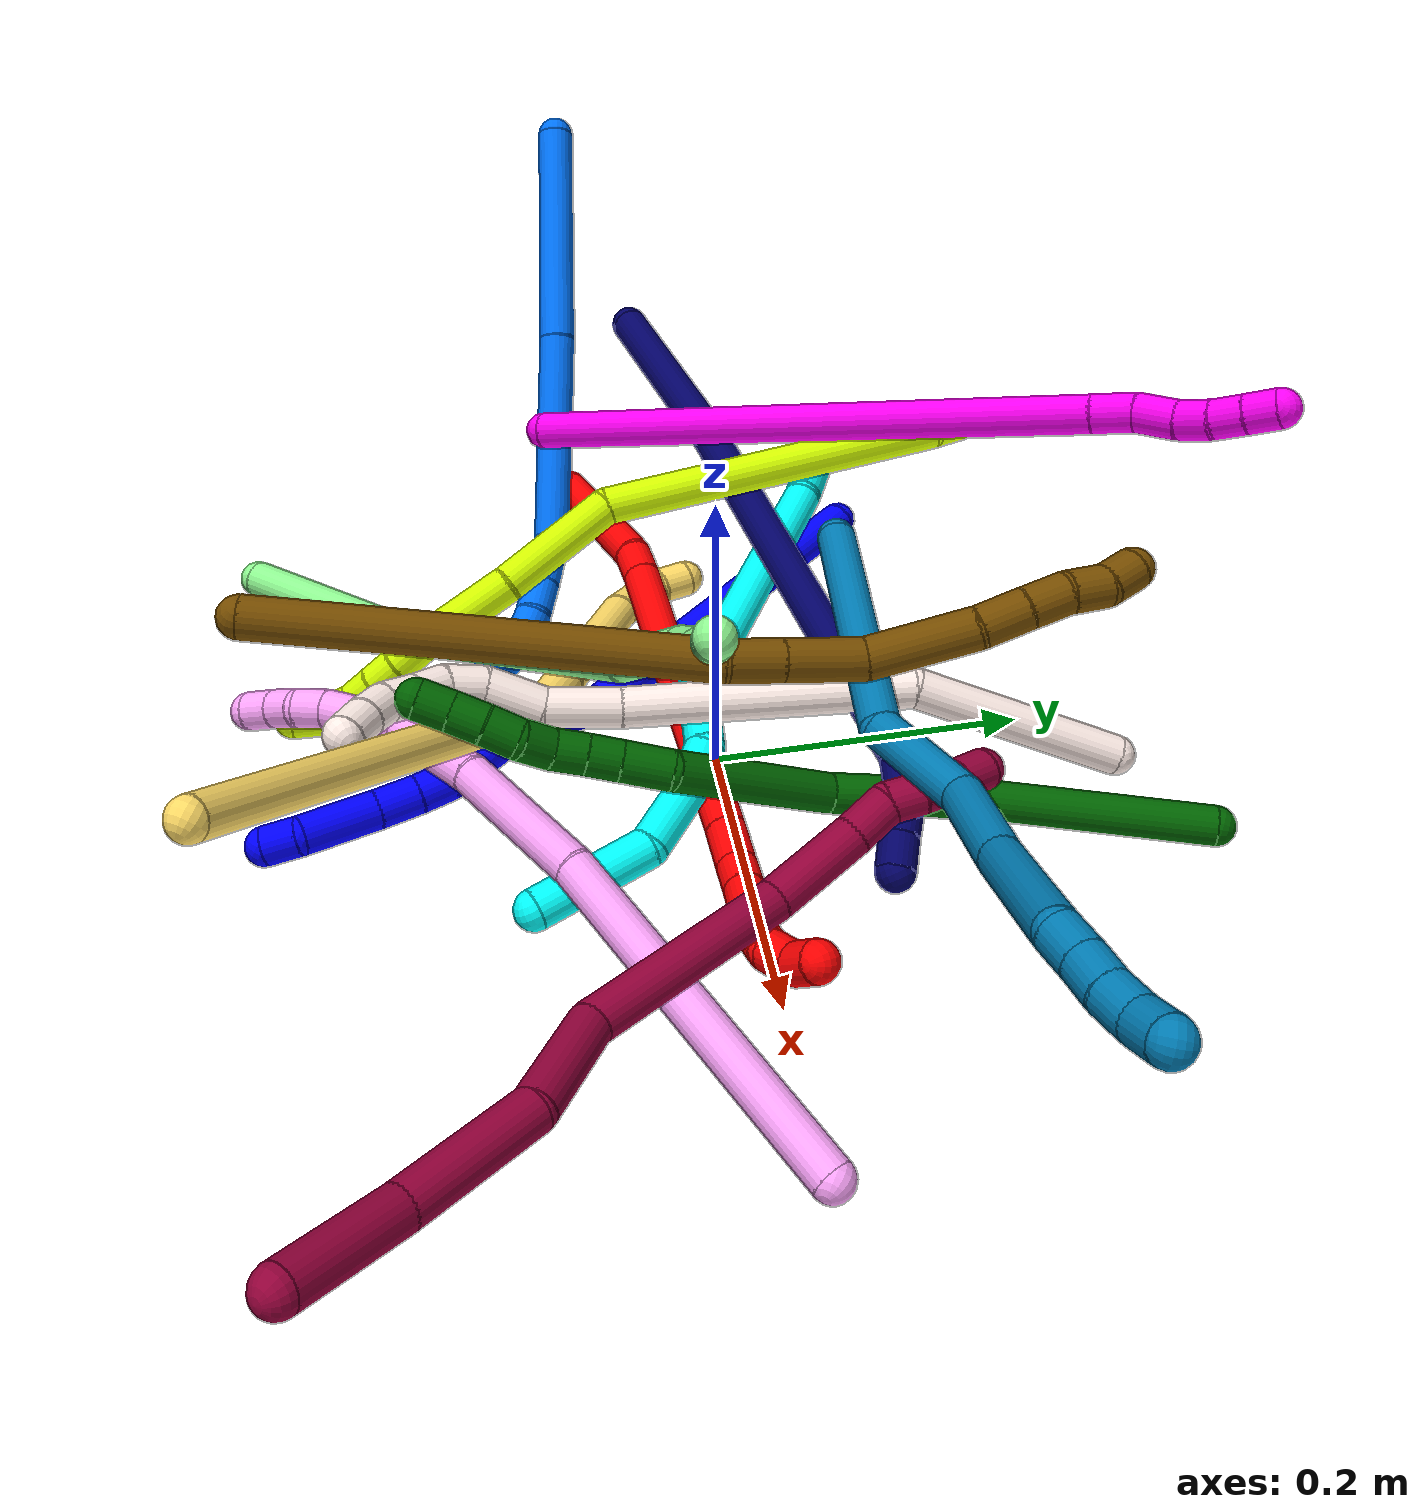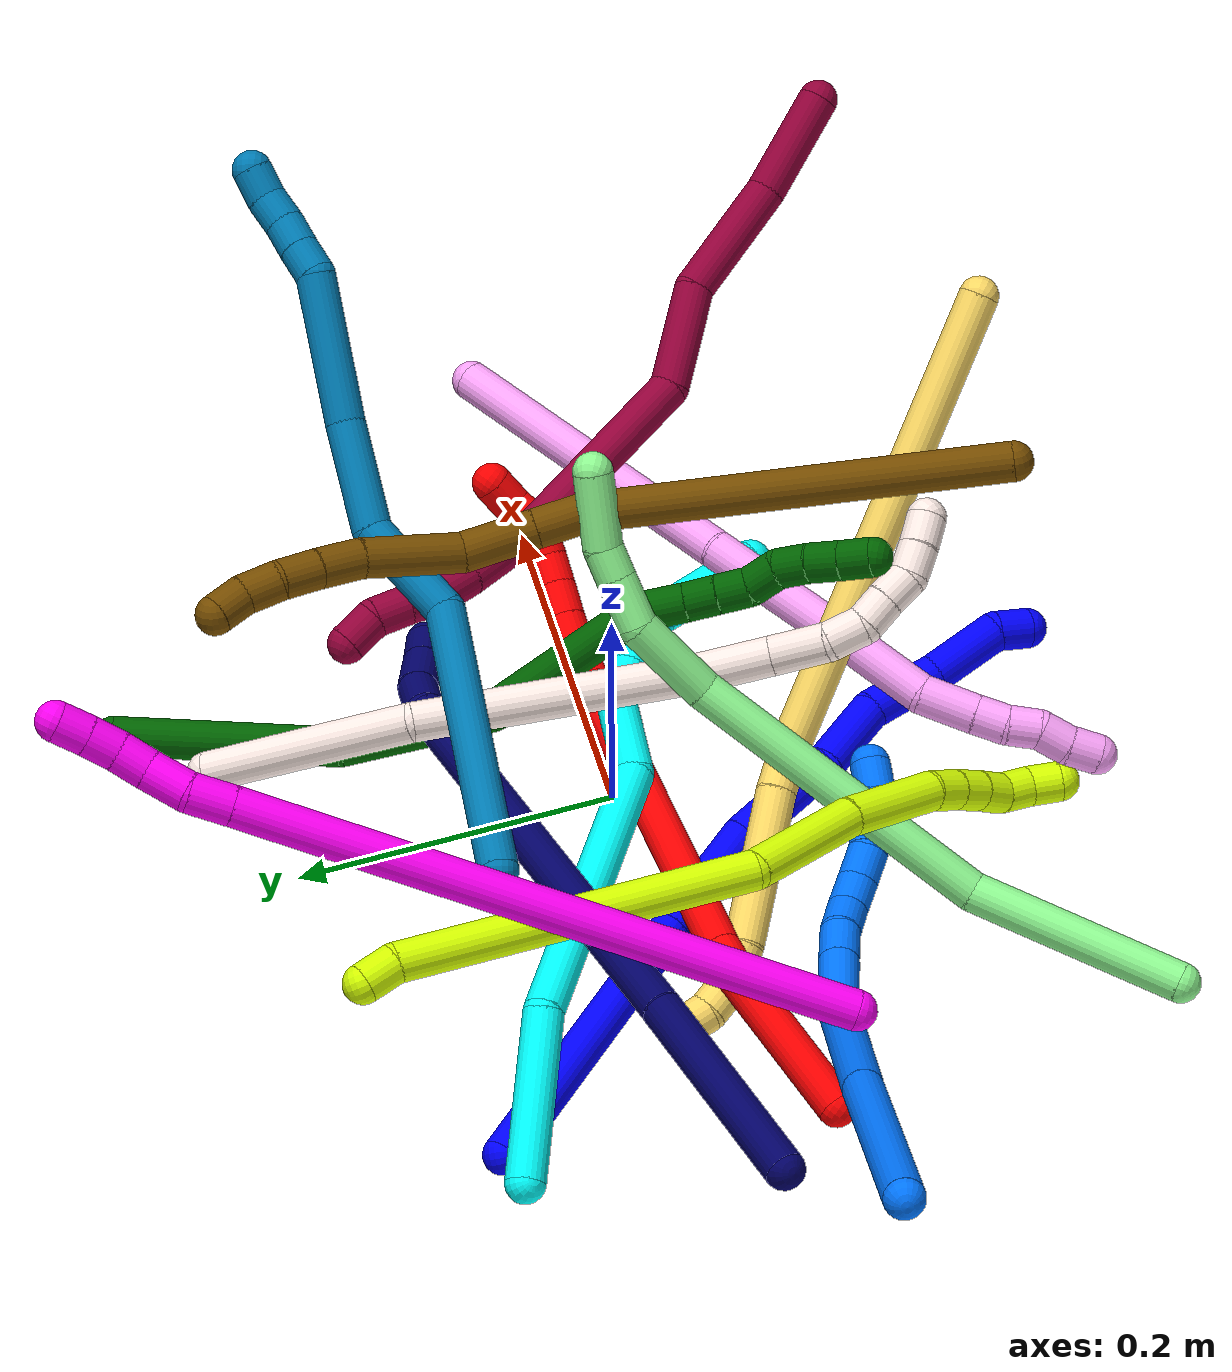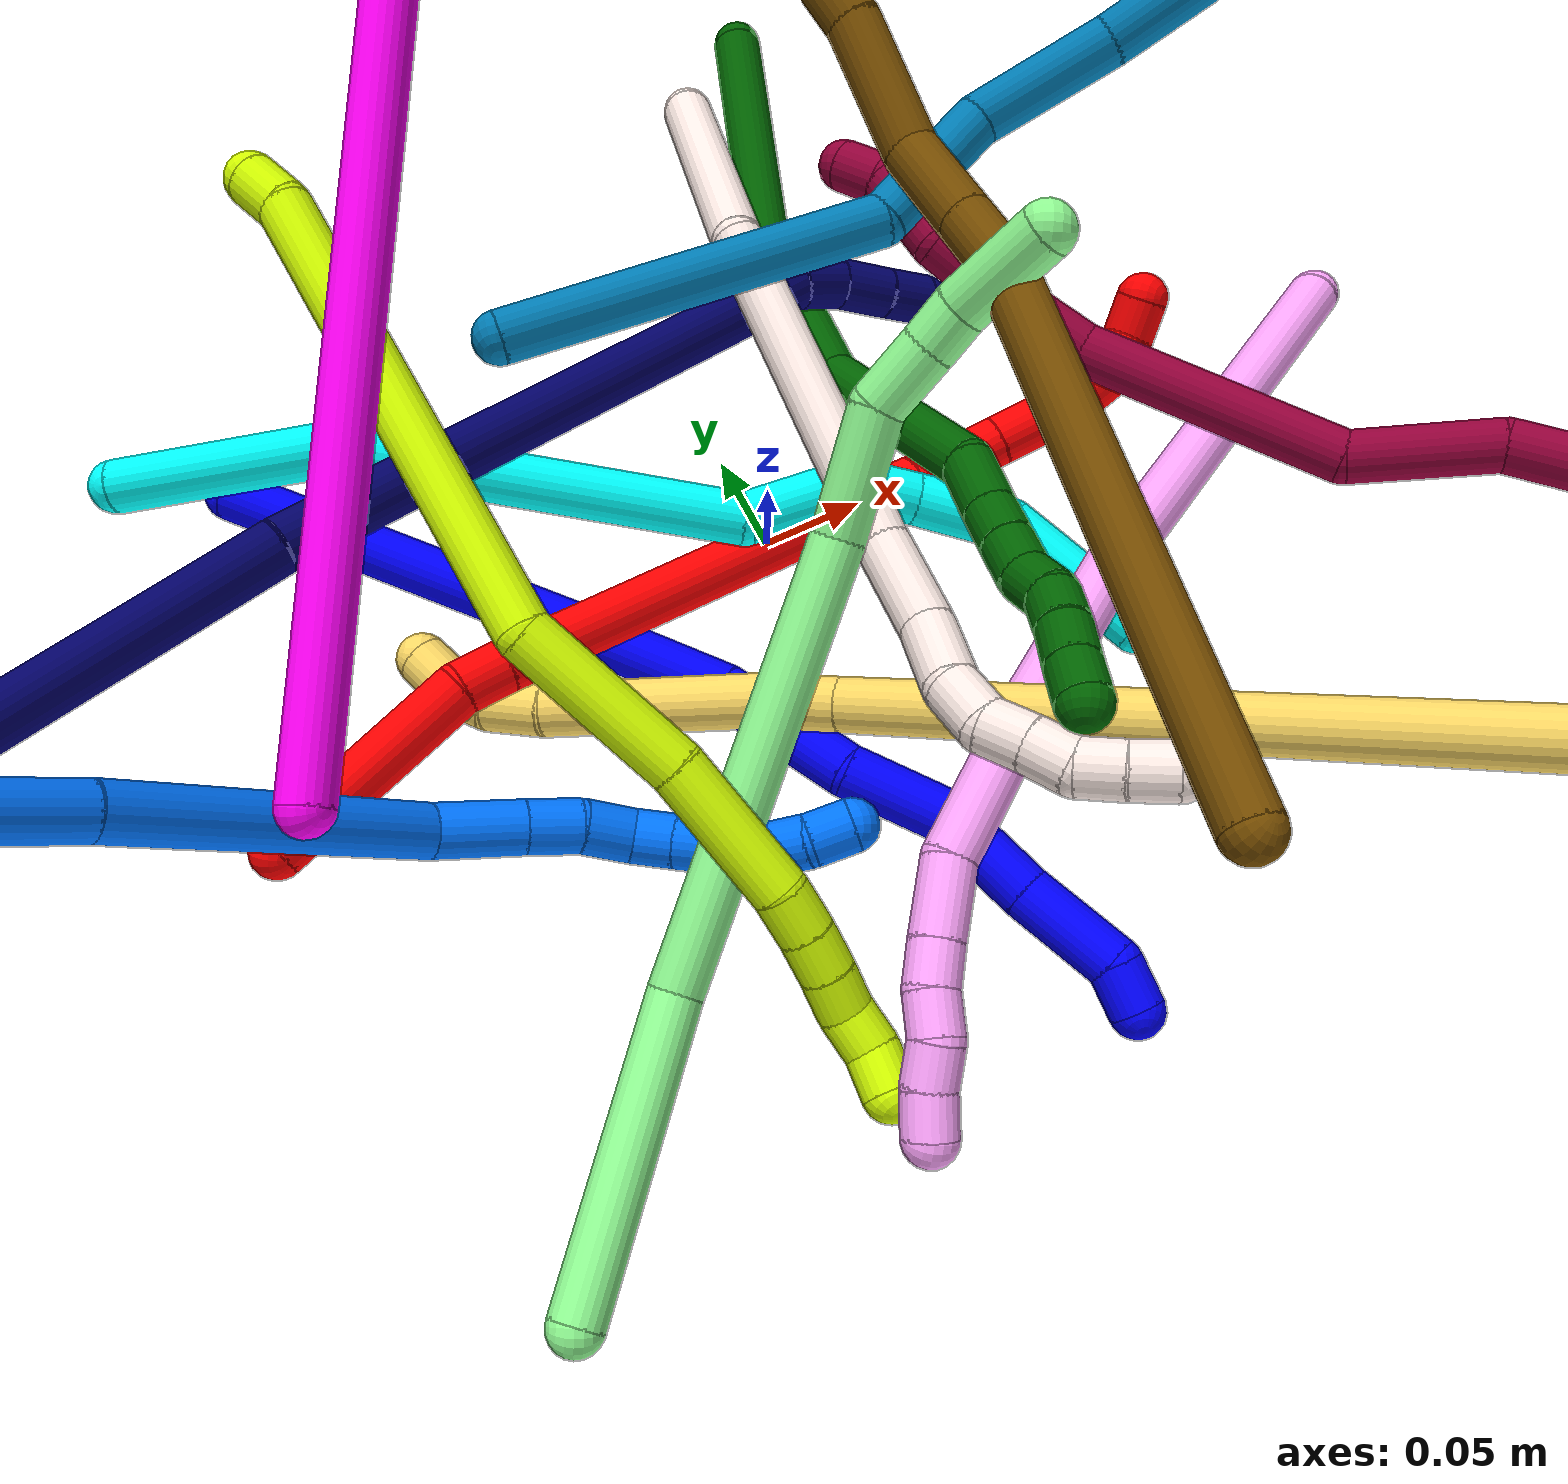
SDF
<sdf version="1.7">
 <world name="default">
  <plugin name="TubeGeneratorPlugin" filename="libtube_generator_plugin.so"/>
  <model name="photoneo_s_sensor">
   <static>1</static>
   <pose>0 0 2 1.57079 1.57079 3.14159</pose>
   <link name="link">
    <inertial><mass>0.1</mass></inertial>
    <sensor name="sensor" type="depth">
     <update_rate>30</update_rate>
     <camera>
      <horizontal_fov>1.22</horizontal_fov>
      <image><width>1920</width><height>1200</height><format>B8G8R8</format></image>
      <clip><near>0.1</near><far>4</far></clip>
      <depth_camera><output>points</output></depth_camera>
     </camera>
     <plugin name="camera_plugin" filename="libgazebo_ros_depth_camera.so">
      <baseline>0.2</baseline>
      <alwaysOn>1</alwaysOn>
      <updateRate>0.0</updateRate>
      <cameraName>camera_ir</cameraName>
      <imageTopicName>/camera/color/image_raw</imageTopicName>
      <cameraInfoTopicName>/camera/color/camera_info</cameraInfoTopicName>
      <depthImageTopicName>/camera/depth/image_raw</depthImageTopicName>
      <depthImageCameraInfoTopicName>/camera/depth/camera_info</depthImageCameraInfoTopicName>
      <pointCloudTopicName>/camera/depth/points</pointCloudTopicName>
      <frameName>fr_optical</frameName>
      <pointCloudCutoff>0.1</pointCloudCutoff>
      <pointCloudCutoffMax>2.0</pointCloudCutoffMax>
      <distortionK1>0</distortionK1>
      <distortionK2>0</distortionK2>
      <distortionK3>0</distortionK3>
      <distortionT1>0</distortionT1>
      <distortionT2>0</distortionT2>
      <CxPrime>0</CxPrime>
      <Cx>0</Cx>
      <Cy>0</Cy>
      <focalLength>0</focalLength>
      <hackBaseline>0</hackBaseline>
     </plugin>
    </sensor>
   </link>
  </model>
  <gravity>0 0 -9.8</gravity>
  <magnetic_field>6e-06 2.3e-05 -4.2e-05</magnetic_field>
  <atmosphere type="adiabatic"/>
  <physics name="default_physics" default="0" type="ode">
   <max_step_size>0.003</max_step_size>
   <real_time_factor>1</real_time_factor>
   <real_time_update_rate>1000</real_time_update_rate>
   <max_contacts>10000</max_contacts>
   <ode>
    <solver>
     <type>quick</type>
     <iters>100</iters>
     <sor>1.3</sor>
     <use_dynamic_moi_rescaling>0</use_dynamic_moi_rescaling>
    </solver>
    <constraints>
     <contact_max_correcting_vel>0</contact_max_correcting_vel>
     <contact_surface_layer>0.001</contact_surface_layer>
     <cfm>0</cfm>
     <erp>0.2</erp>
    </constraints>
   </ode>
  </physics>
  <scene><ambient>0.4 0.4 0.4 1</ambient><background>0.7 0.7 0.7 1</background><shadows>0</shadows></scene>
  <audio><device>default</device></audio>
  <spherical_coordinates>
   <surface_model>EARTH_WGS84</surface_model>
   <latitude_deg>0</latitude_deg>
   <longitude_deg>0</longitude_deg>
   <elevation>0</elevation>
   <heading_deg>0</heading_deg>
  </spherical_coordinates>
  <model name="bin">
   <static>1</static>
   <link name="bottom">
    <collision name="collision-bottom">
     <pose>0 0 -0.01 0 -0 0</pose>
     <geometry><box><size>0.8 0.6 0.02</size></box></geometry>
     <surface>
      <friction><ode><mu>100</mu><mu2>100</mu2></ode></friction>
      <contact><collide_bitmask>65535</collide_bitmask></contact>
     </surface>
    </collision>
   </link>
   <link name="west_wall">
    <collision name="collision-west_wall">
     <pose>-0.41 0 0.1 0 -0 0</pose>
     <geometry><box><size>0.02 0.6 0.2</size></box></geometry>
     <surface>
      <friction><ode><mu>100</mu><mu2>100</mu2></ode></friction>
      <contact><collide_bitmask>65535</collide_bitmask></contact>
     </surface>
    </collision>
   </link>
   <link name="east_wall">
    <collision name="collision-east_wall">
     <pose>0.41 0 0.1 0 -0 0</pose>
     <geometry><box><size>0.02 0.6 0.2</size></box></geometry>
     <surface>
      <friction><ode><mu>100</mu><mu2>100</mu2></ode></friction>
      <contact><collide_bitmask>65535</collide_bitmask></contact>
     </surface>
    </collision>
   </link>
   <link name="south_wall">
    <collision name="collision-south_wall">
     <pose>0 -0.31 0.1 0 -0 0</pose>
     <geometry><box><size>0.8 0.02 0.2</size></box></geometry>
     <surface>
      <friction><ode><mu>100</mu><mu2>100</mu2></ode></friction>
      <contact><collide_bitmask>65535</collide_bitmask></contact>
     </surface>
    </collision>
   </link>
   <link name="north_wall">
    <collision name="collision-north_wall">
     <pose>0 0.31 0.1 0 -0 0</pose>
     <geometry><box><size>0.8 0.02 0.2</size></box></geometry>
     <surface>
      <friction><ode><mu>100</mu><mu2>100</mu2></ode></friction>
      <contact><collide_bitmask>65535</collide_bitmask></contact>
     </surface>
    </collision>
   </link>
  </model>
  <model name="1">
   <static>0</static>
   <link name="1">
    <collision name="collision-cylinder-e_1_1_4">
     <pose>0.06777 -0.046872 0.042314 0.836464 0.820705 0.382005</pose>
     <geometry><cylinder><radius>0.0125</radius><length>0.185259</length></cylinder></geometry>
     <surface>
      <friction><ode><mu>1.16</mu><mu2>1.16</mu2><slip1>0</slip1><slip2>0</slip2></ode></friction>
      <contact><ode><kp>1e+06</kp><kd>1</kd><max_vel>0</max_vel><min_depth>0.001</min_depth></ode></contact>
     </surface>
    </collision>
    <visual name="visual-cylinder-e_1_1_4">
     <pose>0.06777 -0.046872 0.042314 0.836464 0.820705 0.382005</pose>
     <geometry><cylinder><radius>0.0125</radius><length>0.185259</length></cylinder></geometry>
     <material><ambient>0 0 1 1</ambient></material>
    </visual>
    <collision name="collision-cylinder-e_2_4_5">
     <pose>0.163566 -0.113989 0.102749 0.840682 0.800877 0.374003</pose>
     <geometry><cylinder><radius>0.0125</radius><length>0.078068</length></cylinder></geometry>
     <surface>
      <friction><ode><mu>1.16</mu><mu2>1.16</mu2><slip1>0</slip1><slip2>0</slip2></ode></friction>
      <contact><ode><kp>1e+06</kp><kd>1</kd><max_vel>0</max_vel><min_depth>0.001</min_depth></ode></contact>
     </surface>
    </collision>
    <visual name="visual-cylinder-e_2_4_5">
     <pose>0.163566 -0.113989 0.102749 0.840682 0.800877 0.374003</pose>
     <geometry><cylinder><radius>0.0125</radius><length>0.078068</length></cylinder></geometry>
     <material><ambient>0 0 1 1</ambient></material>
    </visual>
    <collision name="collision-cylinder-e_3_5_6">
     <pose>0.21223 -0.149233 0.144991 0.556344 0.628389 0.185071</pose>
     <geometry><cylinder><radius>0.0125</radius><length>0.070221</length></cylinder></geometry>
     <surface>
      <friction><ode><mu>1.16</mu><mu2>1.16</mu2><slip1>0</slip1><slip2>0</slip2></ode></friction>
      <contact><ode><kp>1e+06</kp><kd>1</kd><max_vel>0</max_vel><min_depth>0.001</min_depth></ode></contact>
     </surface>
    </collision>
    <visual name="visual-cylinder-e_3_5_6">
     <pose>0.21223 -0.149233 0.144991 0.556344 0.628389 0.185071</pose>
     <geometry><cylinder><radius>0.0125</radius><length>0.070221</length></cylinder></geometry>
     <material><ambient>0 0 1 1</ambient></material>
    </visual>
    <collision name="collision-cylinder-e_4_6_7">
     <pose>0.249468 -0.177711 0.180366 0.875044 0.757257 0.36796</pose>
     <geometry><cylinder><radius>0.0125</radius><length>0.048325</length></cylinder></geometry>
     <surface>
      <friction><ode><mu>1.16</mu><mu2>1.16</mu2><slip1>0</slip1><slip2>0</slip2></ode></friction>
      <contact><ode><kp>1e+06</kp><kd>1</kd><max_vel>0</max_vel><min_depth>0.001</min_depth></ode></contact>
     </surface>
    </collision>
    <visual name="visual-cylinder-e_4_6_7">
     <pose>0.249468 -0.177711 0.180366 0.875044 0.757257 0.36796</pose>
     <geometry><cylinder><radius>0.0125</radius><length>0.048325</length></cylinder></geometry>
     <material><ambient>0 0 1 1</ambient></material>
    </visual>
    <collision name="collision-cylinder-e_5_7_8">
     <pose>0.270788 -0.197475 0.199018 0.704364 0.45272 0.168875</pose>
     <geometry><cylinder><radius>0.0125</radius><length>0.02159</length></cylinder></geometry>
     <surface>
      <friction><ode><mu>1.16</mu><mu2>1.16</mu2><slip1>0</slip1><slip2>0</slip2></ode></friction>
      <contact><ode><kp>1e+06</kp><kd>1</kd><max_vel>0</max_vel><min_depth>0.001</min_depth></ode></contact>
     </surface>
    </collision>
    <visual name="visual-cylinder-e_5_7_8">
     <pose>0.270788 -0.197475 0.199018 0.704364 0.45272 0.168875</pose>
     <geometry><cylinder><radius>0.0125</radius><length>0.02159</length></cylinder></geometry>
     <material><ambient>0 0 1 1</ambient></material>
    </visual>
    <collision name="collision-cylinder-e_6_8_9">
     <pose>0.281226 -0.21108 0.216055 0.64933 0.441247 0.150684</pose>
     <geometry><cylinder><radius>0.0125</radius><length>0.02677</length></cylinder></geometry>
     <surface>
      <friction><ode><mu>1.16</mu><mu2>1.16</mu2><slip1>0</slip1><slip2>0</slip2></ode></friction>
      <contact><ode><kp>1e+06</kp><kd>1</kd><max_vel>0</max_vel><min_depth>0.001</min_depth></ode></contact>
     </surface>
    </collision>
    <visual name="visual-cylinder-e_6_8_9">
     <pose>0.281226 -0.21108 0.216055 0.64933 0.441247 0.150684</pose>
     <geometry><cylinder><radius>0.0125</radius><length>0.02677</length></cylinder></geometry>
     <material><ambient>0 0 1 1</ambient></material>
    </visual>
    <collision name="collision-cylinder-e_7_9_10">
     <pose>0.299183 -0.229556 0.243227 0.566821 0.532305 0.158469</pose>
     <geometry><cylinder><radius>0.0125</radius><length>0.048237</length></cylinder></geometry>
     <surface>
      <friction><ode><mu>1.16</mu><mu2>1.16</mu2><slip1>0</slip1><slip2>0</slip2></ode></friction>
      <contact><ode><kp>1e+06</kp><kd>1</kd><max_vel>0</max_vel><min_depth>0.001</min_depth></ode></contact>
     </surface>
    </collision>
    <visual name="visual-cylinder-e_7_9_10">
     <pose>0.299183 -0.229556 0.243227 0.566821 0.532305 0.158469</pose>
     <geometry><cylinder><radius>0.0125</radius><length>0.048237</length></cylinder></geometry>
     <material><ambient>0 0 1 1</ambient></material>
    </visual>
    <collision name="collision-cylinder-e_8_10_2">
     <pose>0.312108 -0.247802 0.268832 0.720371 0.063621 0.023968</pose>
     <geometry><cylinder><radius>0.0125</radius><length>0.021529</length></cylinder></geometry>
     <surface>
      <friction><ode><mu>1.16</mu><mu2>1.16</mu2><slip1>0</slip1><slip2>0</slip2></ode></friction>
      <contact><ode><kp>1e+06</kp><kd>1</kd><max_vel>0</max_vel><min_depth>0.001</min_depth></ode></contact>
     </surface>
    </collision>
    <visual name="visual-cylinder-e_8_10_2">
     <pose>0.312108 -0.247802 0.268832 0.720371 0.063621 0.023968</pose>
     <geometry><cylinder><radius>0.0125</radius><length>0.021529</length></cylinder></geometry>
     <material><ambient>0 0 1 1</ambient></material>
    </visual>
    <collision name="collision-sphere-2">
     <pose>0.312792 -0.254888 0.276906 0 -0 0</pose>
     <geometry><sphere><radius>0.0125</radius></sphere></geometry>
     <surface>
      <friction><ode><mu>1.16</mu><mu2>1.16</mu2><slip1>0</slip1><slip2>0</slip2></ode></friction>
      <contact><ode><kp>1e+06</kp><kd>1</kd><max_vel>0</max_vel><min_depth>0.001</min_depth></ode></contact>
     </surface>
    </collision>
    <visual name="visual-sphere-2">
     <pose>0.312792 -0.254888 0.276906 0 -0 0</pose>
     <geometry><sphere><radius>0.0125</radius></sphere></geometry>
     <material><ambient>0 0 1 1</ambient></material>
    </visual>
    <collision name="collision-sphere-10">
     <pose>0.311424 -0.240715 0.260758 0 -0 0</pose>
     <geometry><sphere><radius>0.0125</radius></sphere></geometry>
     <surface>
      <friction><ode><mu>1.16</mu><mu2>1.16</mu2><slip1>0</slip1><slip2>0</slip2></ode></friction>
      <contact><ode><kp>1e+06</kp><kd>1</kd><max_vel>0</max_vel><min_depth>0.001</min_depth></ode></contact>
     </surface>
    </collision>
    <visual name="visual-sphere-10">
     <pose>0.311424 -0.240715 0.260758 0 -0 0</pose>
     <geometry><sphere><radius>0.0125</radius></sphere></geometry>
     <material><ambient>0 0 1 1</ambient></material>
    </visual>
    <collision name="collision-sphere-9">
     <pose>0.286942 -0.218398 0.225695 0 -0 0</pose>
     <geometry><sphere><radius>0.0125</radius></sphere></geometry>
     <surface>
      <friction><ode><mu>1.16</mu><mu2>1.16</mu2><slip1>0</slip1><slip2>0</slip2></ode></friction>
      <contact><ode><kp>1e+06</kp><kd>1</kd><max_vel>0</max_vel><min_depth>0.001</min_depth></ode></contact>
     </surface>
    </collision>
    <visual name="visual-sphere-9">
     <pose>0.286942 -0.218398 0.225695 0 -0 0</pose>
     <geometry><sphere><radius>0.0125</radius></sphere></geometry>
     <material><ambient>0 0 1 1</ambient></material>
    </visual>
    <collision name="collision-sphere-4">
     <pose>0.13554 -0.093744 0.084627 0 -0 0</pose>
     <geometry><sphere><radius>0.0125</radius></sphere></geometry>
     <surface>
      <friction><ode><mu>1.16</mu><mu2>1.16</mu2><slip1>0</slip1><slip2>0</slip2></ode></friction>
      <contact><ode><kp>1e+06</kp><kd>1</kd><max_vel>0</max_vel><min_depth>0.001</min_depth></ode></contact>
     </surface>
    </collision>
    <visual name="visual-sphere-4">
     <pose>0.13554 -0.093744 0.084627 0 -0 0</pose>
     <geometry><sphere><radius>0.0125</radius></sphere></geometry>
     <material><ambient>0 0 1 1</ambient></material>
    </visual>
    <collision name="collision-sphere-1">
     <geometry><sphere><radius>0.0125</radius></sphere></geometry>
     <surface>
      <friction><ode><mu>1.16</mu><mu2>1.16</mu2><slip1>0</slip1><slip2>0</slip2></ode></friction>
      <contact><ode><kp>1e+06</kp><kd>1</kd><max_vel>0</max_vel><min_depth>0.001</min_depth></ode></contact>
     </surface>
    </collision>
    <visual name="visual-sphere-1">
     <geometry><sphere><radius>0.0125</radius></sphere></geometry>
     <material><ambient>0 0 1 1</ambient></material>
    </visual>
    <collision name="collision-sphere-8">
     <pose>0.27551 -0.203761 0.206416 0 -0 0</pose>
     <geometry><sphere><radius>0.0125</radius></sphere></geometry>
     <surface>
      <friction><ode><mu>1.16</mu><mu2>1.16</mu2><slip1>0</slip1><slip2>0</slip2></ode></friction>
      <contact><ode><kp>1e+06</kp><kd>1</kd><max_vel>0</max_vel><min_depth>0.001</min_depth></ode></contact>
     </surface>
    </collision>
    <visual name="visual-sphere-8">
     <pose>0.27551 -0.203761 0.206416 0 -0 0</pose>
     <geometry><sphere><radius>0.0125</radius></sphere></geometry>
     <material><ambient>0 0 1 1</ambient></material>
    </visual>
    <collision name="collision-sphere-5">
     <pose>0.191591 -0.134234 0.120871 0 -0 0</pose>
     <geometry><sphere><radius>0.0125</radius></sphere></geometry>
     <surface>
      <friction><ode><mu>1.16</mu><mu2>1.16</mu2><slip1>0</slip1><slip2>0</slip2></ode></friction>
      <contact><ode><kp>1e+06</kp><kd>1</kd><max_vel>0</max_vel><min_depth>0.001</min_depth></ode></contact>
     </surface>
    </collision>
    <visual name="visual-sphere-5">
     <pose>0.191591 -0.134234 0.120871 0 -0 0</pose>
     <geometry><sphere><radius>0.0125</radius></sphere></geometry>
     <material><ambient>0 0 1 1</ambient></material>
    </visual>
    <collision name="collision-sphere-6">
     <pose>0.23287 -0.164233 0.169111 0 -0 0</pose>
     <geometry><sphere><radius>0.0125</radius></sphere></geometry>
     <surface>
      <friction><ode><mu>1.16</mu><mu2>1.16</mu2><slip1>0</slip1><slip2>0</slip2></ode></friction>
      <contact><ode><kp>1e+06</kp><kd>1</kd><max_vel>0</max_vel><min_depth>0.001</min_depth></ode></contact>
     </surface>
    </collision>
    <visual name="visual-sphere-6">
     <pose>0.23287 -0.164233 0.169111 0 -0 0</pose>
     <geometry><sphere><radius>0.0125</radius></sphere></geometry>
     <material><ambient>0 0 1 1</ambient></material>
    </visual>
    <collision name="collision-sphere-7">
     <pose>0.266066 -0.191189 0.191621 0 -0 0</pose>
     <geometry><sphere><radius>0.0125</radius></sphere></geometry>
     <surface>
      <friction><ode><mu>1.16</mu><mu2>1.16</mu2><slip1>0</slip1><slip2>0</slip2></ode></friction>
      <contact><ode><kp>1e+06</kp><kd>1</kd><max_vel>0</max_vel><min_depth>0.001</min_depth></ode></contact>
     </surface>
    </collision>
    <visual name="visual-sphere-7">
     <pose>0.266066 -0.191189 0.191621 0 -0 0</pose>
     <geometry><sphere><radius>0.0125</radius></sphere></geometry>
     <material><ambient>0 0 1 1</ambient></material>
    </visual>
    <inertial>
     <pose>0.173618 -0.125944 0.124718 0 -0 0</pose>
     <mass>0.5</mass>
     <inertia>
      <ixx>0.000597</ixx>
      <ixy>0</ixy>
      <ixz>0</ixz>
      <iyy>0.000667</iyy>
      <iyz>0</iyz>
      <izz>-0.000114</izz>
     </inertia>
    </inertial>
   </link>
   <pose>-0.224468 0.135228 0.011497 1.12927 -0.348916 -0.186712</pose>
  </model>
  <model name="2">
   <static>0</static>
   <link name="2">
    <collision name="collision-cylinder-e_1_1_4">
     <pose>0.049592 0.006685 0.013835 -0.450108 1.27034 -0.334324</pose>
     <geometry><cylinder><radius>0.0125</radius><length>0.103836</length></cylinder></geometry>
     <surface>
      <friction><ode><mu>1.16</mu><mu2>1.16</mu2><slip1>0</slip1><slip2>0</slip2></ode></friction>
      <contact><ode><kp>1e+06</kp><kd>1</kd><max_vel>0</max_vel><min_depth>0.001</min_depth></ode></contact>
     </surface>
    </collision>
    <visual name="visual-cylinder-e_1_1_4">
     <pose>0.049592 0.006685 0.013835 -0.450108 1.27034 -0.334324</pose>
     <geometry><cylinder><radius>0.0125</radius><length>0.103836</length></cylinder></geometry>
     <material><ambient>1 0 0 1</ambient></material>
    </visual>
    <collision name="collision-cylinder-e_2_4_5">
     <pose>0.109808 0.011772 0.031379 0.406887 1.20754 0.282663</pose>
     <geometry><cylinder><radius>0.0125</radius><length>0.022731</length></cylinder></geometry>
     <surface>
      <friction><ode><mu>1.16</mu><mu2>1.16</mu2><slip1>0</slip1><slip2>0</slip2></ode></friction>
      <contact><ode><kp>1e+06</kp><kd>1</kd><max_vel>0</max_vel><min_depth>0.001</min_depth></ode></contact>
     </surface>
    </collision>
    <visual name="visual-cylinder-e_2_4_5">
     <pose>0.109808 0.011772 0.031379 0.406887 1.20754 0.282663</pose>
     <geometry><cylinder><radius>0.0125</radius><length>0.022731</length></cylinder></geometry>
     <material><ambient>1 0 0 1</ambient></material>
    </visual>
    <collision name="collision-cylinder-e_3_5_6">
     <pose>0.221184 -0.007371 0.076052 0.404663 1.15436 0.265578</pose>
     <geometry><cylinder><radius>0.0125</radius><length>0.220335</length></cylinder></geometry>
     <surface>
      <friction><ode><mu>1.16</mu><mu2>1.16</mu2><slip1>0</slip1><slip2>0</slip2></ode></friction>
      <contact><ode><kp>1e+06</kp><kd>1</kd><max_vel>0</max_vel><min_depth>0.001</min_depth></ode></contact>
     </surface>
    </collision>
    <visual name="visual-cylinder-e_3_5_6">
     <pose>0.221184 -0.007371 0.076052 0.404663 1.15436 0.265578</pose>
     <geometry><cylinder><radius>0.0125</radius><length>0.220335</length></cylinder></geometry>
     <material><ambient>1 0 0 1</ambient></material>
    </visual>
    <collision name="collision-cylinder-e_4_6_7">
     <pose>0.334475 -0.027264 0.122438 0.408611 1.13043 0.261327</pose>
     <geometry><cylinder><radius>0.0125</radius><length>0.027722</length></cylinder></geometry>
     <surface>
      <friction><ode><mu>1.16</mu><mu2>1.16</mu2><slip1>0</slip1><slip2>0</slip2></ode></friction>
      <contact><ode><kp>1e+06</kp><kd>1</kd><max_vel>0</max_vel><min_depth>0.001</min_depth></ode></contact>
     </surface>
    </collision>
    <visual name="visual-cylinder-e_4_6_7">
     <pose>0.334475 -0.027264 0.122438 0.408611 1.13043 0.261327</pose>
     <geometry><cylinder><radius>0.0125</radius><length>0.027722</length></cylinder></geometry>
     <material><ambient>1 0 0 1</ambient></material>
    </visual>
    <collision name="collision-cylinder-e_5_7_8">
     <pose>0.356221 -0.029176 0.133825 -0.072885 0.994712 -0.03958</pose>
     <geometry><cylinder><radius>0.0125</radius><length>0.021959</length></cylinder></geometry>
     <surface>
      <friction><ode><mu>1.16</mu><mu2>1.16</mu2><slip1>0</slip1><slip2>0</slip2></ode></friction>
      <contact><ode><kp>1e+06</kp><kd>1</kd><max_vel>0</max_vel><min_depth>0.001</min_depth></ode></contact>
     </surface>
    </collision>
    <visual name="visual-cylinder-e_5_7_8">
     <pose>0.356221 -0.029176 0.133825 -0.072885 0.994712 -0.03958</pose>
     <geometry><cylinder><radius>0.0125</radius><length>0.021959</length></cylinder></geometry>
     <material><ambient>1 0 0 1</ambient></material>
    </visual>
    <collision name="collision-cylinder-e_6_8_9">
     <pose>0.37452 -0.028315 0.146102 -0.067358 0.962903 -0.035201</pose>
     <geometry><cylinder><radius>0.0125</radius><length>0.022152</length></cylinder></geometry>
     <surface>
      <friction><ode><mu>1.16</mu><mu2>1.16</mu2><slip1>0</slip1><slip2>0</slip2></ode></friction>
      <contact><ode><kp>1e+06</kp><kd>1</kd><max_vel>0</max_vel><min_depth>0.001</min_depth></ode></contact>
     </surface>
    </collision>
    <visual name="visual-cylinder-e_6_8_9">
     <pose>0.37452 -0.028315 0.146102 -0.067358 0.962903 -0.035201</pose>
     <geometry><cylinder><radius>0.0125</radius><length>0.022152</length></cylinder></geometry>
     <material><ambient>1 0 0 1</ambient></material>
    </visual>
    <collision name="collision-cylinder-e_7_9_10">
     <pose>0.391886 -0.026925 0.158269 -0.163055 0.948623 -0.08385</pose>
     <geometry><cylinder><radius>0.0125</radius><length>0.020364</length></cylinder></geometry>
     <surface>
      <friction><ode><mu>1.16</mu><mu2>1.16</mu2><slip1>0</slip1><slip2>0</slip2></ode></friction>
      <contact><ode><kp>1e+06</kp><kd>1</kd><max_vel>0</max_vel><min_depth>0.001</min_depth></ode></contact>
     </surface>
    </collision>
    <visual name="visual-cylinder-e_7_9_10">
     <pose>0.391886 -0.026925 0.158269 -0.163055 0.948623 -0.08385</pose>
     <geometry><cylinder><radius>0.0125</radius><length>0.020364</length></cylinder></geometry>
     <material><ambient>1 0 0 1</ambient></material>
    </visual>
    <collision name="collision-cylinder-e_8_10_11">
     <pose>0.407713 -0.022249 0.170095 -0.556411 0.821153 -0.247394</pose>
     <geometry><cylinder><radius>0.0125</radius><length>0.020639</length></cylinder></geometry>
     <surface>
      <friction><ode><mu>1.16</mu><mu2>1.16</mu2><slip1>0</slip1><slip2>0</slip2></ode></friction>
      <contact><ode><kp>1e+06</kp><kd>1</kd><max_vel>0</max_vel><min_depth>0.001</min_depth></ode></contact>
     </surface>
    </collision>
    <visual name="visual-cylinder-e_8_10_11">
     <pose>0.407713 -0.022249 0.170095 -0.556411 0.821153 -0.247394</pose>
     <geometry><cylinder><radius>0.0125</radius><length>0.020639</length></cylinder></geometry>
     <material><ambient>1 0 0 1</ambient></material>
    </visual>
    <collision name="collision-cylinder-e_9_11_12">
     <pose>0.42435 -0.014459 0.177455 -1.24221 1.12812 -0.850175</pose>
     <geometry><cylinder><radius>0.0125</radius><length>0.020107</length></cylinder></geometry>
     <surface>
      <friction><ode><mu>1.16</mu><mu2>1.16</mu2><slip1>0</slip1><slip2>0</slip2></ode></friction>
      <contact><ode><kp>1e+06</kp><kd>1</kd><max_vel>0</max_vel><min_depth>0.001</min_depth></ode></contact>
     </surface>
    </collision>
    <visual name="visual-cylinder-e_9_11_12">
     <pose>0.42435 -0.014459 0.177455 -1.24221 1.12812 -0.850175</pose>
     <geometry><cylinder><radius>0.0125</radius><length>0.020107</length></cylinder></geometry>
     <material><ambient>1 0 0 1</ambient></material>
    </visual>
    <collision name="collision-cylinder-e_10_12_2">
     <pose>0.439572 -0.002682 0.180987 -1.29945 0.65482 -0.505069</pose>
     <geometry><cylinder><radius>0.0125</radius><length>0.020156</length></cylinder></geometry>
     <surface>
      <friction><ode><mu>1.16</mu><mu2>1.16</mu2><slip1>0</slip1><slip2>0</slip2></ode></friction>
      <contact><ode><kp>1e+06</kp><kd>1</kd><max_vel>0</max_vel><min_depth>0.001</min_depth></ode></contact>
     </surface>
    </collision>
    <visual name="visual-cylinder-e_10_12_2">
     <pose>0.439572 -0.002682 0.180987 -1.29945 0.65482 -0.505069</pose>
     <geometry><cylinder><radius>0.0125</radius><length>0.020156</length></cylinder></geometry>
     <material><ambient>1 0 0 1</ambient></material>
    </visual>
    <collision name="collision-sphere-2">
     <pose>0.44571 0.005019 0.18313 0 -0 0</pose>
     <geometry><sphere><radius>0.0125</radius></sphere></geometry>
     <surface>
      <friction><ode><mu>1.16</mu><mu2>1.16</mu2><slip1>0</slip1><slip2>0</slip2></ode></friction>
      <contact><ode><kp>1e+06</kp><kd>1</kd><max_vel>0</max_vel><min_depth>0.001</min_depth></ode></contact>
     </surface>
    </collision>
    <visual name="visual-sphere-2">
     <pose>0.44571 0.005019 0.18313 0 -0 0</pose>
     <geometry><sphere><radius>0.0125</radius></sphere></geometry>
     <material><ambient>1 0 0 1</ambient></material>
    </visual>
    <collision name="collision-sphere-12">
     <pose>0.433435 -0.010383 0.178845 0 -0 0</pose>
     <geometry><sphere><radius>0.0125</radius></sphere></geometry>
     <surface>
      <friction><ode><mu>1.16</mu><mu2>1.16</mu2><slip1>0</slip1><slip2>0</slip2></ode></friction>
      <contact><ode><kp>1e+06</kp><kd>1</kd><max_vel>0</max_vel><min_depth>0.001</min_depth></ode></contact>
     </surface>
    </collision>
    <visual name="visual-sphere-12">
     <pose>0.433435 -0.010383 0.178845 0 -0 0</pose>
     <geometry><sphere><radius>0.0125</radius></sphere></geometry>
     <material><ambient>1 0 0 1</ambient></material>
    </visual>
    <collision name="collision-sphere-11">
     <pose>0.415266 -0.018535 0.176065 0 -0 0</pose>
     <geometry><sphere><radius>0.0125</radius></sphere></geometry>
     <surface>
      <friction><ode><mu>1.16</mu><mu2>1.16</mu2><slip1>0</slip1><slip2>0</slip2></ode></friction>
      <contact><ode><kp>1e+06</kp><kd>1</kd><max_vel>0</max_vel><min_depth>0.001</min_depth></ode></contact>
     </surface>
    </collision>
    <visual name="visual-sphere-11">
     <pose>0.415266 -0.018535 0.176065 0 -0 0</pose>
     <geometry><sphere><radius>0.0125</radius></sphere></geometry>
     <material><ambient>1 0 0 1</ambient></material>
    </visual>
    <collision name="collision-sphere-10">
     <pose>0.40016 -0.025962 0.164124 0 -0 0</pose>
     <geometry><sphere><radius>0.0125</radius></sphere></geometry>
     <surface>
      <friction><ode><mu>1.16</mu><mu2>1.16</mu2><slip1>0</slip1><slip2>0</slip2></ode></friction>
      <contact><ode><kp>1e+06</kp><kd>1</kd><max_vel>0</max_vel><min_depth>0.001</min_depth></ode></contact>
     </surface>
    </collision>
    <visual name="visual-sphere-10">
     <pose>0.40016 -0.025962 0.164124 0 -0 0</pose>
     <geometry><sphere><radius>0.0125</radius></sphere></geometry>
     <material><ambient>1 0 0 1</ambient></material>
    </visual>
    <collision name="collision-sphere-9">
     <pose>0.383612 -0.027889 0.152413 0 -0 0</pose>
     <geometry><sphere><radius>0.0125</radius></sphere></geometry>
     <surface>
      <friction><ode><mu>1.16</mu><mu2>1.16</mu2><slip1>0</slip1><slip2>0</slip2></ode></friction>
      <contact><ode><kp>1e+06</kp><kd>1</kd><max_vel>0</max_vel><min_depth>0.001</min_depth></ode></contact>
     </surface>
    </collision>
    <visual name="visual-sphere-9">
     <pose>0.383612 -0.027889 0.152413 0 -0 0</pose>
     <geometry><sphere><radius>0.0125</radius></sphere></geometry>
     <material><ambient>1 0 0 1</ambient></material>
    </visual>
    <collision name="collision-sphere-4">
     <pose>0.099185 0.01337 0.027671 0 -0 0</pose>
     <geometry><sphere><radius>0.0125</radius></sphere></geometry>
     <surface>
      <friction><ode><mu>1.16</mu><mu2>1.16</mu2><slip1>0</slip1><slip2>0</slip2></ode></friction>
      <contact><ode><kp>1e+06</kp><kd>1</kd><max_vel>0</max_vel><min_depth>0.001</min_depth></ode></contact>
     </surface>
    </collision>
    <visual name="visual-sphere-4">
     <pose>0.099185 0.01337 0.027671 0 -0 0</pose>
     <geometry><sphere><radius>0.0125</radius></sphere></geometry>
     <material><ambient>1 0 0 1</ambient></material>
    </visual>
    <collision name="collision-sphere-1">
     <geometry><sphere><radius>0.0125</radius></sphere></geometry>
     <surface>
      <friction><ode><mu>1.16</mu><mu2>1.16</mu2><slip1>0</slip1><slip2>0</slip2></ode></friction>
      <contact><ode><kp>1e+06</kp><kd>1</kd><max_vel>0</max_vel><min_depth>0.001</min_depth></ode></contact>
     </surface>
    </collision>
    <visual name="visual-sphere-1">
     <geometry><sphere><radius>0.0125</radius></sphere></geometry>
     <material><ambient>1 0 0 1</ambient></material>
    </visual>
    <collision name="collision-sphere-8">
     <pose>0.365429 -0.02874 0.139791 0 -0 0</pose>
     <geometry><sphere><radius>0.0125</radius></sphere></geometry>
     <surface>
      <friction><ode><mu>1.16</mu><mu2>1.16</mu2><slip1>0</slip1><slip2>0</slip2></ode></friction>
      <contact><ode><kp>1e+06</kp><kd>1</kd><max_vel>0</max_vel><min_depth>0.001</min_depth></ode></contact>
     </surface>
    </collision>
    <visual name="visual-sphere-8">
     <pose>0.365429 -0.02874 0.139791 0 -0 0</pose>
     <geometry><sphere><radius>0.0125</radius></sphere></geometry>
     <material><ambient>1 0 0 1</ambient></material>
    </visual>
    <collision name="collision-sphere-5">
     <pose>0.120432 0.010174 0.035088 0 -0 0</pose>
     <geometry><sphere><radius>0.0125</radius></sphere></geometry>
     <surface>
      <friction><ode><mu>1.16</mu><mu2>1.16</mu2><slip1>0</slip1><slip2>0</slip2></ode></friction>
      <contact><ode><kp>1e+06</kp><kd>1</kd><max_vel>0</max_vel><min_depth>0.001</min_depth></ode></contact>
     </surface>
    </collision>
    <visual name="visual-sphere-5">
     <pose>0.120432 0.010174 0.035088 0 -0 0</pose>
     <geometry><sphere><radius>0.0125</radius></sphere></geometry>
     <material><ambient>1 0 0 1</ambient></material>
    </visual>
    <collision name="collision-sphere-6">
     <pose>0.321936 -0.024916 0.117016 0 -0 0</pose>
     <geometry><sphere><radius>0.0125</radius></sphere></geometry>
     <surface>
      <friction><ode><mu>1.16</mu><mu2>1.16</mu2><slip1>0</slip1><slip2>0</slip2></ode></friction>
      <contact><ode><kp>1e+06</kp><kd>1</kd><max_vel>0</max_vel><min_depth>0.001</min_depth></ode></contact>
     </surface>
    </collision>
    <visual name="visual-sphere-6">
     <pose>0.321936 -0.024916 0.117016 0 -0 0</pose>
     <geometry><sphere><radius>0.0125</radius></sphere></geometry>
     <material><ambient>1 0 0 1</ambient></material>
    </visual>
    <collision name="collision-sphere-7">
     <pose>0.347014 -0.029611 0.12786 0 -0 0</pose>
     <geometry><sphere><radius>0.0125</radius></sphere></geometry>
     <surface>
      <friction><ode><mu>1.16</mu><mu2>1.16</mu2><slip1>0</slip1><slip2>0</slip2></ode></friction>
      <contact><ode><kp>1e+06</kp><kd>1</kd><max_vel>0</max_vel><min_depth>0.001</min_depth></ode></contact>
     </surface>
    </collision>
    <visual name="visual-sphere-7">
     <pose>0.347014 -0.029611 0.12786 0 -0 0</pose>
     <geometry><sphere><radius>0.0125</radius></sphere></geometry>
     <material><ambient>1 0 0 1</ambient></material>
    </visual>
    <inertial>
     <pose>0.231116 -0.008077 0.084851 0 -0 0</pose>
     <mass>0.5</mass>
     <inertia>
      <ixx>0.000506</ixx>
      <ixy>0</ixy>
      <ixz>0</ixz>
      <iyy>0.001078</iyy>
      <iyz>0</iyz>
      <izz>-0.000785</izz>
     </inertia>
    </inertial>
   </link>
   <pose>-0.264425 -0.059591 0.038319 1.08877 0.171475 0.493834</pose>
  </model>
  <model name="3">
   <static>0</static>
   <link name="3">
    <collision name="collision-cylinder-e_1_1_4">
     <pose>0.050292 -0.016679 -0.002165 1.69991 1.24806 1.37308</pose>
     <geometry><cylinder><radius>0.0125</radius><length>0.106059</length></cylinder></geometry>
     <surface>
      <friction><ode><mu>1.16</mu><mu2>1.16</mu2><slip1>0</slip1><slip2>0</slip2></ode></friction>
      <contact><ode><kp>1e+06</kp><kd>1</kd><max_vel>0</max_vel><min_depth>0.001</min_depth></ode></contact>
     </surface>
    </collision>
    <visual name="visual-cylinder-e_1_1_4">
     <pose>0.050292 -0.016679 -0.002165 1.69991 1.24806 1.37308</pose>
     <geometry><cylinder><radius>0.0125</radius><length>0.106059</length></cylinder></geometry>
     <material><ambient>0.003922 1 0.996078 1</ambient></material>
    </visual>
    <collision name="collision-cylinder-e_2_4_5">
     <pose>0.173352 -0.088854 -0.025682 1.93808 0.885702 1.20882</pose>
     <geometry><cylinder><radius>0.0125</radius><length>0.187946</length></cylinder></geometry>
     <surface>
      <friction><ode><mu>1.16</mu><mu2>1.16</mu2><slip1>0</slip1><slip2>0</slip2></ode></friction>
      <contact><ode><kp>1e+06</kp><kd>1</kd><max_vel>0</max_vel><min_depth>0.001</min_depth></ode></contact>
     </surface>
    </collision>
    <visual name="visual-cylinder-e_2_4_5">
     <pose>0.173352 -0.088854 -0.025682 1.93808 0.885702 1.20882</pose>
     <geometry><cylinder><radius>0.0125</radius><length>0.187946</length></cylinder></geometry>
     <material><ambient>0.003922 1 0.996078 1</ambient></material>
    </visual>
    <collision name="collision-cylinder-e_3_5_6">
     <pose>0.270776 -0.14806 -0.057041 2.7865 1.16225 2.60819</pose>
     <geometry><cylinder><radius>0.0125</radius><length>0.053731</length></cylinder></geometry>
     <surface>
      <friction><ode><mu>1.16</mu><mu2>1.16</mu2><slip1>0</slip1><slip2>0</slip2></ode></friction>
      <contact><ode><kp>1e+06</kp><kd>1</kd><max_vel>0</max_vel><min_depth>0.001</min_depth></ode></contact>
     </surface>
    </collision>
    <visual name="visual-cylinder-e_3_5_6">
     <pose>0.270776 -0.14806 -0.057041 2.7865 1.16225 2.60819</pose>
     <geometry><cylinder><radius>0.0125</radius><length>0.053731</length></cylinder></geometry>
     <material><ambient>0.003922 1 0.996078 1</ambient></material>
    </visual>
    <collision name="collision-cylinder-e_4_6_7">
     <pose>0.30627 -0.161033 -0.07269 2.11793 0.785118 1.27033</pose>
     <geometry><cylinder><radius>0.0125</radius><length>0.030669</length></cylinder></geometry>
     <surface>
      <friction><ode><mu>1.16</mu><mu2>1.16</mu2><slip1>0</slip1><slip2>0</slip2></ode></friction>
      <contact><ode><kp>1e+06</kp><kd>1</kd><max_vel>0</max_vel><min_depth>0.001</min_depth></ode></contact>
     </surface>
    </collision>
    <visual name="visual-cylinder-e_4_6_7">
     <pose>0.30627 -0.161033 -0.07269 2.11793 0.785118 1.27033</pose>
     <geometry><cylinder><radius>0.0125</radius><length>0.030669</length></cylinder></geometry>
     <material><ambient>0.003922 1 0.996078 1</ambient></material>
    </visual>
    <collision name="collision-cylinder-e_5_7_8">
     <pose>0.333764 -0.185638 -0.082458 1.83344 0.808941 1.01848</pose>
     <geometry><cylinder><radius>0.0125</radius><length>0.046032</length></cylinder></geometry>
     <surface>
      <friction><ode><mu>1.16</mu><mu2>1.16</mu2><slip1>0</slip1><slip2>0</slip2></ode></friction>
      <contact><ode><kp>1e+06</kp><kd>1</kd><max_vel>0</max_vel><min_depth>0.001</min_depth></ode></contact>
     </surface>
    </collision>
    <visual name="visual-cylinder-e_5_7_8">
     <pose>0.333764 -0.185638 -0.082458 1.83344 0.808941 1.01848</pose>
     <geometry><cylinder><radius>0.0125</radius><length>0.046032</length></cylinder></geometry>
     <material><ambient>0.003922 1 0.996078 1</ambient></material>
    </visual>
    <collision name="collision-cylinder-e_6_8_2">
     <pose>0.365666 -0.235334 -0.082739 1.45937 0.41545 0.372622</pose>
     <geometry><cylinder><radius>0.0125</radius><length>0.075563</length></cylinder></geometry>
     <surface>
      <friction><ode><mu>1.16</mu><mu2>1.16</mu2><slip1>0</slip1><slip2>0</slip2></ode></friction>
      <contact><ode><kp>1e+06</kp><kd>1</kd><max_vel>0</max_vel><min_depth>0.001</min_depth></ode></contact>
     </surface>
    </collision>
    <visual name="visual-cylinder-e_6_8_2">
     <pose>0.365666 -0.235334 -0.082739 1.45937 0.41545 0.372622</pose>
     <geometry><cylinder><radius>0.0125</radius><length>0.075563</length></cylinder></geometry>
     <material><ambient>0.003922 1 0.996078 1</ambient></material>
    </visual>
    <collision name="collision-sphere-2">
     <pose>0.380914 -0.269687 -0.078895 0 -0 0</pose>
     <geometry><sphere><radius>0.0125</radius></sphere></geometry>
     <surface>
      <friction><ode><mu>1.16</mu><mu2>1.16</mu2><slip1>0</slip1><slip2>0</slip2></ode></friction>
      <contact><ode><kp>1e+06</kp><kd>1</kd><max_vel>0</max_vel><min_depth>0.001</min_depth></ode></contact>
     </surface>
    </collision>
    <visual name="visual-sphere-2">
     <pose>0.380914 -0.269687 -0.078895 0 -0 0</pose>
     <geometry><sphere><radius>0.0125</radius></sphere></geometry>
     <material><ambient>0.003922 1 0.996078 1</ambient></material>
    </visual>
    <collision name="collision-sphere-4">
     <pose>0.100584 -0.033358 -0.004331 0 -0 0</pose>
     <geometry><sphere><radius>0.0125</radius></sphere></geometry>
     <surface>
      <friction><ode><mu>1.16</mu><mu2>1.16</mu2><slip1>0</slip1><slip2>0</slip2></ode></friction>
      <contact><ode><kp>1e+06</kp><kd>1</kd><max_vel>0</max_vel><min_depth>0.001</min_depth></ode></contact>
     </surface>
    </collision>
    <visual name="visual-sphere-4">
     <pose>0.100584 -0.033358 -0.004331 0 -0 0</pose>
     <geometry><sphere><radius>0.0125</radius></sphere></geometry>
     <material><ambient>0.003922 1 0.996078 1</ambient></material>
    </visual>
    <collision name="collision-sphere-1">
     <geometry><sphere><radius>0.0125</radius></sphere></geometry>
     <surface>
      <friction><ode><mu>1.16</mu><mu2>1.16</mu2><slip1>0</slip1><slip2>0</slip2></ode></friction>
      <contact><ode><kp>1e+06</kp><kd>1</kd><max_vel>0</max_vel><min_depth>0.001</min_depth></ode></contact>
     </surface>
    </collision>
    <visual name="visual-sphere-1">
     <geometry><sphere><radius>0.0125</radius></sphere></geometry>
     <material><ambient>0.003922 1 0.996078 1</ambient></material>
    </visual>
    <collision name="collision-sphere-8">
     <pose>0.350417 -0.200981 -0.086583 0 -0 0</pose>
     <geometry><sphere><radius>0.0125</radius></sphere></geometry>
     <surface>
      <friction><ode><mu>1.16</mu><mu2>1.16</mu2><slip1>0</slip1><slip2>0</slip2></ode></friction>
      <contact><ode><kp>1e+06</kp><kd>1</kd><max_vel>0</max_vel><min_depth>0.001</min_depth></ode></contact>
     </surface>
    </collision>
    <visual name="visual-sphere-8">
     <pose>0.350417 -0.200981 -0.086583 0 -0 0</pose>
     <geometry><sphere><radius>0.0125</radius></sphere></geometry>
     <material><ambient>0.003922 1 0.996078 1</ambient></material>
    </visual>
    <collision name="collision-sphere-5">
     <pose>0.246121 -0.144349 -0.047033 0 -0 0</pose>
     <geometry><sphere><radius>0.0125</radius></sphere></geometry>
     <surface>
      <friction><ode><mu>1.16</mu><mu2>1.16</mu2><slip1>0</slip1><slip2>0</slip2></ode></friction>
      <contact><ode><kp>1e+06</kp><kd>1</kd><max_vel>0</max_vel><min_depth>0.001</min_depth></ode></contact>
     </surface>
    </collision>
    <visual name="visual-sphere-5">
     <pose>0.246121 -0.144349 -0.047033 0 -0 0</pose>
     <geometry><sphere><radius>0.0125</radius></sphere></geometry>
     <material><ambient>0.003922 1 0.996078 1</ambient></material>
    </visual>
    <collision name="collision-sphere-6">
     <pose>0.29543 -0.151771 -0.067048 0 -0 0</pose>
     <geometry><sphere><radius>0.0125</radius></sphere></geometry>
     <surface>
      <friction><ode><mu>1.16</mu><mu2>1.16</mu2><slip1>0</slip1><slip2>0</slip2></ode></friction>
      <contact><ode><kp>1e+06</kp><kd>1</kd><max_vel>0</max_vel><min_depth>0.001</min_depth></ode></contact>
     </surface>
    </collision>
    <visual name="visual-sphere-6">
     <pose>0.29543 -0.151771 -0.067048 0 -0 0</pose>
     <geometry><sphere><radius>0.0125</radius></sphere></geometry>
     <material><ambient>0.003922 1 0.996078 1</ambient></material>
    </visual>
    <collision name="collision-sphere-7">
     <pose>0.31711 -0.170296 -0.078333 0 -0 0</pose>
     <geometry><sphere><radius>0.0125</radius></sphere></geometry>
     <surface>
      <friction><ode><mu>1.16</mu><mu2>1.16</mu2><slip1>0</slip1><slip2>0</slip2></ode></friction>
      <contact><ode><kp>1e+06</kp><kd>1</kd><max_vel>0</max_vel><min_depth>0.001</min_depth></ode></contact>
     </surface>
    </collision>
    <visual name="visual-sphere-7">
     <pose>0.31711 -0.170296 -0.078333 0 -0 0</pose>
     <geometry><sphere><radius>0.0125</radius></sphere></geometry>
     <material><ambient>0.003922 1 0.996078 1</ambient></material>
    </visual>
    <inertial>
     <pose>0.209703 -0.115381 -0.040797 0 -0 0</pose>
     <mass>0.5</mass>
     <inertia>
      <ixx>0.000582</ixx>
      <ixy>0</ixy>
      <ixz>0</ixz>
      <iyy>0.000798</iyy>
      <iyz>0</iyz>
      <izz>-0.000168</izz>
     </inertia>
    </inertial>
   </link>
   <pose>-0.267892 0.133695 0.053605 0.406775 -0.373063 -0.110128</pose>
  </model>
  <model name="4">
   <static>0</static>
   <link name="4">
    <collision name="collision-cylinder-e_1_1_4">
     <pose>-0.071578 -0.064236 -0.054795 2.27705 -0.703193 -1.34349</pose>
     <geometry><cylinder><radius>0.0125</radius><length>0.221379</length></cylinder></geometry>
     <surface>
      <friction><ode><mu>1.16</mu><mu2>1.16</mu2><slip1>0</slip1><slip2>0</slip2></ode></friction>
      <contact><ode><kp>1e+06</kp><kd>1</kd><max_vel>0</max_vel><min_depth>0.001</min_depth></ode></contact>
     </surface>
    </collision>
    <visual name="visual-cylinder-e_1_1_4">
     <pose>-0.071578 -0.064236 -0.054795 2.27705 -0.703193 -1.34349</pose>
     <geometry><cylinder><radius>0.0125</radius><length>0.221379</length></cylinder></geometry>
     <material><ambient>1 0.65098 0.996078 1</ambient></material>
    </visual>
    <collision name="collision-cylinder-e_2_4_5">
     <pose>-0.170381 -0.161442 -0.12969 2.11828 -0.6141 -1.02806</pose>
     <geometry><cylinder><radius>0.0125</radius><length>0.094493</length></cylinder></geometry>
     <surface>
      <friction><ode><mu>1.16</mu><mu2>1.16</mu2><slip1>0</slip1><slip2>0</slip2></ode></friction>
      <contact><ode><kp>1e+06</kp><kd>1</kd><max_vel>0</max_vel><min_depth>0.001</min_depth></ode></contact>
     </surface>
    </collision>
    <visual name="visual-cylinder-e_2_4_5">
     <pose>-0.170381 -0.161442 -0.12969 2.11828 -0.6141 -1.02806</pose>
     <geometry><cylinder><radius>0.0125</radius><length>0.094493</length></cylinder></geometry>
     <material><ambient>1 0.65098 0.996078 1</ambient></material>
    </visual>
    <collision name="collision-cylinder-e_3_5_6">
     <pose>-0.213878 -0.221742 -0.162287 1.99966 -0.496289 -0.751419</pose>
     <geometry><cylinder><radius>0.0125</radius><length>0.068348</length></cylinder></geometry>
     <surface>
      <friction><ode><mu>1.16</mu><mu2>1.16</mu2><slip1>0</slip1><slip2>0</slip2></ode></friction>
      <contact><ode><kp>1e+06</kp><kd>1</kd><max_vel>0</max_vel><min_depth>0.001</min_depth></ode></contact>
     </surface>
    </collision>
    <visual name="visual-cylinder-e_3_5_6">
     <pose>-0.213878 -0.221742 -0.162287 1.99966 -0.496289 -0.751419</pose>
     <geometry><cylinder><radius>0.0125</radius><length>0.068348</length></cylinder></geometry>
     <material><ambient>1 0.65098 0.996078 1</ambient></material>
    </visual>
    <collision name="collision-cylinder-e_4_6_7">
     <pose>-0.239555 -0.264052 -0.175936 1.64759 -0.559287 -0.601417</pose>
     <geometry><cylinder><radius>0.0125</radius><length>0.035452</length></cylinder></geometry>
     <surface>
      <friction><ode><mu>1.16</mu><mu2>1.16</mu2><slip1>0</slip1><slip2>0</slip2></ode></friction>
      <contact><ode><kp>1e+06</kp><kd>1</kd><max_vel>0</max_vel><min_depth>0.001</min_depth></ode></contact>
     </surface>
    </collision>
    <visual name="visual-cylinder-e_4_6_7">
     <pose>-0.239555 -0.264052 -0.175936 1.64759 -0.559287 -0.601417</pose>
     <geometry><cylinder><radius>0.0125</radius><length>0.035452</length></cylinder></geometry>
     <material><ambient>1 0.65098 0.996078 1</ambient></material>
    </visual>
    <collision name="collision-cylinder-e_5_7_8">
     <pose>-0.254431 -0.287499 -0.177401 1.60769 -0.573443 -0.593778</pose>
     <geometry><cylinder><radius>0.0125</radius><length>0.020168</length></cylinder></geometry>
     <surface>
      <friction><ode><mu>1.16</mu><mu2>1.16</mu2><slip1>0</slip1><slip2>0</slip2></ode></friction>
      <contact><ode><kp>1e+06</kp><kd>1</kd><max_vel>0</max_vel><min_depth>0.001</min_depth></ode></contact>
     </surface>
    </collision>
    <visual name="visual-cylinder-e_5_7_8">
     <pose>-0.254431 -0.287499 -0.177401 1.60769 -0.573443 -0.593778</pose>
     <geometry><cylinder><radius>0.0125</radius><length>0.020168</length></cylinder></geometry>
     <material><ambient>1 0.65098 0.996078 1</ambient></material>
    </visual>
    <collision name="collision-cylinder-e_6_8_9">
     <pose>-0.265263 -0.304254 -0.17568 1.33023 -0.560764 -0.444272</pose>
     <geometry><cylinder><radius>0.0125</radius><length>0.02016</length></cylinder></geometry>
     <surface>
      <friction><ode><mu>1.16</mu><mu2>1.16</mu2><slip1>0</slip1><slip2>0</slip2></ode></friction>
      <contact><ode><kp>1e+06</kp><kd>1</kd><max_vel>0</max_vel><min_depth>0.001</min_depth></ode></contact>
     </surface>
    </collision>
    <visual name="visual-cylinder-e_6_8_9">
     <pose>-0.265263 -0.304254 -0.17568 1.33023 -0.560764 -0.444272</pose>
     <geometry><cylinder><radius>0.0125</radius><length>0.02016</length></cylinder></geometry>
     <material><ambient>1 0.65098 0.996078 1</ambient></material>
    </visual>
    <collision name="collision-cylinder-e_7_9_10">
     <pose>-0.273346 -0.322163 -0.173923 1.59963 -0.275687 -0.283647</pose>
     <geometry><cylinder><radius>0.0125</radius><length>0.02</length></cylinder></geometry>
     <surface>
      <friction><ode><mu>1.16</mu><mu2>1.16</mu2><slip1>0</slip1><slip2>0</slip2></ode></friction>
      <contact><ode><kp>1e+06</kp><kd>1</kd><max_vel>0</max_vel><min_depth>0.001</min_depth></ode></contact>
     </surface>
    </collision>
    <visual name="visual-cylinder-e_7_9_10">
     <pose>-0.273346 -0.322163 -0.173923 1.59963 -0.275687 -0.283647</pose>
     <geometry><cylinder><radius>0.0125</radius><length>0.02</length></cylinder></geometry>
     <material><ambient>1 0.65098 0.996078 1</ambient></material>
    </visual>
    <collision name="collision-cylinder-e_8_10_2">
     <pose>-0.27961 -0.341012 -0.172701 1.40971 -0.362074 -0.308918</pose>
     <geometry><cylinder><radius>0.0125</radius><length>0.02</length></cylinder></geometry>
     <surface>
      <friction><ode><mu>1.16</mu><mu2>1.16</mu2><slip1>0</slip1><slip2>0</slip2></ode></friction>
      <contact><ode><kp>1e+06</kp><kd>1</kd><max_vel>0</max_vel><min_depth>0.001</min_depth></ode></contact>
     </surface>
    </collision>
    <visual name="visual-cylinder-e_8_10_2">
     <pose>-0.27961 -0.341012 -0.172701 1.40971 -0.362074 -0.308918</pose>
     <geometry><cylinder><radius>0.0125</radius><length>0.02</length></cylinder></geometry>
     <material><ambient>1 0.65098 0.996078 1</ambient></material>
    </visual>
    <collision name="collision-sphere-2">
     <pose>-0.283152 -0.350242 -0.171201 0 -0 0</pose>
     <geometry><sphere><radius>0.0125</radius></sphere></geometry>
     <surface>
      <friction><ode><mu>1.16</mu><mu2>1.16</mu2><slip1>0</slip1><slip2>0</slip2></ode></friction>
      <contact><ode><kp>1e+06</kp><kd>1</kd><max_vel>0</max_vel><min_depth>0.001</min_depth></ode></contact>
     </surface>
    </collision>
    <visual name="visual-sphere-2">
     <pose>-0.283152 -0.350242 -0.171201 0 -0 0</pose>
     <geometry><sphere><radius>0.0125</radius></sphere></geometry>
     <material><ambient>1 0.65098 0.996078 1</ambient></material>
    </visual>
    <collision name="collision-sphere-10">
     <pose>-0.276068 -0.331781 -0.174201 0 -0 0</pose>
     <geometry><sphere><radius>0.0125</radius></sphere></geometry>
     <surface>
      <friction><ode><mu>1.16</mu><mu2>1.16</mu2><slip1>0</slip1><slip2>0</slip2></ode></friction>
      <contact><ode><kp>1e+06</kp><kd>1</kd><max_vel>0</max_vel><min_depth>0.001</min_depth></ode></contact>
     </surface>
    </collision>
    <visual name="visual-sphere-10">
     <pose>-0.276068 -0.331781 -0.174201 0 -0 0</pose>
     <geometry><sphere><radius>0.0125</radius></sphere></geometry>
     <material><ambient>1 0.65098 0.996078 1</ambient></material>
    </visual>
    <collision name="collision-sphere-9">
     <pose>-0.270624 -0.312545 -0.173646 0 -0 0</pose>
     <geometry><sphere><radius>0.0125</radius></sphere></geometry>
     <surface>
      <friction><ode><mu>1.16</mu><mu2>1.16</mu2><slip1>0</slip1><slip2>0</slip2></ode></friction>
      <contact><ode><kp>1e+06</kp><kd>1</kd><max_vel>0</max_vel><min_depth>0.001</min_depth></ode></contact>
     </surface>
    </collision>
    <visual name="visual-sphere-9">
     <pose>-0.270624 -0.312545 -0.173646 0 -0 0</pose>
     <geometry><sphere><radius>0.0125</radius></sphere></geometry>
     <material><ambient>1 0.65098 0.996078 1</ambient></material>
    </visual>
    <collision name="collision-sphere-4">
     <pose>-0.143156 -0.128471 -0.10959 0 -0 0</pose>
     <geometry><sphere><radius>0.0125</radius></sphere></geometry>
     <surface>
      <friction><ode><mu>1.16</mu><mu2>1.16</mu2><slip1>0</slip1><slip2>0</slip2></ode></friction>
      <contact><ode><kp>1e+06</kp><kd>1</kd><max_vel>0</max_vel><min_depth>0.001</min_depth></ode></contact>
     </surface>
    </collision>
    <visual name="visual-sphere-4">
     <pose>-0.143156 -0.128471 -0.10959 0 -0 0</pose>
     <geometry><sphere><radius>0.0125</radius></sphere></geometry>
     <material><ambient>1 0.65098 0.996078 1</ambient></material>
    </visual>
    <collision name="collision-sphere-1">
     <geometry><sphere><radius>0.0125</radius></sphere></geometry>
     <surface>
      <friction><ode><mu>1.16</mu><mu2>1.16</mu2><slip1>0</slip1><slip2>0</slip2></ode></friction>
      <contact><ode><kp>1e+06</kp><kd>1</kd><max_vel>0</max_vel><min_depth>0.001</min_depth></ode></contact>
     </surface>
    </collision>
    <visual name="visual-sphere-1">
     <geometry><sphere><radius>0.0125</radius></sphere></geometry>
     <material><ambient>1 0.65098 0.996078 1</ambient></material>
    </visual>
    <collision name="collision-sphere-8">
     <pose>-0.259902 -0.295964 -0.177713 0 -0 0</pose>
     <geometry><sphere><radius>0.0125</radius></sphere></geometry>
     <surface>
      <friction><ode><mu>1.16</mu><mu2>1.16</mu2><slip1>0</slip1><slip2>0</slip2></ode></friction>
      <contact><ode><kp>1e+06</kp><kd>1</kd><max_vel>0</max_vel><min_depth>0.001</min_depth></ode></contact>
     </surface>
    </collision>
    <visual name="visual-sphere-8">
     <pose>-0.259902 -0.295964 -0.177713 0 -0 0</pose>
     <geometry><sphere><radius>0.0125</radius></sphere></geometry>
     <material><ambient>1 0.65098 0.996078 1</ambient></material>
    </visual>
    <collision name="collision-sphere-5">
     <pose>-0.197605 -0.194412 -0.14979 0 -0 0</pose>
     <geometry><sphere><radius>0.0125</radius></sphere></geometry>
     <surface>
      <friction><ode><mu>1.16</mu><mu2>1.16</mu2><slip1>0</slip1><slip2>0</slip2></ode></friction>
      <contact><ode><kp>1e+06</kp><kd>1</kd><max_vel>0</max_vel><min_depth>0.001</min_depth></ode></contact>
     </surface>
    </collision>
    <visual name="visual-sphere-5">
     <pose>-0.197605 -0.194412 -0.14979 0 -0 0</pose>
     <geometry><sphere><radius>0.0125</radius></sphere></geometry>
     <material><ambient>1 0.65098 0.996078 1</ambient></material>
    </visual>
    <collision name="collision-sphere-6">
     <pose>-0.23015 -0.249071 -0.174783 0 -0 0</pose>
     <geometry><sphere><radius>0.0125</radius></sphere></geometry>
     <surface>
      <friction><ode><mu>1.16</mu><mu2>1.16</mu2><slip1>0</slip1><slip2>0</slip2></ode></friction>
      <contact><ode><kp>1e+06</kp><kd>1</kd><max_vel>0</max_vel><min_depth>0.001</min_depth></ode></contact>
     </surface>
    </collision>
    <visual name="visual-sphere-6">
     <pose>-0.23015 -0.249071 -0.174783 0 -0 0</pose>
     <geometry><sphere><radius>0.0125</radius></sphere></geometry>
     <material><ambient>1 0.65098 0.996078 1</ambient></material>
    </visual>
    <collision name="collision-sphere-7">
     <pose>-0.24896 -0.279033 -0.177088 0 -0 0</pose>
     <geometry><sphere><radius>0.0125</radius></sphere></geometry>
     <surface>
      <friction><ode><mu>1.16</mu><mu2>1.16</mu2><slip1>0</slip1><slip2>0</slip2></ode></friction>
      <contact><ode><kp>1e+06</kp><kd>1</kd><max_vel>0</max_vel><min_depth>0.001</min_depth></ode></contact>
     </surface>
    </collision>
    <visual name="visual-sphere-7">
     <pose>-0.24896 -0.279033 -0.177088 0 -0 0</pose>
     <geometry><sphere><radius>0.0125</radius></sphere></geometry>
     <material><ambient>1 0.65098 0.996078 1</ambient></material>
    </visual>
    <inertial>
     <pose>-0.153189 -0.158376 -0.111533 0 -0 0</pose>
     <mass>0.5</mass>
     <inertia>
      <ixx>-0.000559</ixx>
      <ixy>0</ixy>
      <ixz>0</ixz>
      <iyy>-0.000462</iyy>
      <iyz>0</iyz>
      <izz>0.001253</izz>
     </inertia>
    </inertial>
   </link>
   <pose>0.314451 -0.000854 0.011774 1.72758 0.881052 1.12341</pose>
  </model>
  <model name="5">
   <static>0</static>
   <link name="5">
    <collision name="collision-cylinder-e_1_1_4">
     <pose>-0.100143 0.053439 -0.094796 -2.62827 -0.743891 1.95716</pose>
     <geometry><cylinder><radius>0.0125</radius><length>0.295775</length></cylinder></geometry>
     <surface>
      <friction><ode><mu>1.16</mu><mu2>1.16</mu2><slip1>0</slip1><slip2>0</slip2></ode></friction>
      <contact><ode><kp>1e+06</kp><kd>1</kd><max_vel>0</max_vel><min_depth>0.001</min_depth></ode></contact>
     </surface>
    </collision>
    <visual name="visual-cylinder-e_1_1_4">
     <pose>-0.100143 0.053439 -0.094796 -2.62827 -0.743891 1.95716</pose>
     <geometry><cylinder><radius>0.0125</radius><length>0.295775</length></cylinder></geometry>
     <material><ambient>1 0.858824 0.4 1</ambient></material>
    </visual>
    <collision name="collision-cylinder-e_2_4_5">
     <pose>-0.207329 0.112442 -0.204763 -2.79011 -0.411046 1.7305</pose>
     <geometry><cylinder><radius>0.0125</radius><length>0.035253</length></cylinder></geometry>
     <surface>
      <friction><ode><mu>1.16</mu><mu2>1.16</mu2><slip1>0</slip1><slip2>0</slip2></ode></friction>
      <contact><ode><kp>1e+06</kp><kd>1</kd><max_vel>0</max_vel><min_depth>0.001</min_depth></ode></contact>
     </surface>
    </collision>
    <visual name="visual-cylinder-e_2_4_5">
     <pose>-0.207329 0.112442 -0.204763 -2.79011 -0.411046 1.7305</pose>
     <geometry><cylinder><radius>0.0125</radius><length>0.035253</length></cylinder></geometry>
     <material><ambient>1 0.858824 0.4 1</ambient></material>
    </visual>
    <collision name="collision-cylinder-e_3_5_6">
     <pose>-0.233085 0.138073 -0.261732 -2.69399 -0.383602 1.41264</pose>
     <geometry><cylinder><radius>0.0125</radius><length>0.100001</length></cylinder></geometry>
     <surface>
      <friction><ode><mu>1.16</mu><mu2>1.16</mu2><slip1>0</slip1><slip2>0</slip2></ode></friction>
      <contact><ode><kp>1e+06</kp><kd>1</kd><max_vel>0</max_vel><min_depth>0.001</min_depth></ode></contact>
     </surface>
    </collision>
    <visual name="visual-cylinder-e_3_5_6">
     <pose>-0.233085 0.138073 -0.261732 -2.69399 -0.383602 1.41264</pose>
     <geometry><cylinder><radius>0.0125</radius><length>0.100001</length></cylinder></geometry>
     <material><ambient>1 0.858824 0.4 1</ambient></material>
    </visual>
    <collision name="collision-cylinder-e_4_6_7">
     <pose>-0.259034 0.162336 -0.314703 -2.78232 -0.54505 1.98917</pose>
     <geometry><cylinder><radius>0.0125</radius><length>0.027913</length></cylinder></geometry>
     <surface>
      <friction><ode><mu>1.16</mu><mu2>1.16</mu2><slip1>0</slip1><slip2>0</slip2></ode></friction>
      <contact><ode><kp>1e+06</kp><kd>1</kd><max_vel>0</max_vel><min_depth>0.001</min_depth></ode></contact>
     </surface>
    </collision>
    <visual name="visual-cylinder-e_4_6_7">
     <pose>-0.259034 0.162336 -0.314703 -2.78232 -0.54505 1.98917</pose>
     <geometry><cylinder><radius>0.0125</radius><length>0.027913</length></cylinder></geometry>
     <material><ambient>1 0.858824 0.4 1</ambient></material>
    </visual>
    <collision name="collision-cylinder-e_5_7_8">
     <pose>-0.271741 0.166501 -0.334337 3.13789 -0.57395 -3.12904</pose>
     <geometry><cylinder><radius>0.0125</radius><length>0.020153</length></cylinder></geometry>
     <surface>
      <friction><ode><mu>1.16</mu><mu2>1.16</mu2><slip1>0</slip1><slip2>0</slip2></ode></friction>
      <contact><ode><kp>1e+06</kp><kd>1</kd><max_vel>0</max_vel><min_depth>0.001</min_depth></ode></contact>
     </surface>
    </collision>
    <visual name="visual-cylinder-e_5_7_8">
     <pose>-0.271741 0.166501 -0.334337 3.13789 -0.57395 -3.12904</pose>
     <geometry><cylinder><radius>0.0125</radius><length>0.020153</length></cylinder></geometry>
     <material><ambient>1 0.858824 0.4 1</ambient></material>
    </visual>
    <collision name="collision-cylinder-e_6_8_2">
     <pose>-0.28405 0.163564 -0.350151 2.76522 -0.713114 -2.19633</pose>
     <geometry><cylinder><radius>0.0125</radius><length>0.020906</length></cylinder></geometry>
     <surface>
      <friction><ode><mu>1.16</mu><mu2>1.16</mu2><slip1>0</slip1><slip2>0</slip2></ode></friction>
      <contact><ode><kp>1e+06</kp><kd>1</kd><max_vel>0</max_vel><min_depth>0.001</min_depth></ode></contact>
     </surface>
    </collision>
    <visual name="visual-cylinder-e_6_8_2">
     <pose>-0.28405 0.163564 -0.350151 2.76522 -0.713114 -2.19633</pose>
     <geometry><cylinder><radius>0.0125</radius><length>0.020906</length></cylinder></geometry>
     <material><ambient>1 0.858824 0.4 1</ambient></material>
    </visual>
    <collision name="collision-sphere-2">
     <pose>-0.290888 0.160658 -0.357504 0 -0 0</pose>
     <geometry><sphere><radius>0.0125</radius></sphere></geometry>
     <surface>
      <friction><ode><mu>1.16</mu><mu2>1.16</mu2><slip1>0</slip1><slip2>0</slip2></ode></friction>
      <contact><ode><kp>1e+06</kp><kd>1</kd><max_vel>0</max_vel><min_depth>0.001</min_depth></ode></contact>
     </surface>
    </collision>
    <visual name="visual-sphere-2">
     <pose>-0.290888 0.160658 -0.357504 0 -0 0</pose>
     <geometry><sphere><radius>0.0125</radius></sphere></geometry>
     <material><ambient>1 0.858824 0.4 1</ambient></material>
    </visual>
    <collision name="collision-sphere-4">
     <pose>-0.200285 0.106879 -0.189592 0 -0 0</pose>
     <geometry><sphere><radius>0.0125</radius></sphere></geometry>
     <surface>
      <friction><ode><mu>1.16</mu><mu2>1.16</mu2><slip1>0</slip1><slip2>0</slip2></ode></friction>
      <contact><ode><kp>1e+06</kp><kd>1</kd><max_vel>0</max_vel><min_depth>0.001</min_depth></ode></contact>
     </surface>
    </collision>
    <visual name="visual-sphere-4">
     <pose>-0.200285 0.106879 -0.189592 0 -0 0</pose>
     <geometry><sphere><radius>0.0125</radius></sphere></geometry>
     <material><ambient>1 0.858824 0.4 1</ambient></material>
    </visual>
    <collision name="collision-sphere-1">
     <geometry><sphere><radius>0.0125</radius></sphere></geometry>
     <surface>
      <friction><ode><mu>1.16</mu><mu2>1.16</mu2><slip1>0</slip1><slip2>0</slip2></ode></friction>
      <contact><ode><kp>1e+06</kp><kd>1</kd><max_vel>0</max_vel><min_depth>0.001</min_depth></ode></contact>
     </surface>
    </collision>
    <visual name="visual-sphere-1">
     <geometry><sphere><radius>0.0125</radius></sphere></geometry>
     <material><ambient>1 0.858824 0.4 1</ambient></material>
    </visual>
    <collision name="collision-sphere-8">
     <pose>-0.277212 0.16647 -0.342799 0 -0 0</pose>
     <geometry><sphere><radius>0.0125</radius></sphere></geometry>
     <surface>
      <friction><ode><mu>1.16</mu><mu2>1.16</mu2><slip1>0</slip1><slip2>0</slip2></ode></friction>
      <contact><ode><kp>1e+06</kp><kd>1</kd><max_vel>0</max_vel><min_depth>0.001</min_depth></ode></contact>
     </surface>
    </collision>
    <visual name="visual-sphere-8">
     <pose>-0.277212 0.16647 -0.342799 0 -0 0</pose>
     <geometry><sphere><radius>0.0125</radius></sphere></geometry>
     <material><ambient>1 0.858824 0.4 1</ambient></material>
    </visual>
    <collision name="collision-sphere-5">
     <pose>-0.214372 0.118005 -0.219933 0 -0 0</pose>
     <geometry><sphere><radius>0.0125</radius></sphere></geometry>
     <surface>
      <friction><ode><mu>1.16</mu><mu2>1.16</mu2><slip1>0</slip1><slip2>0</slip2></ode></friction>
      <contact><ode><kp>1e+06</kp><kd>1</kd><max_vel>0</max_vel><min_depth>0.001</min_depth></ode></contact>
     </surface>
    </collision>
    <visual name="visual-sphere-5">
     <pose>-0.214372 0.118005 -0.219933 0 -0 0</pose>
     <geometry><sphere><radius>0.0125</radius></sphere></geometry>
     <material><ambient>1 0.858824 0.4 1</ambient></material>
    </visual>
    <collision name="collision-sphere-6">
     <pose>-0.251798 0.15814 -0.303531 0 -0 0</pose>
     <geometry><sphere><radius>0.0125</radius></sphere></geometry>
     <surface>
      <friction><ode><mu>1.16</mu><mu2>1.16</mu2><slip1>0</slip1><slip2>0</slip2></ode></friction>
      <contact><ode><kp>1e+06</kp><kd>1</kd><max_vel>0</max_vel><min_depth>0.001</min_depth></ode></contact>
     </surface>
    </collision>
    <visual name="visual-sphere-6">
     <pose>-0.251798 0.15814 -0.303531 0 -0 0</pose>
     <geometry><sphere><radius>0.0125</radius></sphere></geometry>
     <material><ambient>1 0.858824 0.4 1</ambient></material>
    </visual>
    <collision name="collision-sphere-7">
     <pose>-0.26627 0.166532 -0.325875 0 -0 0</pose>
     <geometry><sphere><radius>0.0125</radius></sphere></geometry>
     <surface>
      <friction><ode><mu>1.16</mu><mu2>1.16</mu2><slip1>0</slip1><slip2>0</slip2></ode></friction>
      <contact><ode><kp>1e+06</kp><kd>1</kd><max_vel>0</max_vel><min_depth>0.001</min_depth></ode></contact>
     </surface>
    </collision>
    <visual name="visual-sphere-7">
     <pose>-0.26627 0.166532 -0.325875 0 -0 0</pose>
     <geometry><sphere><radius>0.0125</radius></sphere></geometry>
     <material><ambient>1 0.858824 0.4 1</ambient></material>
    </visual>
    <inertial>
     <pose>-0.157765 0.089767 -0.168545 0 -0 0</pose>
     <mass>0.5</mass>
     <inertia>
      <ixx>0.000949</ixx>
      <ixy>0</ixy>
      <ixz>0</ixz>
      <iyy>0.002962</iyy>
      <iyz>0</iyz>
      <izz>0.000658</izz>
     </inertia>
    </inertial>
   </link>
   <pose>0.175127 -0.28694 0.178814 -2.148 -0.799485 -1.7102</pose>
  </model>
  <model name="6">
   <static>0</static>
   <link name="6">
    <collision name="collision-cylinder-e_1_1_4">
     <pose>0.01043 -0.006299 -0.068956 3.05049 0.149511 2.04816</pose>
     <geometry><cylinder><radius>0.0125</radius><length>0.140049</length></cylinder></geometry>
     <surface>
      <friction><ode><mu>1.16</mu><mu2>1.16</mu2><slip1>0</slip1><slip2>0</slip2></ode></friction>
      <contact><ode><kp>1e+06</kp><kd>1</kd><max_vel>0</max_vel><min_depth>0.001</min_depth></ode></contact>
     </surface>
    </collision>
    <visual name="visual-cylinder-e_1_1_4">
     <pose>0.01043 -0.006299 -0.068956 3.05049 0.149511 2.04816</pose>
     <geometry><cylinder><radius>0.0125</radius><length>0.140049</length></cylinder></geometry>
     <material><ambient>0 0.392157 0.003922 1</ambient></material>
    </visual>
    <collision name="collision-cylinder-e_2_4_5">
     <pose>0.028938 -0.029738 -0.18228 2.77295 0.168214 0.849345</pose>
     <geometry><cylinder><radius>0.0125</radius><length>0.096487</length></cylinder></geometry>
     <surface>
      <friction><ode><mu>1.16</mu><mu2>1.16</mu2><slip1>0</slip1><slip2>0</slip2></ode></friction>
      <contact><ode><kp>1e+06</kp><kd>1</kd><max_vel>0</max_vel><min_depth>0.001</min_depth></ode></contact>
     </surface>
    </collision>
    <visual name="visual-cylinder-e_2_4_5">
     <pose>0.028938 -0.029738 -0.18228 2.77295 0.168214 0.849345</pose>
     <geometry><cylinder><radius>0.0125</radius><length>0.096487</length></cylinder></geometry>
     <material><ambient>0 0.392157 0.003922 1</ambient></material>
    </visual>
    <collision name="collision-cylinder-e_3_5_6">
     <pose>0.036217 -0.083837 -0.267587 2.40725 -0.014469 -0.037615</pose>
     <geometry><cylinder><radius>0.0125</radius><length>0.110323</length></cylinder></geometry>
     <surface>
      <friction><ode><mu>1.16</mu><mu2>1.16</mu2><slip1>0</slip1><slip2>0</slip2></ode></friction>
      <contact><ode><kp>1e+06</kp><kd>1</kd><max_vel>0</max_vel><min_depth>0.001</min_depth></ode></contact>
     </surface>
    </collision>
    <visual name="visual-cylinder-e_3_5_6">
     <pose>0.036217 -0.083837 -0.267587 2.40725 -0.014469 -0.037615</pose>
     <geometry><cylinder><radius>0.0125</radius><length>0.110323</length></cylinder></geometry>
     <material><ambient>0 0.392157 0.003922 1</ambient></material>
    </visual>
    <collision name="collision-cylinder-e_4_6_7">
     <pose>0.035823 -0.125955 -0.322844 2.79577 0.026552 0.151745</pose>
     <geometry><cylinder><radius>0.0125</radius><length>0.030444</length></cylinder></geometry>
     <surface>
      <friction><ode><mu>1.16</mu><mu2>1.16</mu2><slip1>0</slip1><slip2>0</slip2></ode></friction>
      <contact><ode><kp>1e+06</kp><kd>1</kd><max_vel>0</max_vel><min_depth>0.001</min_depth></ode></contact>
     </surface>
    </collision>
    <visual name="visual-cylinder-e_4_6_7">
     <pose>0.035823 -0.125955 -0.322844 2.79577 0.026552 0.151745</pose>
     <geometry><cylinder><radius>0.0125</radius><length>0.030444</length></cylinder></geometry>
     <material><ambient>0 0.392157 0.003922 1</ambient></material>
    </visual>
    <collision name="collision-cylinder-e_5_7_8">
     <pose>0.036415 -0.134879 -0.346491 2.75799 0.018676 0.096105</pose>
     <geometry><cylinder><radius>0.0125</radius><length>0.020129</length></cylinder></geometry>
     <surface>
      <friction><ode><mu>1.16</mu><mu2>1.16</mu2><slip1>0</slip1><slip2>0</slip2></ode></friction>
      <contact><ode><kp>1e+06</kp><kd>1</kd><max_vel>0</max_vel><min_depth>0.001</min_depth></ode></contact>
     </surface>
    </collision>
    <visual name="visual-cylinder-e_5_7_8">
     <pose>0.036415 -0.134879 -0.346491 2.75799 0.018676 0.096105</pose>
     <geometry><cylinder><radius>0.0125</radius><length>0.020129</length></cylinder></geometry>
     <material><ambient>0 0.392157 0.003922 1</ambient></material>
    </visual>
    <collision name="collision-cylinder-e_6_8_9">
     <pose>0.037121 -0.142399 -0.365316 2.76507 0.050745 0.264849</pose>
     <geometry><cylinder><radius>0.0125</radius><length>0.020443</length></cylinder></geometry>
     <surface>
      <friction><ode><mu>1.16</mu><mu2>1.16</mu2><slip1>0</slip1><slip2>0</slip2></ode></friction>
      <contact><ode><kp>1e+06</kp><kd>1</kd><max_vel>0</max_vel><min_depth>0.001</min_depth></ode></contact>
     </surface>
    </collision>
    <visual name="visual-cylinder-e_6_8_9">
     <pose>0.037121 -0.142399 -0.365316 2.76507 0.050745 0.264849</pose>
     <geometry><cylinder><radius>0.0125</radius><length>0.020443</length></cylinder></geometry>
     <material><ambient>0 0.392157 0.003922 1</ambient></material>
    </visual>
    <collision name="collision-cylinder-e_7_9_10">
     <pose>0.036156 -0.152867 -0.382815 2.44373 -0.141084 -0.383655</pose>
     <geometry><cylinder><radius>0.0125</radius><length>0.021109</length></cylinder></geometry>
     <surface>
      <friction><ode><mu>1.16</mu><mu2>1.16</mu2><slip1>0</slip1><slip2>0</slip2></ode></friction>
      <contact><ode><kp>1e+06</kp><kd>1</kd><max_vel>0</max_vel><min_depth>0.001</min_depth></ode></contact>
     </surface>
    </collision>
    <visual name="visual-cylinder-e_7_9_10">
     <pose>0.036156 -0.152867 -0.382815 2.44373 -0.141084 -0.383655</pose>
     <geometry><cylinder><radius>0.0125</radius><length>0.021109</length></cylinder></geometry>
     <material><ambient>0 0.392157 0.003922 1</ambient></material>
    </visual>
    <collision name="collision-cylinder-e_8_10_11">
     <pose>0.032768 -0.162694 -0.400321 2.82494 -0.188203 -1.06773</pose>
     <geometry><cylinder><radius>0.0125</radius><length>0.020351</length></cylinder></geometry>
     <surface>
      <friction><ode><mu>1.16</mu><mu2>1.16</mu2><slip1>0</slip1><slip2>0</slip2></ode></friction>
      <contact><ode><kp>1e+06</kp><kd>1</kd><max_vel>0</max_vel><min_depth>0.001</min_depth></ode></contact>
     </surface>
    </collision>
    <visual name="visual-cylinder-e_8_10_11">
     <pose>0.032768 -0.162694 -0.400321 2.82494 -0.188203 -1.06773</pose>
     <geometry><cylinder><radius>0.0125</radius><length>0.020351</length></cylinder></geometry>
     <material><ambient>0 0.392157 0.003922 1</ambient></material>
    </visual>
    <collision name="collision-cylinder-e_9_11_12">
     <pose>0.029463 -0.168048 -0.419714 2.91884 -0.137265 -1.10222</pose>
     <geometry><cylinder><radius>0.0125</radius><length>0.020483</length></cylinder></geometry>
     <surface>
      <friction><ode><mu>1.16</mu><mu2>1.16</mu2><slip1>0</slip1><slip2>0</slip2></ode></friction>
      <contact><ode><kp>1e+06</kp><kd>1</kd><max_vel>0</max_vel><min_depth>0.001</min_depth></ode></contact>
     </surface>
    </collision>
    <visual name="visual-cylinder-e_9_11_12">
     <pose>0.029463 -0.168048 -0.419714 2.91884 -0.137265 -1.10222</pose>
     <geometry><cylinder><radius>0.0125</radius><length>0.020483</length></cylinder></geometry>
     <material><ambient>0 0.392157 0.003922 1</ambient></material>
    </visual>
    <collision name="collision-cylinder-e_10_12_2">
     <pose>0.026852 -0.172798 -0.439307 2.88842 -0.120141 -0.882946</pose>
     <geometry><cylinder><radius>0.0125</radius><length>0.020182</length></cylinder></geometry>
     <surface>
      <friction><ode><mu>1.16</mu><mu2>1.16</mu2><slip1>0</slip1><slip2>0</slip2></ode></friction>
      <contact><ode><kp>1e+06</kp><kd>1</kd><max_vel>0</max_vel><min_depth>0.001</min_depth></ode></contact>
     </surface>
    </collision>
    <visual name="visual-cylinder-e_10_12_2">
     <pose>0.026852 -0.172798 -0.439307 2.88842 -0.120141 -0.882946</pose>
     <geometry><cylinder><radius>0.0125</radius><length>0.020182</length></cylinder></geometry>
     <material><ambient>0 0.392157 0.003922 1</ambient></material>
    </visual>
    <collision name="collision-sphere-2">
     <pose>0.025643 -0.175308 -0.449006 0 -0 0</pose>
     <geometry><sphere><radius>0.0125</radius></sphere></geometry>
     <surface>
      <friction><ode><mu>1.16</mu><mu2>1.16</mu2><slip1>0</slip1><slip2>0</slip2></ode></friction>
      <contact><ode><kp>1e+06</kp><kd>1</kd><max_vel>0</max_vel><min_depth>0.001</min_depth></ode></contact>
     </surface>
    </collision>
    <visual name="visual-sphere-2">
     <pose>0.025643 -0.175308 -0.449006 0 -0 0</pose>
     <geometry><sphere><radius>0.0125</radius></sphere></geometry>
     <material><ambient>0 0.392157 0.003922 1</ambient></material>
    </visual>
    <collision name="collision-sphere-12">
     <pose>0.028061 -0.170289 -0.429608 0 -0 0</pose>
     <geometry><sphere><radius>0.0125</radius></sphere></geometry>
     <surface>
      <friction><ode><mu>1.16</mu><mu2>1.16</mu2><slip1>0</slip1><slip2>0</slip2></ode></friction>
      <contact><ode><kp>1e+06</kp><kd>1</kd><max_vel>0</max_vel><min_depth>0.001</min_depth></ode></contact>
     </surface>
    </collision>
    <visual name="visual-sphere-12">
     <pose>0.028061 -0.170289 -0.429608 0 -0 0</pose>
     <geometry><sphere><radius>0.0125</radius></sphere></geometry>
     <material><ambient>0 0.392157 0.003922 1</ambient></material>
    </visual>
    <collision name="collision-sphere-11">
     <pose>0.030864 -0.165807 -0.40982 0 -0 0</pose>
     <geometry><sphere><radius>0.0125</radius></sphere></geometry>
     <surface>
      <friction><ode><mu>1.16</mu><mu2>1.16</mu2><slip1>0</slip1><slip2>0</slip2></ode></friction>
      <contact><ode><kp>1e+06</kp><kd>1</kd><max_vel>0</max_vel><min_depth>0.001</min_depth></ode></contact>
     </surface>
    </collision>
    <visual name="visual-sphere-11">
     <pose>0.030864 -0.165807 -0.40982 0 -0 0</pose>
     <geometry><sphere><radius>0.0125</radius></sphere></geometry>
     <material><ambient>0 0.392157 0.003922 1</ambient></material>
    </visual>
    <collision name="collision-sphere-10">
     <pose>0.034672 -0.159582 -0.390822 0 -0 0</pose>
     <geometry><sphere><radius>0.0125</radius></sphere></geometry>
     <surface>
      <friction><ode><mu>1.16</mu><mu2>1.16</mu2><slip1>0</slip1><slip2>0</slip2></ode></friction>
      <contact><ode><kp>1e+06</kp><kd>1</kd><max_vel>0</max_vel><min_depth>0.001</min_depth></ode></contact>
     </surface>
    </collision>
    <visual name="visual-sphere-10">
     <pose>0.034672 -0.159582 -0.390822 0 -0 0</pose>
     <geometry><sphere><radius>0.0125</radius></sphere></geometry>
     <material><ambient>0 0.392157 0.003922 1</ambient></material>
    </visual>
    <collision name="collision-sphere-9">
     <pose>0.03764 -0.146152 -0.374809 0 -0 0</pose>
     <geometry><sphere><radius>0.0125</radius></sphere></geometry>
     <surface>
      <friction><ode><mu>1.16</mu><mu2>1.16</mu2><slip1>0</slip1><slip2>0</slip2></ode></friction>
      <contact><ode><kp>1e+06</kp><kd>1</kd><max_vel>0</max_vel><min_depth>0.001</min_depth></ode></contact>
     </surface>
    </collision>
    <visual name="visual-sphere-9">
     <pose>0.03764 -0.146152 -0.374809 0 -0 0</pose>
     <geometry><sphere><radius>0.0125</radius></sphere></geometry>
     <material><ambient>0 0.392157 0.003922 1</ambient></material>
    </visual>
    <collision name="collision-sphere-4">
     <pose>0.020861 -0.012599 -0.137912 0 -0 0</pose>
     <geometry><sphere><radius>0.0125</radius></sphere></geometry>
     <surface>
      <friction><ode><mu>1.16</mu><mu2>1.16</mu2><slip1>0</slip1><slip2>0</slip2></ode></friction>
      <contact><ode><kp>1e+06</kp><kd>1</kd><max_vel>0</max_vel><min_depth>0.001</min_depth></ode></contact>
     </surface>
    </collision>
    <visual name="visual-sphere-4">
     <pose>0.020861 -0.012599 -0.137912 0 -0 0</pose>
     <geometry><sphere><radius>0.0125</radius></sphere></geometry>
     <material><ambient>0 0.392157 0.003922 1</ambient></material>
    </visual>
    <collision name="collision-sphere-1">
     <geometry><sphere><radius>0.0125</radius></sphere></geometry>
     <surface>
      <friction><ode><mu>1.16</mu><mu2>1.16</mu2><slip1>0</slip1><slip2>0</slip2></ode></friction>
      <contact><ode><kp>1e+06</kp><kd>1</kd><max_vel>0</max_vel><min_depth>0.001</min_depth></ode></contact>
     </surface>
    </collision>
    <visual name="visual-sphere-1">
     <geometry><sphere><radius>0.0125</radius></sphere></geometry>
     <material><ambient>0 0.392157 0.003922 1</ambient></material>
    </visual>
    <collision name="collision-sphere-8">
     <pose>0.036603 -0.138645 -0.355822 0 -0 0</pose>
     <geometry><sphere><radius>0.0125</radius></sphere></geometry>
     <surface>
      <friction><ode><mu>1.16</mu><mu2>1.16</mu2><slip1>0</slip1><slip2>0</slip2></ode></friction>
      <contact><ode><kp>1e+06</kp><kd>1</kd><max_vel>0</max_vel><min_depth>0.001</min_depth></ode></contact>
     </surface>
    </collision>
    <visual name="visual-sphere-8">
     <pose>0.036603 -0.138645 -0.355822 0 -0 0</pose>
     <geometry><sphere><radius>0.0125</radius></sphere></geometry>
     <material><ambient>0 0.392157 0.003922 1</ambient></material>
    </visual>
    <collision name="collision-sphere-5">
     <pose>0.037015 -0.046877 -0.226647 0 -0 0</pose>
     <geometry><sphere><radius>0.0125</radius></sphere></geometry>
     <surface>
      <friction><ode><mu>1.16</mu><mu2>1.16</mu2><slip1>0</slip1><slip2>0</slip2></ode></friction>
      <contact><ode><kp>1e+06</kp><kd>1</kd><max_vel>0</max_vel><min_depth>0.001</min_depth></ode></contact>
     </surface>
    </collision>
    <visual name="visual-sphere-5">
     <pose>0.037015 -0.046877 -0.226647 0 -0 0</pose>
     <geometry><sphere><radius>0.0125</radius></sphere></geometry>
     <material><ambient>0 0.392157 0.003922 1</ambient></material>
    </visual>
    <collision name="collision-sphere-6">
     <pose>0.035419 -0.120797 -0.308528 0 -0 0</pose>
     <geometry><sphere><radius>0.0125</radius></sphere></geometry>
     <surface>
      <friction><ode><mu>1.16</mu><mu2>1.16</mu2><slip1>0</slip1><slip2>0</slip2></ode></friction>
      <contact><ode><kp>1e+06</kp><kd>1</kd><max_vel>0</max_vel><min_depth>0.001</min_depth></ode></contact>
     </surface>
    </collision>
    <visual name="visual-sphere-6">
     <pose>0.035419 -0.120797 -0.308528 0 -0 0</pose>
     <geometry><sphere><radius>0.0125</radius></sphere></geometry>
     <material><ambient>0 0.392157 0.003922 1</ambient></material>
    </visual>
    <collision name="collision-sphere-7">
     <pose>0.036227 -0.131113 -0.33716 0 -0 0</pose>
     <geometry><sphere><radius>0.0125</radius></sphere></geometry>
     <surface>
      <friction><ode><mu>1.16</mu><mu2>1.16</mu2><slip1>0</slip1><slip2>0</slip2></ode></friction>
      <contact><ode><kp>1e+06</kp><kd>1</kd><max_vel>0</max_vel><min_depth>0.001</min_depth></ode></contact>
     </surface>
    </collision>
    <visual name="visual-sphere-7">
     <pose>0.036227 -0.131113 -0.33716 0 -0 0</pose>
     <geometry><sphere><radius>0.0125</radius></sphere></geometry>
     <material><ambient>0 0.392157 0.003922 1</ambient></material>
    </visual>
    <inertial>
     <pose>0.026813 -0.071857 -0.229456 0 -0 0</pose>
     <mass>0.5</mass>
     <inertia>
      <ixx>0.000329</ixx>
      <ixy>0</ixy>
      <ixz>0</ixz>
      <iyy>0.000213</iyy>
      <iyz>0</iyz>
      <izz>5.1e-05</izz>
     </inertia>
    </inertial>
   </link>
   <pose>0.124186 0.283773 0.01142 -1.69432 0.953664 -0.610468</pose>
  </model>
  <model name="7">
   <static>0</static>
   <link name="7">
    <collision name="collision-cylinder-e_1_1_4">
     <pose>0.02952 0.025543 -0.055235 -2.70844 0.451642 -1.61397</pose>
     <geometry><cylinder><radius>0.0125</radius><length>0.135275</length></cylinder></geometry>
     <surface>
      <friction><ode><mu>1.16</mu><mu2>1.16</mu2><slip1>0</slip1><slip2>0</slip2></ode></friction>
      <contact><ode><kp>1e+06</kp><kd>1</kd><max_vel>0</max_vel><min_depth>0.001</min_depth></ode></contact>
     </surface>
    </collision>
    <visual name="visual-cylinder-e_1_1_4">
     <pose>0.02952 0.025543 -0.055235 -2.70844 0.451642 -1.61397</pose>
     <geometry><cylinder><radius>0.0125</radius><length>0.135275</length></cylinder></geometry>
     <material><ambient>0.003922 0 0.403922 1</ambient></material>
    </visual>
    <collision name="collision-cylinder-e_2_4_5">
     <pose>0.116095 0.093927 -0.237444 -2.81619 0.40252 -1.78654</pose>
     <geometry><cylinder><radius>0.0125</radius><length>0.291293</length></cylinder></geometry>
     <surface>
      <friction><ode><mu>1.16</mu><mu2>1.16</mu2><slip1>0</slip1><slip2>0</slip2></ode></friction>
      <contact><ode><kp>1e+06</kp><kd>1</kd><max_vel>0</max_vel><min_depth>0.001</min_depth></ode></contact>
     </surface>
    </collision>
    <visual name="visual-cylinder-e_2_4_5">
     <pose>0.116095 0.093927 -0.237444 -2.81619 0.40252 -1.78654</pose>
     <geometry><cylinder><radius>0.0125</radius><length>0.291293</length></cylinder></geometry>
     <material><ambient>0.003922 0 0.403922 1</ambient></material>
    </visual>
    <collision name="collision-cylinder-e_3_5_6">
     <pose>0.178784 0.136019 -0.375676 3.0752 0.463036 2.86169</pose>
     <geometry><cylinder><radius>0.0125</radius><length>0.025223</length></cylinder></geometry>
     <surface>
      <friction><ode><mu>1.16</mu><mu2>1.16</mu2><slip1>0</slip1><slip2>0</slip2></ode></friction>
      <contact><ode><kp>1e+06</kp><kd>1</kd><max_vel>0</max_vel><min_depth>0.001</min_depth></ode></contact>
     </surface>
    </collision>
    <visual name="visual-cylinder-e_3_5_6">
     <pose>0.178784 0.136019 -0.375676 3.0752 0.463036 2.86169</pose>
     <geometry><cylinder><radius>0.0125</radius><length>0.025223</length></cylinder></geometry>
     <material><ambient>0.003922 0 0.403922 1</ambient></material>
    </visual>
    <collision name="collision-cylinder-e_4_6_7">
     <pose>0.192556 0.131708 -0.396764 2.79395 0.661499 2.19616</pose>
     <geometry><cylinder><radius>0.0125</radius><length>0.026498</length></cylinder></geometry>
     <surface>
      <friction><ode><mu>1.16</mu><mu2>1.16</mu2><slip1>0</slip1><slip2>0</slip2></ode></friction>
      <contact><ode><kp>1e+06</kp><kd>1</kd><max_vel>0</max_vel><min_depth>0.001</min_depth></ode></contact>
     </surface>
    </collision>
    <visual name="visual-cylinder-e_4_6_7">
     <pose>0.192556 0.131708 -0.396764 2.79395 0.661499 2.19616</pose>
     <geometry><cylinder><radius>0.0125</radius><length>0.026498</length></cylinder></geometry>
     <material><ambient>0.003922 0 0.403922 1</ambient></material>
    </visual>
    <collision name="collision-cylinder-e_5_7_2">
     <pose>0.207116 0.125516 -0.414941 2.83632 0.632964 2.26331</pose>
     <geometry><cylinder><radius>0.0125</radius><length>0.02171</length></cylinder></geometry>
     <surface>
      <friction><ode><mu>1.16</mu><mu2>1.16</mu2><slip1>0</slip1><slip2>0</slip2></ode></friction>
      <contact><ode><kp>1e+06</kp><kd>1</kd><max_vel>0</max_vel><min_depth>0.001</min_depth></ode></contact>
     </surface>
    </collision>
    <visual name="visual-cylinder-e_5_7_2">
     <pose>0.207116 0.125516 -0.414941 2.83632 0.632964 2.26331</pose>
     <geometry><cylinder><radius>0.0125</radius><length>0.02171</length></cylinder></geometry>
     <material><ambient>0.003922 0 0.403922 1</ambient></material>
    </visual>
    <collision name="collision-sphere-2">
     <pose>0.213537 0.122886 -0.423289 0 -0 0</pose>
     <geometry><sphere><radius>0.0125</radius></sphere></geometry>
     <surface>
      <friction><ode><mu>1.16</mu><mu2>1.16</mu2><slip1>0</slip1><slip2>0</slip2></ode></friction>
      <contact><ode><kp>1e+06</kp><kd>1</kd><max_vel>0</max_vel><min_depth>0.001</min_depth></ode></contact>
     </surface>
    </collision>
    <visual name="visual-sphere-2">
     <pose>0.213537 0.122886 -0.423289 0 -0 0</pose>
     <geometry><sphere><radius>0.0125</radius></sphere></geometry>
     <material><ambient>0.003922 0 0.403922 1</ambient></material>
    </visual>
    <collision name="collision-sphere-7">
     <pose>0.200695 0.128147 -0.406594 0 -0 0</pose>
     <geometry><sphere><radius>0.0125</radius></sphere></geometry>
     <surface>
      <friction><ode><mu>1.16</mu><mu2>1.16</mu2><slip1>0</slip1><slip2>0</slip2></ode></friction>
      <contact><ode><kp>1e+06</kp><kd>1</kd><max_vel>0</max_vel><min_depth>0.001</min_depth></ode></contact>
     </surface>
    </collision>
    <visual name="visual-sphere-7">
     <pose>0.200695 0.128147 -0.406594 0 -0 0</pose>
     <geometry><sphere><radius>0.0125</radius></sphere></geometry>
     <material><ambient>0.003922 0 0.403922 1</ambient></material>
    </visual>
    <collision name="collision-sphere-6">
     <pose>0.184417 0.13527 -0.386935 0 -0 0</pose>
     <geometry><sphere><radius>0.0125</radius></sphere></geometry>
     <surface>
      <friction><ode><mu>1.16</mu><mu2>1.16</mu2><slip1>0</slip1><slip2>0</slip2></ode></friction>
      <contact><ode><kp>1e+06</kp><kd>1</kd><max_vel>0</max_vel><min_depth>0.001</min_depth></ode></contact>
     </surface>
    </collision>
    <visual name="visual-sphere-6">
     <pose>0.184417 0.13527 -0.386935 0 -0 0</pose>
     <geometry><sphere><radius>0.0125</radius></sphere></geometry>
     <material><ambient>0.003922 0 0.403922 1</ambient></material>
    </visual>
    <collision name="collision-sphere-5">
     <pose>0.173151 0.136767 -0.364418 0 -0 0</pose>
     <geometry><sphere><radius>0.0125</radius></sphere></geometry>
     <surface>
      <friction><ode><mu>1.16</mu><mu2>1.16</mu2><slip1>0</slip1><slip2>0</slip2></ode></friction>
      <contact><ode><kp>1e+06</kp><kd>1</kd><max_vel>0</max_vel><min_depth>0.001</min_depth></ode></contact>
     </surface>
    </collision>
    <visual name="visual-sphere-5">
     <pose>0.173151 0.136767 -0.364418 0 -0 0</pose>
     <geometry><sphere><radius>0.0125</radius></sphere></geometry>
     <material><ambient>0.003922 0 0.403922 1</ambient></material>
    </visual>
    <collision name="collision-sphere-1">
     <geometry><sphere><radius>0.0125</radius></sphere></geometry>
     <surface>
      <friction><ode><mu>1.16</mu><mu2>1.16</mu2><slip1>0</slip1><slip2>0</slip2></ode></friction>
      <contact><ode><kp>1e+06</kp><kd>1</kd><max_vel>0</max_vel><min_depth>0.001</min_depth></ode></contact>
     </surface>
    </collision>
    <visual name="visual-sphere-1">
     <geometry><sphere><radius>0.0125</radius></sphere></geometry>
     <material><ambient>0.003922 0 0.403922 1</ambient></material>
    </visual>
    <collision name="collision-sphere-4">
     <pose>0.05904 0.051087 -0.11047 0 -0 0</pose>
     <geometry><sphere><radius>0.0125</radius></sphere></geometry>
     <surface>
      <friction><ode><mu>1.16</mu><mu2>1.16</mu2><slip1>0</slip1><slip2>0</slip2></ode></friction>
      <contact><ode><kp>1e+06</kp><kd>1</kd><max_vel>0</max_vel><min_depth>0.001</min_depth></ode></contact>
     </surface>
    </collision>
    <visual name="visual-sphere-4">
     <pose>0.05904 0.051087 -0.11047 0 -0 0</pose>
     <geometry><sphere><radius>0.0125</radius></sphere></geometry>
     <material><ambient>0.003922 0 0.403922 1</ambient></material>
    </visual>
    <inertial>
     <pose>0.103839 0.080923 -0.211271 0 -0 0</pose>
     <mass>0.5</mass>
     <inertia>
      <ixx>-0.002452</ixx>
      <ixy>0</ixy>
      <ixz>0</ixz>
      <iyy>-0.001313</iyy>
      <iyz>0</iyz>
      <izz>-0.001628</izz>
     </inertia>
    </inertial>
   </link>
   <pose>-0.339829 -0.001338 0.12835 0.725571 -0.481065 -0.721463</pose>
  </model>
  <model name="8">
   <static>0</static>
   <link name="8">
    <collision name="collision-cylinder-e_1_1_4">
     <pose>0.001886 0.000698 -0.034141 -3.12116 0.055166 -2.43222</pose>
     <geometry><cylinder><radius>0.0125</radius><length>0.068401</length></cylinder></geometry>
     <surface>
      <friction><ode><mu>1.16</mu><mu2>1.16</mu2><slip1>0</slip1><slip2>0</slip2></ode></friction>
      <contact><ode><kp>1e+06</kp><kd>1</kd><max_vel>0</max_vel><min_depth>0.001</min_depth></ode></contact>
     </surface>
    </collision>
    <visual name="visual-cylinder-e_1_1_4">
     <pose>0.001886 0.000698 -0.034141 -3.12116 0.055166 -2.43222</pose>
     <geometry><cylinder><radius>0.0125</radius><length>0.068401</length></cylinder></geometry>
     <material><ambient>0.584314 0 0.227451 1</ambient></material>
    </visual>
    <collision name="collision-cylinder-e_2_4_5">
     <pose>0.00181 0.00843 -0.10786 -2.9657 -0.048756 0.539584</pose>
     <geometry><cylinder><radius>0.0125</radius><length>0.080492</length></cylinder></geometry>
     <surface>
      <friction><ode><mu>1.16</mu><mu2>1.16</mu2><slip1>0</slip1><slip2>0</slip2></ode></friction>
      <contact><ode><kp>1e+06</kp><kd>1</kd><max_vel>0</max_vel><min_depth>0.001</min_depth></ode></contact>
     </surface>
    </collision>
    <visual name="visual-cylinder-e_2_4_5">
     <pose>0.00181 0.00843 -0.10786 -2.9657 -0.048756 0.539584</pose>
     <geometry><cylinder><radius>0.0125</radius><length>0.080492</length></cylinder></geometry>
     <material><ambient>0.584314 0 0.227451 1</ambient></material>
    </visual>
    <collision name="collision-cylinder-e_3_5_6">
     <pose>-0.00667 0.009884 -0.180335 2.97357 -0.192946 -1.70944</pose>
     <geometry><cylinder><radius>0.0125</radius><length>0.067995</length></cylinder></geometry>
     <surface>
      <friction><ode><mu>1.16</mu><mu2>1.16</mu2><slip1>0</slip1><slip2>0</slip2></ode></friction>
      <contact><ode><kp>1e+06</kp><kd>1</kd><max_vel>0</max_vel><min_depth>0.001</min_depth></ode></contact>
     </surface>
    </collision>
    <visual name="visual-cylinder-e_3_5_6">
     <pose>-0.00667 0.009884 -0.180335 2.97357 -0.192946 -1.70944</pose>
     <geometry><cylinder><radius>0.0125</radius><length>0.067995</length></cylinder></geometry>
     <material><ambient>0.584314 0 0.227451 1</ambient></material>
    </visual>
    <collision name="collision-cylinder-e_4_6_7">
     <pose>-0.017642 0.024419 -0.275182 -2.82764 -0.068246 0.42484</pose>
     <geometry><cylinder><radius>0.0125</radius><length>0.130571</length></cylinder></geometry>
     <surface>
      <friction><ode><mu>1.16</mu><mu2>1.16</mu2><slip1>0</slip1><slip2>0</slip2></ode></friction>
      <contact><ode><kp>1e+06</kp><kd>1</kd><max_vel>0</max_vel><min_depth>0.001</min_depth></ode></contact>
     </surface>
    </collision>
    <visual name="visual-cylinder-e_4_6_7">
     <pose>-0.017642 0.024419 -0.275182 -2.82764 -0.068246 0.42484</pose>
     <geometry><cylinder><radius>0.0125</radius><length>0.130571</length></cylinder></geometry>
     <material><ambient>0.584314 0 0.227451 1</ambient></material>
    </visual>
    <collision name="collision-cylinder-e_5_7_8">
     <pose>-0.028908 0.059126 -0.362255 -2.61537 -0.230381 0.811436</pose>
     <geometry><cylinder><radius>0.0125</radius><length>0.059684</length></cylinder></geometry>
     <surface>
      <friction><ode><mu>1.16</mu><mu2>1.16</mu2><slip1>0</slip1><slip2>0</slip2></ode></friction>
      <contact><ode><kp>1e+06</kp><kd>1</kd><max_vel>0</max_vel><min_depth>0.001</min_depth></ode></contact>
     </surface>
    </collision>
    <visual name="visual-cylinder-e_5_7_8">
     <pose>-0.028908 0.059126 -0.362255 -2.61537 -0.230381 0.811436</pose>
     <geometry><cylinder><radius>0.0125</radius><length>0.059684</length></cylinder></geometry>
     <material><ambient>0.584314 0 0.227451 1</ambient></material>
    </visual>
    <collision name="collision-cylinder-e_6_8_9">
     <pose>-0.039948 0.08134 -0.397936 -2.51638 -0.313781 0.910342</pose>
     <geometry><cylinder><radius>0.0125</radius><length>0.02738</length></cylinder></geometry>
     <surface>
      <friction><ode><mu>1.16</mu><mu2>1.16</mu2><slip1>0</slip1><slip2>0</slip2></ode></friction>
      <contact><ode><kp>1e+06</kp><kd>1</kd><max_vel>0</max_vel><min_depth>0.001</min_depth></ode></contact>
     </surface>
    </collision>
    <visual name="visual-cylinder-e_6_8_9">
     <pose>-0.039948 0.08134 -0.397936 -2.51638 -0.313781 0.910342</pose>
     <geometry><cylinder><radius>0.0125</radius><length>0.02738</length></cylinder></geometry>
     <material><ambient>0.584314 0 0.227451 1</ambient></material>
    </visual>
    <collision name="collision-cylinder-e_7_9_10">
     <pose>-0.043111 0.095907 -0.415773 -2.37954 0.105242 -0.261452</pose>
     <geometry><cylinder><radius>0.0125</radius><length>0.020234</length></cylinder></geometry>
     <surface>
      <friction><ode><mu>1.16</mu><mu2>1.16</mu2><slip1>0</slip1><slip2>0</slip2></ode></friction>
      <contact><ode><kp>1e+06</kp><kd>1</kd><max_vel>0</max_vel><min_depth>0.001</min_depth></ode></contact>
     </surface>
    </collision>
    <visual name="visual-cylinder-e_7_9_10">
     <pose>-0.043111 0.095907 -0.415773 -2.37954 0.105242 -0.261452</pose>
     <geometry><cylinder><radius>0.0125</radius><length>0.020234</length></cylinder></geometry>
     <material><ambient>0.584314 0 0.227451 1</ambient></material>
    </visual>
    <collision name="collision-cylinder-e_8_10_11">
     <pose>-0.041421 0.110174 -0.43161 -2.43404 0.055616 -0.150349</pose>
     <geometry><cylinder><radius>0.0125</radius><length>0.02256</length></cylinder></geometry>
     <surface>
      <friction><ode><mu>1.16</mu><mu2>1.16</mu2><slip1>0</slip1><slip2>0</slip2></ode></friction>
      <contact><ode><kp>1e+06</kp><kd>1</kd><max_vel>0</max_vel><min_depth>0.001</min_depth></ode></contact>
     </surface>
    </collision>
    <visual name="visual-cylinder-e_8_10_11">
     <pose>-0.041421 0.110174 -0.43161 -2.43404 0.055616 -0.150349</pose>
     <geometry><cylinder><radius>0.0125</radius><length>0.02256</length></cylinder></geometry>
     <material><ambient>0.584314 0 0.227451 1</ambient></material>
    </visual>
    <collision name="collision-cylinder-e_9_11_2">
     <pose>-0.039804 0.12073 -0.450994 -2.8511 0.087375 -0.580813</pose>
     <geometry><cylinder><radius>0.0125</radius><length>0.022683</length></cylinder></geometry>
     <surface>
      <friction><ode><mu>1.16</mu><mu2>1.16</mu2><slip1>0</slip1><slip2>0</slip2></ode></friction>
      <contact><ode><kp>1e+06</kp><kd>1</kd><max_vel>0</max_vel><min_depth>0.001</min_depth></ode></contact>
     </surface>
    </collision>
    <visual name="visual-cylinder-e_9_11_2">
     <pose>-0.039804 0.12073 -0.450994 -2.8511 0.087375 -0.580813</pose>
     <geometry><cylinder><radius>0.0125</radius><length>0.022683</length></cylinder></geometry>
     <material><ambient>0.584314 0 0.227451 1</ambient></material>
    </visual>
    <collision name="collision-sphere-2">
     <pose>-0.038814 0.123966 -0.461819 0 -0 0</pose>
     <geometry><sphere><radius>0.0125</radius></sphere></geometry>
     <surface>
      <friction><ode><mu>1.16</mu><mu2>1.16</mu2><slip1>0</slip1><slip2>0</slip2></ode></friction>
      <contact><ode><kp>1e+06</kp><kd>1</kd><max_vel>0</max_vel><min_depth>0.001</min_depth></ode></contact>
     </surface>
    </collision>
    <visual name="visual-sphere-2">
     <pose>-0.038814 0.123966 -0.461819 0 -0 0</pose>
     <geometry><sphere><radius>0.0125</radius></sphere></geometry>
     <material><ambient>0.584314 0 0.227451 1</ambient></material>
    </visual>
    <collision name="collision-sphere-11">
     <pose>-0.040794 0.117494 -0.440169 0 -0 0</pose>
     <geometry><sphere><radius>0.0125</radius></sphere></geometry>
     <surface>
      <friction><ode><mu>1.16</mu><mu2>1.16</mu2><slip1>0</slip1><slip2>0</slip2></ode></friction>
      <contact><ode><kp>1e+06</kp><kd>1</kd><max_vel>0</max_vel><min_depth>0.001</min_depth></ode></contact>
     </surface>
    </collision>
    <visual name="visual-sphere-11">
     <pose>-0.040794 0.117494 -0.440169 0 -0 0</pose>
     <geometry><sphere><radius>0.0125</radius></sphere></geometry>
     <material><ambient>0.584314 0 0.227451 1</ambient></material>
    </visual>
    <collision name="collision-sphere-10">
     <pose>-0.042048 0.102854 -0.423051 0 -0 0</pose>
     <geometry><sphere><radius>0.0125</radius></sphere></geometry>
     <surface>
      <friction><ode><mu>1.16</mu><mu2>1.16</mu2><slip1>0</slip1><slip2>0</slip2></ode></friction>
      <contact><ode><kp>1e+06</kp><kd>1</kd><max_vel>0</max_vel><min_depth>0.001</min_depth></ode></contact>
     </surface>
    </collision>
    <visual name="visual-sphere-10">
     <pose>-0.042048 0.102854 -0.423051 0 -0 0</pose>
     <geometry><sphere><radius>0.0125</radius></sphere></geometry>
     <material><ambient>0.584314 0 0.227451 1</ambient></material>
    </visual>
    <collision name="collision-sphere-9">
     <pose>-0.044173 0.088961 -0.408494 0 -0 0</pose>
     <geometry><sphere><radius>0.0125</radius></sphere></geometry>
     <surface>
      <friction><ode><mu>1.16</mu><mu2>1.16</mu2><slip1>0</slip1><slip2>0</slip2></ode></friction>
      <contact><ode><kp>1e+06</kp><kd>1</kd><max_vel>0</max_vel><min_depth>0.001</min_depth></ode></contact>
     </surface>
    </collision>
    <visual name="visual-sphere-9">
     <pose>-0.044173 0.088961 -0.408494 0 -0 0</pose>
     <geometry><sphere><radius>0.0125</radius></sphere></geometry>
     <material><ambient>0.584314 0 0.227451 1</ambient></material>
    </visual>
    <collision name="collision-sphere-4">
     <pose>0.003771 0.001396 -0.068282 0 -0 0</pose>
     <geometry><sphere><radius>0.0125</radius></sphere></geometry>
     <surface>
      <friction><ode><mu>1.16</mu><mu2>1.16</mu2><slip1>0</slip1><slip2>0</slip2></ode></friction>
      <contact><ode><kp>1e+06</kp><kd>1</kd><max_vel>0</max_vel><min_depth>0.001</min_depth></ode></contact>
     </surface>
    </collision>
    <visual name="visual-sphere-4">
     <pose>0.003771 0.001396 -0.068282 0 -0 0</pose>
     <geometry><sphere><radius>0.0125</radius></sphere></geometry>
     <material><ambient>0.584314 0 0.227451 1</ambient></material>
    </visual>
    <collision name="collision-sphere-1">
     <geometry><sphere><radius>0.0125</radius></sphere></geometry>
     <surface>
      <friction><ode><mu>1.16</mu><mu2>1.16</mu2><slip1>0</slip1><slip2>0</slip2></ode></friction>
      <contact><ode><kp>1e+06</kp><kd>1</kd><max_vel>0</max_vel><min_depth>0.001</min_depth></ode></contact>
     </surface>
    </collision>
    <visual name="visual-sphere-1">
     <geometry><sphere><radius>0.0125</radius></sphere></geometry>
     <material><ambient>0.584314 0 0.227451 1</ambient></material>
    </visual>
    <collision name="collision-sphere-8">
     <pose>-0.035722 0.073719 -0.387378 0 -0 0</pose>
     <geometry><sphere><radius>0.0125</radius></sphere></geometry>
     <surface>
      <friction><ode><mu>1.16</mu><mu2>1.16</mu2><slip1>0</slip1><slip2>0</slip2></ode></friction>
      <contact><ode><kp>1e+06</kp><kd>1</kd><max_vel>0</max_vel><min_depth>0.001</min_depth></ode></contact>
     </surface>
    </collision>
    <visual name="visual-sphere-8">
     <pose>-0.035722 0.073719 -0.387378 0 -0 0</pose>
     <geometry><sphere><radius>0.0125</radius></sphere></geometry>
     <material><ambient>0.584314 0 0.227451 1</ambient></material>
    </visual>
    <collision name="collision-sphere-5">
     <pose>-0.000151 0.015464 -0.147438 0 -0 0</pose>
     <geometry><sphere><radius>0.0125</radius></sphere></geometry>
     <surface>
      <friction><ode><mu>1.16</mu><mu2>1.16</mu2><slip1>0</slip1><slip2>0</slip2></ode></friction>
      <contact><ode><kp>1e+06</kp><kd>1</kd><max_vel>0</max_vel><min_depth>0.001</min_depth></ode></contact>
     </surface>
    </collision>
    <visual name="visual-sphere-5">
     <pose>-0.000151 0.015464 -0.147438 0 -0 0</pose>
     <geometry><sphere><radius>0.0125</radius></sphere></geometry>
     <material><ambient>0.584314 0 0.227451 1</ambient></material>
    </visual>
    <collision name="collision-sphere-6">
     <pose>-0.013189 0.004304 -0.213232 0 -0 0</pose>
     <geometry><sphere><radius>0.0125</radius></sphere></geometry>
     <surface>
      <friction><ode><mu>1.16</mu><mu2>1.16</mu2><slip1>0</slip1><slip2>0</slip2></ode></friction>
      <contact><ode><kp>1e+06</kp><kd>1</kd><max_vel>0</max_vel><min_depth>0.001</min_depth></ode></contact>
     </surface>
    </collision>
    <visual name="visual-sphere-6">
     <pose>-0.013189 0.004304 -0.213232 0 -0 0</pose>
     <geometry><sphere><radius>0.0125</radius></sphere></geometry>
     <material><ambient>0.584314 0 0.227451 1</ambient></material>
    </visual>
    <collision name="collision-sphere-7">
     <pose>-0.022094 0.044533 -0.337132 0 -0 0</pose>
     <geometry><sphere><radius>0.0125</radius></sphere></geometry>
     <surface>
      <friction><ode><mu>1.16</mu><mu2>1.16</mu2><slip1>0</slip1><slip2>0</slip2></ode></friction>
      <contact><ode><kp>1e+06</kp><kd>1</kd><max_vel>0</max_vel><min_depth>0.001</min_depth></ode></contact>
     </surface>
    </collision>
    <visual name="visual-sphere-7">
     <pose>-0.022094 0.044533 -0.337132 0 -0 0</pose>
     <geometry><sphere><radius>0.0125</radius></sphere></geometry>
     <material><ambient>0.584314 0 0.227451 1</ambient></material>
    </visual>
    <inertial>
     <pose>-0.016022 0.035015 -0.240212 0 -0 0</pose>
     <mass>0.5</mass>
     <inertia>
      <ixx>0.000274</ixx>
      <ixy>0</ixy>
      <ixz>0</ixz>
      <iyy>-0.000111</iyy>
      <iyz>0</iyz>
      <izz>-8.9e-05</izz>
     </inertia>
    </inertial>
   </link>
   <pose>0.387622 -0.252595 0.118635 1.06096 0.863925 0.378408</pose>
  </model>
  <model name="9">
   <static>0</static>
   <link name="9">
    <collision name="collision-cylinder-e_1_1_4">
     <pose>0.028499 0.085243 0.020532 -1.33443 0.314259 -0.248326</pose>
     <geometry><cylinder><radius>0.0125</radius><length>0.184392</length></cylinder></geometry>
     <surface>
      <friction><ode><mu>1.16</mu><mu2>1.16</mu2><slip1>0</slip1><slip2>0</slip2></ode></friction>
      <contact><ode><kp>1e+06</kp><kd>1</kd><max_vel>0</max_vel><min_depth>0.001</min_depth></ode></contact>
     </surface>
    </collision>
    <visual name="visual-cylinder-e_1_1_4">
     <pose>0.028499 0.085243 0.020532 -1.33443 0.314259 -0.248326</pose>
     <geometry><cylinder><radius>0.0125</radius><length>0.184392</length></cylinder></geometry>
     <material><ambient>0 0.490196 0.709804 1</ambient></material>
    </visual>
    <collision name="collision-cylinder-e_2_4_5">
     <pose>0.069734 0.193767 0.064233 -0.787794 0.369917 -0.155209</pose>
     <geometry><cylinder><radius>0.0125</radius><length>0.070456</length></cylinder></geometry>
     <surface>
      <friction><ode><mu>1.16</mu><mu2>1.16</mu2><slip1>0</slip1><slip2>0</slip2></ode></friction>
      <contact><ode><kp>1e+06</kp><kd>1</kd><max_vel>0</max_vel><min_depth>0.001</min_depth></ode></contact>
     </surface>
    </collision>
    <visual name="visual-cylinder-e_2_4_5">
     <pose>0.069734 0.193767 0.064233 -0.787794 0.369917 -0.155209</pose>
     <geometry><cylinder><radius>0.0125</radius><length>0.070456</length></cylinder></geometry>
     <material><ambient>0 0.490196 0.709804 1</ambient></material>
    </visual>
    <collision name="collision-cylinder-e_3_5_6">
     <pose>0.102927 0.24417 0.095757 -1.27198 0.624565 -0.468002</pose>
     <geometry><cylinder><radius>0.0125</radius><length>0.069969</length></cylinder></geometry>
     <surface>
      <friction><ode><mu>1.16</mu><mu2>1.16</mu2><slip1>0</slip1><slip2>0</slip2></ode></friction>
      <contact><ode><kp>1e+06</kp><kd>1</kd><max_vel>0</max_vel><min_depth>0.001</min_depth></ode></contact>
     </surface>
    </collision>
    <visual name="visual-cylinder-e_3_5_6">
     <pose>0.102927 0.24417 0.095757 -1.27198 0.624565 -0.468002</pose>
     <geometry><cylinder><radius>0.0125</radius><length>0.069969</length></cylinder></geometry>
     <material><ambient>0 0.490196 0.709804 1</ambient></material>
    </visual>
    <collision name="collision-cylinder-e_4_6_7">
     <pose>0.156218 0.303787 0.112334 -1.32296 0.775079 -0.615342</pose>
     <geometry><cylinder><radius>0.0125</radius><length>0.093842</length></cylinder></geometry>
     <surface>
      <friction><ode><mu>1.16</mu><mu2>1.16</mu2><slip1>0</slip1><slip2>0</slip2></ode></friction>
      <contact><ode><kp>1e+06</kp><kd>1</kd><max_vel>0</max_vel><min_depth>0.001</min_depth></ode></contact>
     </surface>
    </collision>
    <visual name="visual-cylinder-e_4_6_7">
     <pose>0.156218 0.303787 0.112334 -1.32296 0.775079 -0.615342</pose>
     <geometry><cylinder><radius>0.0125</radius><length>0.093842</length></cylinder></geometry>
     <material><ambient>0 0.490196 0.709804 1</ambient></material>
    </visual>
    <collision name="collision-cylinder-e_5_7_8">
     <pose>0.193177 0.343987 0.125901 -0.96443 0.414361 -0.219165</pose>
     <geometry><cylinder><radius>0.0125</radius><length>0.02049</length></cylinder></geometry>
     <surface>
      <friction><ode><mu>1.16</mu><mu2>1.16</mu2><slip1>0</slip1><slip2>0</slip2></ode></friction>
      <contact><ode><kp>1e+06</kp><kd>1</kd><max_vel>0</max_vel><min_depth>0.001</min_depth></ode></contact>
     </surface>
    </collision>
    <visual name="visual-cylinder-e_5_7_8">
     <pose>0.193177 0.343987 0.125901 -0.96443 0.414361 -0.219165</pose>
     <geometry><cylinder><radius>0.0125</radius><length>0.02049</length></cylinder></geometry>
     <material><ambient>0 0.490196 0.709804 1</ambient></material>
    </visual>
    <collision name="collision-cylinder-e_6_8_9">
     <pose>0.201323 0.359506 0.136089 -1.01584 0.412341 -0.231786</pose>
     <geometry><cylinder><radius>0.0125</radius><length>0.020067</length></cylinder></geometry>
     <surface>
      <friction><ode><mu>1.16</mu><mu2>1.16</mu2><slip1>0</slip1><slip2>0</slip2></ode></friction>
      <contact><ode><kp>1e+06</kp><kd>1</kd><max_vel>0</max_vel><min_depth>0.001</min_depth></ode></contact>
     </surface>
    </collision>
    <visual name="visual-cylinder-e_6_8_9">
     <pose>0.201323 0.359506 0.136089 -1.01584 0.412341 -0.231786</pose>
     <geometry><cylinder><radius>0.0125</radius><length>0.020067</length></cylinder></geometry>
     <material><ambient>0 0.490196 0.709804 1</ambient></material>
    </visual>
    <collision name="collision-cylinder-e_7_9_10">
     <pose>0.209921 0.374366 0.146697 -0.88516 0.465879 -0.223938</pose>
     <geometry><cylinder><radius>0.0125</radius><length>0.020382</length></cylinder></geometry>
     <surface>
      <friction><ode><mu>1.16</mu><mu2>1.16</mu2><slip1>0</slip1><slip2>0</slip2></ode></friction>
      <contact><ode><kp>1e+06</kp><kd>1</kd><max_vel>0</max_vel><min_depth>0.001</min_depth></ode></contact>
     </surface>
    </collision>
    <visual name="visual-cylinder-e_7_9_10">
     <pose>0.209921 0.374366 0.146697 -0.88516 0.465879 -0.223938</pose>
     <geometry><cylinder><radius>0.0125</radius><length>0.020382</length></cylinder></geometry>
     <material><ambient>0 0.490196 0.709804 1</ambient></material>
    </visual>
    <collision name="collision-cylinder-e_8_10_2">
     <pose>0.221421 0.387513 0.156815 -0.950941 0.74571 -0.397465</pose>
     <geometry><cylinder><radius>0.0125</radius><length>0.020402</length></cylinder></geometry>
     <surface>
      <friction><ode><mu>1.16</mu><mu2>1.16</mu2><slip1>0</slip1><slip2>0</slip2></ode></friction>
      <contact><ode><kp>1e+06</kp><kd>1</kd><max_vel>0</max_vel><min_depth>0.001</min_depth></ode></contact>
     </surface>
    </collision>
    <visual name="visual-cylinder-e_8_10_2">
     <pose>0.221421 0.387513 0.156815 -0.950941 0.74571 -0.397465</pose>
     <geometry><cylinder><radius>0.0125</radius><length>0.020402</length></cylinder></geometry>
     <material><ambient>0 0.490196 0.709804 1</ambient></material>
    </visual>
    <collision name="collision-sphere-2">
     <pose>0.228342 0.393613 0.161169 0 -0 0</pose>
     <geometry><sphere><radius>0.0125</radius></sphere></geometry>
     <surface>
      <friction><ode><mu>1.16</mu><mu2>1.16</mu2><slip1>0</slip1><slip2>0</slip2></ode></friction>
      <contact><ode><kp>1e+06</kp><kd>1</kd><max_vel>0</max_vel><min_depth>0.001</min_depth></ode></contact>
     </surface>
    </collision>
    <visual name="visual-sphere-2">
     <pose>0.228342 0.393613 0.161169 0 -0 0</pose>
     <geometry><sphere><radius>0.0125</radius></sphere></geometry>
     <material><ambient>0 0.490196 0.709804 1</ambient></material>
    </visual>
    <collision name="collision-sphere-10">
     <pose>0.214499 0.381414 0.152462 0 -0 0</pose>
     <geometry><sphere><radius>0.0125</radius></sphere></geometry>
     <surface>
      <friction><ode><mu>1.16</mu><mu2>1.16</mu2><slip1>0</slip1><slip2>0</slip2></ode></friction>
      <contact><ode><kp>1e+06</kp><kd>1</kd><max_vel>0</max_vel><min_depth>0.001</min_depth></ode></contact>
     </surface>
    </collision>
    <visual name="visual-sphere-10">
     <pose>0.214499 0.381414 0.152462 0 -0 0</pose>
     <geometry><sphere><radius>0.0125</radius></sphere></geometry>
     <material><ambient>0 0.490196 0.709804 1</ambient></material>
    </visual>
    <collision name="collision-sphere-9">
     <pose>0.205344 0.367319 0.140932 0 -0 0</pose>
     <geometry><sphere><radius>0.0125</radius></sphere></geometry>
     <surface>
      <friction><ode><mu>1.16</mu><mu2>1.16</mu2><slip1>0</slip1><slip2>0</slip2></ode></friction>
      <contact><ode><kp>1e+06</kp><kd>1</kd><max_vel>0</max_vel><min_depth>0.001</min_depth></ode></contact>
     </surface>
    </collision>
    <visual name="visual-sphere-9">
     <pose>0.205344 0.367319 0.140932 0 -0 0</pose>
     <geometry><sphere><radius>0.0125</radius></sphere></geometry>
     <material><ambient>0 0.490196 0.709804 1</ambient></material>
    </visual>
    <collision name="collision-sphere-4">
     <pose>0.056998 0.170486 0.041064 0 -0 0</pose>
     <geometry><sphere><radius>0.0125</radius></sphere></geometry>
     <surface>
      <friction><ode><mu>1.16</mu><mu2>1.16</mu2><slip1>0</slip1><slip2>0</slip2></ode></friction>
      <contact><ode><kp>1e+06</kp><kd>1</kd><max_vel>0</max_vel><min_depth>0.001</min_depth></ode></contact>
     </surface>
    </collision>
    <visual name="visual-sphere-4">
     <pose>0.056998 0.170486 0.041064 0 -0 0</pose>
     <geometry><sphere><radius>0.0125</radius></sphere></geometry>
     <material><ambient>0 0.490196 0.709804 1</ambient></material>
    </visual>
    <collision name="collision-sphere-1">
     <geometry><sphere><radius>0.0125</radius></sphere></geometry>
     <surface>
      <friction><ode><mu>1.16</mu><mu2>1.16</mu2><slip1>0</slip1><slip2>0</slip2></ode></friction>
      <contact><ode><kp>1e+06</kp><kd>1</kd><max_vel>0</max_vel><min_depth>0.001</min_depth></ode></contact>
     </surface>
    </collision>
    <visual name="visual-sphere-1">
     <geometry><sphere><radius>0.0125</radius></sphere></geometry>
     <material><ambient>0 0.490196 0.709804 1</ambient></material>
    </visual>
    <collision name="collision-sphere-8">
     <pose>0.197302 0.351693 0.131245 0 -0 0</pose>
     <geometry><sphere><radius>0.0125</radius></sphere></geometry>
     <surface>
      <friction><ode><mu>1.16</mu><mu2>1.16</mu2><slip1>0</slip1><slip2>0</slip2></ode></friction>
      <contact><ode><kp>1e+06</kp><kd>1</kd><max_vel>0</max_vel><min_depth>0.001</min_depth></ode></contact>
     </surface>
    </collision>
    <visual name="visual-sphere-8">
     <pose>0.197302 0.351693 0.131245 0 -0 0</pose>
     <geometry><sphere><radius>0.0125</radius></sphere></geometry>
     <material><ambient>0 0.490196 0.709804 1</ambient></material>
    </visual>
    <collision name="collision-sphere-5">
     <pose>0.08247 0.217047 0.087403 0 -0 0</pose>
     <geometry><sphere><radius>0.0125</radius></sphere></geometry>
     <surface>
      <friction><ode><mu>1.16</mu><mu2>1.16</mu2><slip1>0</slip1><slip2>0</slip2></ode></friction>
      <contact><ode><kp>1e+06</kp><kd>1</kd><max_vel>0</max_vel><min_depth>0.001</min_depth></ode></contact>
     </surface>
    </collision>
    <visual name="visual-sphere-5">
     <pose>0.08247 0.217047 0.087403 0 -0 0</pose>
     <geometry><sphere><radius>0.0125</radius></sphere></geometry>
     <material><ambient>0 0.490196 0.709804 1</ambient></material>
    </visual>
    <collision name="collision-sphere-6">
     <pose>0.123384 0.271292 0.104112 0 -0 0</pose>
     <geometry><sphere><radius>0.0125</radius></sphere></geometry>
     <surface>
      <friction><ode><mu>1.16</mu><mu2>1.16</mu2><slip1>0</slip1><slip2>0</slip2></ode></friction>
      <contact><ode><kp>1e+06</kp><kd>1</kd><max_vel>0</max_vel><min_depth>0.001</min_depth></ode></contact>
     </surface>
    </collision>
    <visual name="visual-sphere-6">
     <pose>0.123384 0.271292 0.104112 0 -0 0</pose>
     <geometry><sphere><radius>0.0125</radius></sphere></geometry>
     <material><ambient>0 0.490196 0.709804 1</ambient></material>
    </visual>
    <collision name="collision-sphere-7">
     <pose>0.189052 0.336281 0.120557 0 -0 0</pose>
     <geometry><sphere><radius>0.0125</radius></sphere></geometry>
     <surface>
      <friction><ode><mu>1.16</mu><mu2>1.16</mu2><slip1>0</slip1><slip2>0</slip2></ode></friction>
      <contact><ode><kp>1e+06</kp><kd>1</kd><max_vel>0</max_vel><min_depth>0.001</min_depth></ode></contact>
     </surface>
    </collision>
    <visual name="visual-sphere-7">
     <pose>0.189052 0.336281 0.120557 0 -0 0</pose>
     <geometry><sphere><radius>0.0125</radius></sphere></geometry>
     <material><ambient>0 0.490196 0.709804 1</ambient></material>
    </visual>
    <inertial>
     <pose>0.097648 0.209522 0.074106 0 -0 0</pose>
     <mass>0.5</mass>
     <inertia>
      <ixx>0.000434</ixx>
      <ixy>0</ixy>
      <ixz>0</ixz>
      <iyy>0.000106</iyy>
      <iyz>0</iyz>
      <izz>-0.000824</izz>
     </inertia>
    </inertial>
   </link>
   <pose>-0.085936 0.096462 0.101101 -2.01121 -1.2591 0.086479</pose>
  </model>
  <model name="10">
   <static>0</static>
   <link name="10">
    <collision name="collision-cylinder-e_1_1_4">
     <pose>0.017994 0.190696 -0.017457 -1.66209 0.09369 -0.102644</pose>
     <geometry><cylinder><radius>0.0125</radius><length>0.384673</length></cylinder></geometry>
     <surface>
      <friction><ode><mu>1.16</mu><mu2>1.16</mu2><slip1>0</slip1><slip2>0</slip2></ode></friction>
      <contact><ode><kp>1e+06</kp><kd>1</kd><max_vel>0</max_vel><min_depth>0.001</min_depth></ode></contact>
     </surface>
    </collision>
    <visual name="visual-cylinder-e_1_1_4">
     <pose>0.017994 0.190696 -0.017457 -1.66209 0.09369 -0.102644</pose>
     <geometry><cylinder><radius>0.0125</radius><length>0.384673</length></cylinder></geometry>
     <material><ambient>1 0 0.964706 1</ambient></material>
    </visual>
    <collision name="collision-cylinder-e_2_4_5">
     <pose>0.037102 0.39475 -0.03635 -1.67783 0.082769 -0.092126</pose>
     <geometry><cylinder><radius>0.0125</radius><length>0.026962</length></cylinder></geometry>
     <surface>
      <friction><ode><mu>1.16</mu><mu2>1.16</mu2><slip1>0</slip1><slip2>0</slip2></ode></friction>
      <contact><ode><kp>1e+06</kp><kd>1</kd><max_vel>0</max_vel><min_depth>0.001</min_depth></ode></contact>
     </surface>
    </collision>
    <visual name="visual-cylinder-e_2_4_5">
     <pose>0.037102 0.39475 -0.03635 -1.67783 0.082769 -0.092126</pose>
     <geometry><cylinder><radius>0.0125</radius><length>0.026962</length></cylinder></geometry>
     <material><ambient>1 0 0.964706 1</ambient></material>
    </visual>
    <collision name="collision-cylinder-e_3_5_6">
     <pose>0.042463 0.421011 -0.03676 -1.49148 0.317001 -0.293164</pose>
     <geometry><cylinder><radius>0.0125</radius><length>0.027246</length></cylinder></geometry>
     <surface>
      <friction><ode><mu>1.16</mu><mu2>1.16</mu2><slip1>0</slip1><slip2>0</slip2></ode></friction>
      <contact><ode><kp>1e+06</kp><kd>1</kd><max_vel>0</max_vel><min_depth>0.001</min_depth></ode></contact>
     </surface>
    </collision>
    <visual name="visual-cylinder-e_3_5_6">
     <pose>0.042463 0.421011 -0.03676 -1.49148 0.317001 -0.293164</pose>
     <geometry><cylinder><radius>0.0125</radius><length>0.027246</length></cylinder></geometry>
     <material><ambient>1 0 0.964706 1</ambient></material>
    </visual>
    <collision name="collision-cylinder-e_4_6_7">
     <pose>0.048097 0.444212 -0.034287 -1.43111 0.132647 -0.115342</pose>
     <geometry><cylinder><radius>0.0125</radius><length>0.020981</length></cylinder></geometry>
     <surface>
      <friction><ode><mu>1.16</mu><mu2>1.16</mu2><slip1>0</slip1><slip2>0</slip2></ode></friction>
      <contact><ode><kp>1e+06</kp><kd>1</kd><max_vel>0</max_vel><min_depth>0.001</min_depth></ode></contact>
     </surface>
    </collision>
    <visual name="visual-cylinder-e_4_6_7">
     <pose>0.048097 0.444212 -0.034287 -1.43111 0.132647 -0.115342</pose>
     <geometry><cylinder><radius>0.0125</radius><length>0.020981</length></cylinder></geometry>
     <material><ambient>1 0 0.964706 1</ambient></material>
    </visual>
    <collision name="collision-cylinder-e_5_7_8">
     <pose>0.049277 0.464518 -0.03209 -1.49617 -0.020661 0.019174</pose>
     <geometry><cylinder><radius>0.0125</radius><length>0.020079</length></cylinder></geometry>
     <surface>
      <friction><ode><mu>1.16</mu><mu2>1.16</mu2><slip1>0</slip1><slip2>0</slip2></ode></friction>
      <contact><ode><kp>1e+06</kp><kd>1</kd><max_vel>0</max_vel><min_depth>0.001</min_depth></ode></contact>
     </surface>
    </collision>
    <visual name="visual-cylinder-e_5_7_8">
     <pose>0.049277 0.464518 -0.03209 -1.49617 -0.020661 0.019174</pose>
     <geometry><cylinder><radius>0.0125</radius><length>0.020079</length></cylinder></geometry>
     <material><ambient>1 0 0.964706 1</ambient></material>
    </visual>
    <collision name="collision-cylinder-e_6_8_2">
     <pose>0.048696 0.484544 -0.031 -1.53665 -0.037268 0.036017</pose>
     <geometry><cylinder><radius>0.0125</radius><length>0.020059</length></cylinder></geometry>
     <surface>
      <friction><ode><mu>1.16</mu><mu2>1.16</mu2><slip1>0</slip1><slip2>0</slip2></ode></friction>
      <contact><ode><kp>1e+06</kp><kd>1</kd><max_vel>0</max_vel><min_depth>0.001</min_depth></ode></contact>
     </surface>
    </collision>
    <visual name="visual-cylinder-e_6_8_2">
     <pose>0.048696 0.484544 -0.031 -1.53665 -0.037268 0.036017</pose>
     <geometry><cylinder><radius>0.0125</radius><length>0.020059</length></cylinder></geometry>
     <material><ambient>1 0 0.964706 1</ambient></material>
    </visual>
    <collision name="collision-sphere-2">
     <pose>0.048322 0.49456 -0.030658 0 -0 0</pose>
     <geometry><sphere><radius>0.0125</radius></sphere></geometry>
     <surface>
      <friction><ode><mu>1.16</mu><mu2>1.16</mu2><slip1>0</slip1><slip2>0</slip2></ode></friction>
      <contact><ode><kp>1e+06</kp><kd>1</kd><max_vel>0</max_vel><min_depth>0.001</min_depth></ode></contact>
     </surface>
    </collision>
    <visual name="visual-sphere-2">
     <pose>0.048322 0.49456 -0.030658 0 -0 0</pose>
     <geometry><sphere><radius>0.0125</radius></sphere></geometry>
     <material><ambient>1 0 0.964706 1</ambient></material>
    </visual>
    <collision name="collision-sphere-4">
     <pose>0.035987 0.381391 -0.034915 0 -0 0</pose>
     <geometry><sphere><radius>0.0125</radius></sphere></geometry>
     <surface>
      <friction><ode><mu>1.16</mu><mu2>1.16</mu2><slip1>0</slip1><slip2>0</slip2></ode></friction>
      <contact><ode><kp>1e+06</kp><kd>1</kd><max_vel>0</max_vel><min_depth>0.001</min_depth></ode></contact>
     </surface>
    </collision>
    <visual name="visual-sphere-4">
     <pose>0.035987 0.381391 -0.034915 0 -0 0</pose>
     <geometry><sphere><radius>0.0125</radius></sphere></geometry>
     <material><ambient>1 0 0.964706 1</ambient></material>
    </visual>
    <collision name="collision-sphere-1">
     <geometry><sphere><radius>0.0125</radius></sphere></geometry>
     <surface>
      <friction><ode><mu>1.16</mu><mu2>1.16</mu2><slip1>0</slip1><slip2>0</slip2></ode></friction>
      <contact><ode><kp>1e+06</kp><kd>1</kd><max_vel>0</max_vel><min_depth>0.001</min_depth></ode></contact>
     </surface>
    </collision>
    <visual name="visual-sphere-1">
     <geometry><sphere><radius>0.0125</radius></sphere></geometry>
     <material><ambient>1 0 0.964706 1</ambient></material>
    </visual>
    <collision name="collision-sphere-8">
     <pose>0.04907 0.474527 -0.031342 0 -0 0</pose>
     <geometry><sphere><radius>0.0125</radius></sphere></geometry>
     <surface>
      <friction><ode><mu>1.16</mu><mu2>1.16</mu2><slip1>0</slip1><slip2>0</slip2></ode></friction>
      <contact><ode><kp>1e+06</kp><kd>1</kd><max_vel>0</max_vel><min_depth>0.001</min_depth></ode></contact>
     </surface>
    </collision>
    <visual name="visual-sphere-8">
     <pose>0.04907 0.474527 -0.031342 0 -0 0</pose>
     <geometry><sphere><radius>0.0125</radius></sphere></geometry>
     <material><ambient>1 0 0.964706 1</ambient></material>
    </visual>
    <collision name="collision-sphere-5">
     <pose>0.038216 0.408108 -0.037786 0 -0 0</pose>
     <geometry><sphere><radius>0.0125</radius></sphere></geometry>
     <surface>
      <friction><ode><mu>1.16</mu><mu2>1.16</mu2><slip1>0</slip1><slip2>0</slip2></ode></friction>
      <contact><ode><kp>1e+06</kp><kd>1</kd><max_vel>0</max_vel><min_depth>0.001</min_depth></ode></contact>
     </surface>
    </collision>
    <visual name="visual-sphere-5">
     <pose>0.038216 0.408108 -0.037786 0 -0 0</pose>
     <geometry><sphere><radius>0.0125</radius></sphere></geometry>
     <material><ambient>1 0 0.964706 1</ambient></material>
    </visual>
    <collision name="collision-sphere-6">
     <pose>0.046709 0.433914 -0.035734 0 -0 0</pose>
     <geometry><sphere><radius>0.0125</radius></sphere></geometry>
     <surface>
      <friction><ode><mu>1.16</mu><mu2>1.16</mu2><slip1>0</slip1><slip2>0</slip2></ode></friction>
      <contact><ode><kp>1e+06</kp><kd>1</kd><max_vel>0</max_vel><min_depth>0.001</min_depth></ode></contact>
     </surface>
    </collision>
    <visual name="visual-sphere-6">
     <pose>0.046709 0.433914 -0.035734 0 -0 0</pose>
     <geometry><sphere><radius>0.0125</radius></sphere></geometry>
     <material><ambient>1 0 0.964706 1</ambient></material>
    </visual>
    <collision name="collision-sphere-7">
     <pose>0.049484 0.454509 -0.032839 0 -0 0</pose>
     <geometry><sphere><radius>0.0125</radius></sphere></geometry>
     <surface>
      <friction><ode><mu>1.16</mu><mu2>1.16</mu2><slip1>0</slip1><slip2>0</slip2></ode></friction>
      <contact><ode><kp>1e+06</kp><kd>1</kd><max_vel>0</max_vel><min_depth>0.001</min_depth></ode></contact>
     </surface>
    </collision>
    <visual name="visual-sphere-7">
     <pose>0.049484 0.454509 -0.032839 0 -0 0</pose>
     <geometry><sphere><radius>0.0125</radius></sphere></geometry>
     <material><ambient>1 0 0.964706 1</ambient></material>
    </visual>
    <inertial>
     <pose>0.024109 0.247672 -0.021365 0 -0 0</pose>
     <mass>0.5</mass>
     <inertia>
      <ixx>0.00424</ixx>
      <ixy>0</ixy>
      <ixz>0</ixz>
      <iyy>-0.000833</iyy>
      <iyz>0</iyz>
      <izz>-0.005176</izz>
     </inertia>
    </inertial>
   </link>
   <pose>-0.241028 -0.077262 0.106066 0.57868 0.847574 -0.084601</pose>
  </model>
  <model name="11">
   <static>0</static>
   <link name="11">
    <collision name="collision-cylinder-e_1_1_4">
     <pose>-0.031864 -0.046273 -0.037675 2.25413 -0.490477 -0.969263</pose>
     <geometry><cylinder><radius>0.0125</radius><length>0.135292</length></cylinder></geometry>
     <surface>
      <friction><ode><mu>1.16</mu><mu2>1.16</mu2><slip1>0</slip1><slip2>0</slip2></ode></friction>
      <contact><ode><kp>1e+06</kp><kd>1</kd><max_vel>0</max_vel><min_depth>0.001</min_depth></ode></contact>
     </surface>
    </collision>
    <visual name="visual-cylinder-e_1_1_4">
     <pose>-0.031864 -0.046273 -0.037675 2.25413 -0.490477 -0.969263</pose>
     <geometry><cylinder><radius>0.0125</radius><length>0.135292</length></cylinder></geometry>
     <material><ambient>1 0.933333 0.909804 1</ambient></material>
    </visual>
    <collision name="collision-cylinder-e_2_4_5">
     <pose>-0.074481 -0.168819 -0.118925 2.08984 -0.121794 -0.20934</pose>
     <geometry><cylinder><radius>0.0125</radius><length>0.176995</length></cylinder></geometry>
     <surface>
      <friction><ode><mu>1.16</mu><mu2>1.16</mu2><slip1>0</slip1><slip2>0</slip2></ode></friction>
      <contact><ode><kp>1e+06</kp><kd>1</kd><max_vel>0</max_vel><min_depth>0.001</min_depth></ode></contact>
     </surface>
    </collision>
    <visual name="visual-cylinder-e_2_4_5">
     <pose>-0.074481 -0.168819 -0.118925 2.08984 -0.121794 -0.20934</pose>
     <geometry><cylinder><radius>0.0125</radius><length>0.176995</length></cylinder></geometry>
     <material><ambient>1 0.933333 0.909804 1</ambient></material>
    </visual>
    <collision name="collision-cylinder-e_3_5_6">
     <pose>-0.090476 -0.264881 -0.173478 2.07731 -0.227697 -0.38362</pose>
     <geometry><cylinder><radius>0.0125</radius><length>0.04646</length></cylinder></geometry>
     <surface>
      <friction><ode><mu>1.16</mu><mu2>1.16</mu2><slip1>0</slip1><slip2>0</slip2></ode></friction>
      <contact><ode><kp>1e+06</kp><kd>1</kd><max_vel>0</max_vel><min_depth>0.001</min_depth></ode></contact>
     </surface>
    </collision>
    <visual name="visual-cylinder-e_3_5_6">
     <pose>-0.090476 -0.264881 -0.173478 2.07731 -0.227697 -0.38362</pose>
     <geometry><cylinder><radius>0.0125</radius><length>0.04646</length></cylinder></geometry>
     <material><ambient>1 0.933333 0.909804 1</ambient></material>
    </visual>
    <collision name="collision-cylinder-e_4_6_7">
     <pose>-0.104894 -0.296978 -0.194831 2.27113 -0.518005 -1.03589</pose>
     <geometry><cylinder><radius>0.0125</radius><length>0.037056</length></cylinder></geometry>
     <surface>
      <friction><ode><mu>1.16</mu><mu2>1.16</mu2><slip1>0</slip1><slip2>0</slip2></ode></friction>
      <contact><ode><kp>1e+06</kp><kd>1</kd><max_vel>0</max_vel><min_depth>0.001</min_depth></ode></contact>
     </surface>
    </collision>
    <visual name="visual-cylinder-e_4_6_7">
     <pose>-0.104894 -0.296978 -0.194831 2.27113 -0.518005 -1.03589</pose>
     <geometry><cylinder><radius>0.0125</radius><length>0.037056</length></cylinder></geometry>
     <material><ambient>1 0.933333 0.909804 1</ambient></material>
    </visual>
    <collision name="collision-cylinder-e_5_7_8">
     <pose>-0.118625 -0.319581 -0.208869 1.9127 -0.395058 -0.552801</pose>
     <geometry><cylinder><radius>0.0125</radius><length>0.023678</length></cylinder></geometry>
     <surface>
      <friction><ode><mu>1.16</mu><mu2>1.16</mu2><slip1>0</slip1><slip2>0</slip2></ode></friction>
      <contact><ode><kp>1e+06</kp><kd>1</kd><max_vel>0</max_vel><min_depth>0.001</min_depth></ode></contact>
     </surface>
    </collision>
    <visual name="visual-cylinder-e_5_7_8">
     <pose>-0.118625 -0.319581 -0.208869 1.9127 -0.395058 -0.552801</pose>
     <geometry><cylinder><radius>0.0125</radius><length>0.023678</length></cylinder></geometry>
     <material><ambient>1 0.933333 0.909804 1</ambient></material>
    </visual>
    <collision name="collision-cylinder-e_6_8_9">
     <pose>-0.126352 -0.339389 -0.211055 1.41671 -0.318163 -0.273174</pose>
     <geometry><cylinder><radius>0.0125</radius><length>0.020273</length></cylinder></geometry>
     <surface>
      <friction><ode><mu>1.16</mu><mu2>1.16</mu2><slip1>0</slip1><slip2>0</slip2></ode></friction>
      <contact><ode><kp>1e+06</kp><kd>1</kd><max_vel>0</max_vel><min_depth>0.001</min_depth></ode></contact>
     </surface>
    </collision>
    <visual name="visual-cylinder-e_6_8_9">
     <pose>-0.126352 -0.339389 -0.211055 1.41671 -0.318163 -0.273174</pose>
     <geometry><cylinder><radius>0.0125</radius><length>0.020273</length></cylinder></geometry>
     <material><ambient>1 0.933333 0.909804 1</ambient></material>
    </visual>
    <collision name="collision-cylinder-e_7_9_10">
     <pose>-0.132814 -0.358439 -0.208864 1.49613 -0.331439 -0.30796</pose>
     <geometry><cylinder><radius>0.0125</radius><length>0.020226</length></cylinder></geometry>
     <surface>
      <friction><ode><mu>1.16</mu><mu2>1.16</mu2><slip1>0</slip1><slip2>0</slip2></ode></friction>
      <contact><ode><kp>1e+06</kp><kd>1</kd><max_vel>0</max_vel><min_depth>0.001</min_depth></ode></contact>
     </surface>
    </collision>
    <visual name="visual-cylinder-e_7_9_10">
     <pose>-0.132814 -0.358439 -0.208864 1.49613 -0.331439 -0.30796</pose>
     <geometry><cylinder><radius>0.0125</radius><length>0.020226</length></cylinder></geometry>
     <material><ambient>1 0.933333 0.909804 1</ambient></material>
    </visual>
    <collision name="collision-cylinder-e_8_10_11">
     <pose>-0.139077 -0.376162 -0.203221 1.02878 -0.301548 -0.171298</pose>
     <geometry><cylinder><radius>0.0125</radius><length>0.020016</length></cylinder></geometry>
     <surface>
      <friction><ode><mu>1.16</mu><mu2>1.16</mu2><slip1>0</slip1><slip2>0</slip2></ode></friction>
      <contact><ode><kp>1e+06</kp><kd>1</kd><max_vel>0</max_vel><min_depth>0.001</min_depth></ode></contact>
     </surface>
    </collision>
    <visual name="visual-cylinder-e_8_10_11">
     <pose>-0.139077 -0.376162 -0.203221 1.02878 -0.301548 -0.171298</pose>
     <geometry><cylinder><radius>0.0125</radius><length>0.020016</length></cylinder></geometry>
     <material><ambient>1 0.933333 0.909804 1</ambient></material>
    </visual>
    <collision name="collision-cylinder-e_9_11_2">
     <pose>-0.144414 -0.392347 -0.192771 0.966765 -0.238656 -0.125707</pose>
     <geometry><cylinder><radius>0.0125</radius><length>0.020003</length></cylinder></geometry>
     <surface>
      <friction><ode><mu>1.16</mu><mu2>1.16</mu2><slip1>0</slip1><slip2>0</slip2></ode></friction>
      <contact><ode><kp>1e+06</kp><kd>1</kd><max_vel>0</max_vel><min_depth>0.001</min_depth></ode></contact>
     </surface>
    </collision>
    <visual name="visual-cylinder-e_9_11_2">
     <pose>-0.144414 -0.392347 -0.192771 0.966765 -0.238656 -0.125707</pose>
     <geometry><cylinder><radius>0.0125</radius><length>0.020003</length></cylinder></geometry>
     <material><ambient>1 0.933333 0.909804 1</ambient></material>
    </visual>
    <collision name="collision-sphere-2">
     <pose>-0.146778 -0.400346 -0.187252 0 -0 0</pose>
     <geometry><sphere><radius>0.0125</radius></sphere></geometry>
     <surface>
      <friction><ode><mu>1.16</mu><mu2>1.16</mu2><slip1>0</slip1><slip2>0</slip2></ode></friction>
      <contact><ode><kp>1e+06</kp><kd>1</kd><max_vel>0</max_vel><min_depth>0.001</min_depth></ode></contact>
     </surface>
    </collision>
    <visual name="visual-sphere-2">
     <pose>-0.146778 -0.400346 -0.187252 0 -0 0</pose>
     <geometry><sphere><radius>0.0125</radius></sphere></geometry>
     <material><ambient>1 0.933333 0.909804 1</ambient></material>
    </visual>
    <collision name="collision-sphere-11">
     <pose>-0.14205 -0.384349 -0.198291 0 -0 0</pose>
     <geometry><sphere><radius>0.0125</radius></sphere></geometry>
     <surface>
      <friction><ode><mu>1.16</mu><mu2>1.16</mu2><slip1>0</slip1><slip2>0</slip2></ode></friction>
      <contact><ode><kp>1e+06</kp><kd>1</kd><max_vel>0</max_vel><min_depth>0.001</min_depth></ode></contact>
     </surface>
    </collision>
    <visual name="visual-sphere-11">
     <pose>-0.14205 -0.384349 -0.198291 0 -0 0</pose>
     <geometry><sphere><radius>0.0125</radius></sphere></geometry>
     <material><ambient>1 0.933333 0.909804 1</ambient></material>
    </visual>
    <collision name="collision-sphere-10">
     <pose>-0.136105 -0.367976 -0.208151 0 -0 0</pose>
     <geometry><sphere><radius>0.0125</radius></sphere></geometry>
     <surface>
      <friction><ode><mu>1.16</mu><mu2>1.16</mu2><slip1>0</slip1><slip2>0</slip2></ode></friction>
      <contact><ode><kp>1e+06</kp><kd>1</kd><max_vel>0</max_vel><min_depth>0.001</min_depth></ode></contact>
     </surface>
    </collision>
    <visual name="visual-sphere-10">
     <pose>-0.136105 -0.367976 -0.208151 0 -0 0</pose>
     <geometry><sphere><radius>0.0125</radius></sphere></geometry>
     <material><ambient>1 0.933333 0.909804 1</ambient></material>
    </visual>
    <collision name="collision-sphere-9">
     <pose>-0.129523 -0.348903 -0.209577 0 -0 0</pose>
     <geometry><sphere><radius>0.0125</radius></sphere></geometry>
     <surface>
      <friction><ode><mu>1.16</mu><mu2>1.16</mu2><slip1>0</slip1><slip2>0</slip2></ode></friction>
      <contact><ode><kp>1e+06</kp><kd>1</kd><max_vel>0</max_vel><min_depth>0.001</min_depth></ode></contact>
     </surface>
    </collision>
    <visual name="visual-sphere-9">
     <pose>-0.129523 -0.348903 -0.209577 0 -0 0</pose>
     <geometry><sphere><radius>0.0125</radius></sphere></geometry>
     <material><ambient>1 0.933333 0.909804 1</ambient></material>
    </visual>
    <collision name="collision-sphere-4">
     <pose>-0.063729 -0.092547 -0.075351 0 -0 0</pose>
     <geometry><sphere><radius>0.0125</radius></sphere></geometry>
     <surface>
      <friction><ode><mu>1.16</mu><mu2>1.16</mu2><slip1>0</slip1><slip2>0</slip2></ode></friction>
      <contact><ode><kp>1e+06</kp><kd>1</kd><max_vel>0</max_vel><min_depth>0.001</min_depth></ode></contact>
     </surface>
    </collision>
    <visual name="visual-sphere-4">
     <pose>-0.063729 -0.092547 -0.075351 0 -0 0</pose>
     <geometry><sphere><radius>0.0125</radius></sphere></geometry>
     <material><ambient>1 0.933333 0.909804 1</ambient></material>
    </visual>
    <collision name="collision-sphere-1">
     <geometry><sphere><radius>0.0125</radius></sphere></geometry>
     <surface>
      <friction><ode><mu>1.16</mu><mu2>1.16</mu2><slip1>0</slip1><slip2>0</slip2></ode></friction>
      <contact><ode><kp>1e+06</kp><kd>1</kd><max_vel>0</max_vel><min_depth>0.001</min_depth></ode></contact>
     </surface>
    </collision>
    <visual name="visual-sphere-1">
     <geometry><sphere><radius>0.0125</radius></sphere></geometry>
     <material><ambient>1 0.933333 0.909804 1</ambient></material>
    </visual>
    <collision name="collision-sphere-8">
     <pose>-0.123181 -0.329876 -0.212533 0 -0 0</pose>
     <geometry><sphere><radius>0.0125</radius></sphere></geometry>
     <surface>
      <friction><ode><mu>1.16</mu><mu2>1.16</mu2><slip1>0</slip1><slip2>0</slip2></ode></friction>
      <contact><ode><kp>1e+06</kp><kd>1</kd><max_vel>0</max_vel><min_depth>0.001</min_depth></ode></contact>
     </surface>
    </collision>
    <visual name="visual-sphere-8">
     <pose>-0.123181 -0.329876 -0.212533 0 -0 0</pose>
     <geometry><sphere><radius>0.0125</radius></sphere></geometry>
     <material><ambient>1 0.933333 0.909804 1</ambient></material>
    </visual>
    <collision name="collision-sphere-5">
     <pose>-0.085233 -0.245092 -0.162499 0 -0 0</pose>
     <geometry><sphere><radius>0.0125</radius></sphere></geometry>
     <surface>
      <friction><ode><mu>1.16</mu><mu2>1.16</mu2><slip1>0</slip1><slip2>0</slip2></ode></friction>
      <contact><ode><kp>1e+06</kp><kd>1</kd><max_vel>0</max_vel><min_depth>0.001</min_depth></ode></contact>
     </surface>
    </collision>
    <visual name="visual-sphere-5">
     <pose>-0.085233 -0.245092 -0.162499 0 -0 0</pose>
     <geometry><sphere><radius>0.0125</radius></sphere></geometry>
     <material><ambient>1 0.933333 0.909804 1</ambient></material>
    </visual>
    <collision name="collision-sphere-6">
     <pose>-0.09572 -0.28467 -0.184457 0 -0 0</pose>
     <geometry><sphere><radius>0.0125</radius></sphere></geometry>
     <surface>
      <friction><ode><mu>1.16</mu><mu2>1.16</mu2><slip1>0</slip1><slip2>0</slip2></ode></friction>
      <contact><ode><kp>1e+06</kp><kd>1</kd><max_vel>0</max_vel><min_depth>0.001</min_depth></ode></contact>
     </surface>
    </collision>
    <visual name="visual-sphere-6">
     <pose>-0.09572 -0.28467 -0.184457 0 -0 0</pose>
     <geometry><sphere><radius>0.0125</radius></sphere></geometry>
     <material><ambient>1 0.933333 0.909804 1</ambient></material>
    </visual>
    <collision name="collision-sphere-7">
     <pose>-0.114069 -0.309287 -0.205205 0 -0 0</pose>
     <geometry><sphere><radius>0.0125</radius></sphere></geometry>
     <surface>
      <friction><ode><mu>1.16</mu><mu2>1.16</mu2><slip1>0</slip1><slip2>0</slip2></ode></friction>
      <contact><ode><kp>1e+06</kp><kd>1</kd><max_vel>0</max_vel><min_depth>0.001</min_depth></ode></contact>
     </surface>
    </collision>
    <visual name="visual-sphere-7">
     <pose>-0.114069 -0.309287 -0.205205 0 -0 0</pose>
     <geometry><sphere><radius>0.0125</radius></sphere></geometry>
     <material><ambient>1 0.933333 0.909804 1</ambient></material>
    </visual>
    <inertial>
     <pose>-0.078627 -0.193053 -0.125597 0 -0 0</pose>
     <mass>0.5</mass>
     <inertia>
      <ixx>0.000307</ixx>
      <ixy>0</ixy>
      <ixz>0</ixz>
      <iyy>-0.000523</iyy>
      <iyz>0</iyz>
      <izz>0.000718</izz>
     </inertia>
    </inertial>
   </link>
   <pose>0.07193 0.23695 0.02985 1.03325 1.44548 1.46055</pose>
  </model>
  <model name="12">
   <static>0</static>
   <link name="12">
    <collision name="collision-cylinder-e_1_1_4">
     <pose>-0.014784 0.128755 -0.003792 -1.60024 -0.114271 0.117678</pose>
     <geometry><cylinder><radius>0.0125</radius><length>0.259312</length></cylinder></geometry>
     <surface>
      <friction><ode><mu>1.16</mu><mu2>1.16</mu2><slip1>0</slip1><slip2>0</slip2></ode></friction>
      <contact><ode><kp>1e+06</kp><kd>1</kd><max_vel>0</max_vel><min_depth>0.001</min_depth></ode></contact>
     </surface>
    </collision>
    <visual name="visual-cylinder-e_1_1_4">
     <pose>-0.014784 0.128755 -0.003792 -1.60024 -0.114271 0.117678</pose>
     <geometry><cylinder><radius>0.0125</radius><length>0.259312</length></cylinder></geometry>
     <material><ambient>0.466667 0.301961 0 1</ambient></material>
    </visual>
    <collision name="collision-cylinder-e_2_4_5">
     <pose>-0.033837 0.272221 -0.010014 -1.73449 -0.278884 0.327902</pose>
     <geometry><cylinder><radius>0.0125</radius><length>0.031021</length></cylinder></geometry>
     <surface>
      <friction><ode><mu>1.16</mu><mu2>1.16</mu2><slip1>0</slip1><slip2>0</slip2></ode></friction>
      <contact><ode><kp>1e+06</kp><kd>1</kd><max_vel>0</max_vel><min_depth>0.001</min_depth></ode></contact>
     </surface>
    </collision>
    <visual name="visual-cylinder-e_2_4_5">
     <pose>-0.033837 0.272221 -0.010014 -1.73449 -0.278884 0.327902</pose>
     <geometry><cylinder><radius>0.0125</radius><length>0.031021</length></cylinder></geometry>
     <material><ambient>0.466667 0.301961 0 1</ambient></material>
    </visual>
    <collision name="collision-cylinder-e_3_5_6">
     <pose>-0.044532 0.309076 -0.016101 -1.73449 -0.278834 0.327843</pose>
     <geometry><cylinder><radius>0.0125</radius><length>0.04669</length></cylinder></geometry>
     <surface>
      <friction><ode><mu>1.16</mu><mu2>1.16</mu2><slip1>0</slip1><slip2>0</slip2></ode></friction>
      <contact><ode><kp>1e+06</kp><kd>1</kd><max_vel>0</max_vel><min_depth>0.001</min_depth></ode></contact>
     </surface>
    </collision>
    <visual name="visual-cylinder-e_3_5_6">
     <pose>-0.044532 0.309076 -0.016101 -1.73449 -0.278834 0.327843</pose>
     <geometry><cylinder><radius>0.0125</radius><length>0.04669</length></cylinder></geometry>
     <material><ambient>0.466667 0.301961 0 1</ambient></material>
    </visual>
    <collision name="collision-cylinder-e_4_6_7">
     <pose>-0.063361 0.3599 -0.013082 -1.3421 -0.398645 0.318061</pose>
     <geometry><cylinder><radius>0.0125</radius><length>0.063905</length></cylinder></geometry>
     <surface>
      <friction><ode><mu>1.16</mu><mu2>1.16</mu2><slip1>0</slip1><slip2>0</slip2></ode></friction>
      <contact><ode><kp>1e+06</kp><kd>1</kd><max_vel>0</max_vel><min_depth>0.001</min_depth></ode></contact>
     </surface>
    </collision>
    <visual name="visual-cylinder-e_4_6_7">
     <pose>-0.063361 0.3599 -0.013082 -1.3421 -0.398645 0.318061</pose>
     <geometry><cylinder><radius>0.0125</radius><length>0.063905</length></cylinder></geometry>
     <material><ambient>0.466667 0.301961 0 1</ambient></material>
    </visual>
    <collision name="collision-cylinder-e_5_7_8">
     <pose>-0.083408 0.400545 -0.005018 -1.45528 -0.565488 0.506423</pose>
     <geometry><cylinder><radius>0.0125</radius><length>0.028532</length></cylinder></geometry>
     <surface>
      <friction><ode><mu>1.16</mu><mu2>1.16</mu2><slip1>0</slip1><slip2>0</slip2></ode></friction>
      <contact><ode><kp>1e+06</kp><kd>1</kd><max_vel>0</max_vel><min_depth>0.001</min_depth></ode></contact>
     </surface>
    </collision>
    <visual name="visual-cylinder-e_5_7_8">
     <pose>-0.083408 0.400545 -0.005018 -1.45528 -0.565488 0.506423</pose>
     <geometry><cylinder><radius>0.0125</radius><length>0.028532</length></cylinder></geometry>
     <material><ambient>0.466667 0.301961 0 1</ambient></material>
    </visual>
    <collision name="collision-cylinder-e_6_8_9">
     <pose>-0.097838 0.423044 -0.003026 -1.51358 -0.571568 0.54134</pose>
     <geometry><cylinder><radius>0.0125</radius><length>0.025092</length></cylinder></geometry>
     <surface>
      <friction><ode><mu>1.16</mu><mu2>1.16</mu2><slip1>0</slip1><slip2>0</slip2></ode></friction>
      <contact><ode><kp>1e+06</kp><kd>1</kd><max_vel>0</max_vel><min_depth>0.001</min_depth></ode></contact>
     </surface>
    </collision>
    <visual name="visual-cylinder-e_6_8_9">
     <pose>-0.097838 0.423044 -0.003026 -1.51358 -0.571568 0.54134</pose>
     <geometry><cylinder><radius>0.0125</radius><length>0.025092</length></cylinder></geometry>
     <material><ambient>0.466667 0.301961 0 1</ambient></material>
    </visual>
    <collision name="collision-cylinder-e_7_9_10">
     <pose>-0.109685 0.444101 -0.004081 -1.72711 -0.443478 0.515772</pose>
     <geometry><cylinder><radius>0.0125</radius><length>0.023585</length></cylinder></geometry>
     <surface>
      <friction><ode><mu>1.16</mu><mu2>1.16</mu2><slip1>0</slip1><slip2>0</slip2></ode></friction>
      <contact><ode><kp>1e+06</kp><kd>1</kd><max_vel>0</max_vel><min_depth>0.001</min_depth></ode></contact>
     </surface>
    </collision>
    <visual name="visual-cylinder-e_7_9_10">
     <pose>-0.109685 0.444101 -0.004081 -1.72711 -0.443478 0.515772</pose>
     <geometry><cylinder><radius>0.0125</radius><length>0.023585</length></cylinder></geometry>
     <material><ambient>0.466667 0.301961 0 1</ambient></material>
    </visual>
    <collision name="collision-cylinder-e_8_10_2">
     <pose>-0.122446 0.462153 -0.007606 -1.81381 -0.78171 0.96953</pose>
     <geometry><cylinder><radius>0.0125</radius><length>0.021863</length></cylinder></geometry>
     <surface>
      <friction><ode><mu>1.16</mu><mu2>1.16</mu2><slip1>0</slip1><slip2>0</slip2></ode></friction>
      <contact><ode><kp>1e+06</kp><kd>1</kd><max_vel>0</max_vel><min_depth>0.001</min_depth></ode></contact>
     </surface>
    </collision>
    <visual name="visual-cylinder-e_8_10_2">
     <pose>-0.122446 0.462153 -0.007606 -1.81381 -0.78171 0.96953</pose>
     <geometry><cylinder><radius>0.0125</radius><length>0.021863</length></cylinder></geometry>
     <material><ambient>0.466667 0.301961 0 1</ambient></material>
    </visual>
    <collision name="collision-sphere-2">
     <pose>-0.130148 0.469683 -0.009473 0 -0 0</pose>
     <geometry><sphere><radius>0.0125</radius></sphere></geometry>
     <surface>
      <friction><ode><mu>1.16</mu><mu2>1.16</mu2><slip1>0</slip1><slip2>0</slip2></ode></friction>
      <contact><ode><kp>1e+06</kp><kd>1</kd><max_vel>0</max_vel><min_depth>0.001</min_depth></ode></contact>
     </surface>
    </collision>
    <visual name="visual-sphere-2">
     <pose>-0.130148 0.469683 -0.009473 0 -0 0</pose>
     <geometry><sphere><radius>0.0125</radius></sphere></geometry>
     <material><ambient>0.466667 0.301961 0 1</ambient></material>
    </visual>
    <collision name="collision-sphere-10">
     <pose>-0.114745 0.454623 -0.005739 0 -0 0</pose>
     <geometry><sphere><radius>0.0125</radius></sphere></geometry>
     <surface>
      <friction><ode><mu>1.16</mu><mu2>1.16</mu2><slip1>0</slip1><slip2>0</slip2></ode></friction>
      <contact><ode><kp>1e+06</kp><kd>1</kd><max_vel>0</max_vel><min_depth>0.001</min_depth></ode></contact>
     </surface>
    </collision>
    <visual name="visual-sphere-10">
     <pose>-0.114745 0.454623 -0.005739 0 -0 0</pose>
     <geometry><sphere><radius>0.0125</radius></sphere></geometry>
     <material><ambient>0.466667 0.301961 0 1</ambient></material>
    </visual>
    <collision name="collision-sphere-9">
     <pose>-0.104625 0.433579 -0.002423 0 -0 0</pose>
     <geometry><sphere><radius>0.0125</radius></sphere></geometry>
     <surface>
      <friction><ode><mu>1.16</mu><mu2>1.16</mu2><slip1>0</slip1><slip2>0</slip2></ode></friction>
      <contact><ode><kp>1e+06</kp><kd>1</kd><max_vel>0</max_vel><min_depth>0.001</min_depth></ode></contact>
     </surface>
    </collision>
    <visual name="visual-sphere-9">
     <pose>-0.104625 0.433579 -0.002423 0 -0 0</pose>
     <geometry><sphere><radius>0.0125</radius></sphere></geometry>
     <material><ambient>0.466667 0.301961 0 1</ambient></material>
    </visual>
    <collision name="collision-sphere-4">
     <pose>-0.029567 0.257509 -0.007584 0 -0 0</pose>
     <geometry><sphere><radius>0.0125</radius></sphere></geometry>
     <surface>
      <friction><ode><mu>1.16</mu><mu2>1.16</mu2><slip1>0</slip1><slip2>0</slip2></ode></friction>
      <contact><ode><kp>1e+06</kp><kd>1</kd><max_vel>0</max_vel><min_depth>0.001</min_depth></ode></contact>
     </surface>
    </collision>
    <visual name="visual-sphere-4">
     <pose>-0.029567 0.257509 -0.007584 0 -0 0</pose>
     <geometry><sphere><radius>0.0125</radius></sphere></geometry>
     <material><ambient>0.466667 0.301961 0 1</ambient></material>
    </visual>
    <collision name="collision-sphere-1">
     <geometry><sphere><radius>0.0125</radius></sphere></geometry>
     <surface>
      <friction><ode><mu>1.16</mu><mu2>1.16</mu2><slip1>0</slip1><slip2>0</slip2></ode></friction>
      <contact><ode><kp>1e+06</kp><kd>1</kd><max_vel>0</max_vel><min_depth>0.001</min_depth></ode></contact>
     </surface>
    </collision>
    <visual name="visual-sphere-1">
     <geometry><sphere><radius>0.0125</radius></sphere></geometry>
     <material><ambient>0.466667 0.301961 0 1</ambient></material>
    </visual>
    <collision name="collision-sphere-8">
     <pose>-0.091052 0.41251 -0.00363 0 -0 0</pose>
     <geometry><sphere><radius>0.0125</radius></sphere></geometry>
     <surface>
      <friction><ode><mu>1.16</mu><mu2>1.16</mu2><slip1>0</slip1><slip2>0</slip2></ode></friction>
      <contact><ode><kp>1e+06</kp><kd>1</kd><max_vel>0</max_vel><min_depth>0.001</min_depth></ode></contact>
     </surface>
    </collision>
    <visual name="visual-sphere-8">
     <pose>-0.091052 0.41251 -0.00363 0 -0 0</pose>
     <geometry><sphere><radius>0.0125</radius></sphere></geometry>
     <material><ambient>0.466667 0.301961 0 1</ambient></material>
    </visual>
    <collision name="collision-sphere-5">
     <pose>-0.038107 0.286933 -0.012443 0 -0 0</pose>
     <geometry><sphere><radius>0.0125</radius></sphere></geometry>
     <surface>
      <friction><ode><mu>1.16</mu><mu2>1.16</mu2><slip1>0</slip1><slip2>0</slip2></ode></friction>
      <contact><ode><kp>1e+06</kp><kd>1</kd><max_vel>0</max_vel><min_depth>0.001</min_depth></ode></contact>
     </surface>
    </collision>
    <visual name="visual-sphere-5">
     <pose>-0.038107 0.286933 -0.012443 0 -0 0</pose>
     <geometry><sphere><radius>0.0125</radius></sphere></geometry>
     <material><ambient>0.466667 0.301961 0 1</ambient></material>
    </visual>
    <collision name="collision-sphere-6">
     <pose>-0.050957 0.331219 -0.019758 0 -0 0</pose>
     <geometry><sphere><radius>0.0125</radius></sphere></geometry>
     <surface>
      <friction><ode><mu>1.16</mu><mu2>1.16</mu2><slip1>0</slip1><slip2>0</slip2></ode></friction>
      <contact><ode><kp>1e+06</kp><kd>1</kd><max_vel>0</max_vel><min_depth>0.001</min_depth></ode></contact>
     </surface>
    </collision>
    <visual name="visual-sphere-6">
     <pose>-0.050957 0.331219 -0.019758 0 -0 0</pose>
     <geometry><sphere><radius>0.0125</radius></sphere></geometry>
     <material><ambient>0.466667 0.301961 0 1</ambient></material>
    </visual>
    <collision name="collision-sphere-7">
     <pose>-0.075764 0.38858 -0.006406 0 -0 0</pose>
     <geometry><sphere><radius>0.0125</radius></sphere></geometry>
     <surface>
      <friction><ode><mu>1.16</mu><mu2>1.16</mu2><slip1>0</slip1><slip2>0</slip2></ode></friction>
      <contact><ode><kp>1e+06</kp><kd>1</kd><max_vel>0</max_vel><min_depth>0.001</min_depth></ode></contact>
     </surface>
    </collision>
    <visual name="visual-sphere-7">
     <pose>-0.075764 0.38858 -0.006406 0 -0 0</pose>
     <geometry><sphere><radius>0.0125</radius></sphere></geometry>
     <material><ambient>0.466667 0.301961 0 1</ambient></material>
    </visual>
    <inertial>
     <pose>-0.042221 0.243768 -0.006727 0 -0 0</pose>
     <mass>0.5</mass>
     <inertia>
      <ixx>0.00166</ixx>
      <ixy>0</ixy>
      <ixz>0</ixz>
      <iyy>0.00021</iyy>
      <iyz>0</iyz>
      <izz>-0.001311</izz>
     </inertia>
    </inertial>
   </link>
   <pose>0.044511 -0.265045 0.194105 -0.136236 0.452671 -0.389913</pose>
  </model>
  <model name="13">
   <static>0</static>
   <link name="13">
    <collision name="collision-cylinder-e_1_1_4">
     <pose>0.052248 0.04168 -0.016938 -1.95679 0.859894 -1.19616</pose>
     <geometry><cylinder><radius>0.0125</radius><length>0.137899</length></cylinder></geometry>
     <surface>
      <friction><ode><mu>1.16</mu><mu2>1.16</mu2><slip1>0</slip1><slip2>0</slip2></ode></friction>
      <contact><ode><kp>1e+06</kp><kd>1</kd><max_vel>0</max_vel><min_depth>0.001</min_depth></ode></contact>
     </surface>
    </collision>
    <visual name="visual-cylinder-e_1_1_4">
     <pose>0.052248 0.04168 -0.016938 -1.95679 0.859894 -1.19616</pose>
     <geometry><cylinder><radius>0.0125</radius><length>0.137899</length></cylinder></geometry>
     <material><ambient>0.564706 0.984314 0.572549 1</ambient></material>
    </visual>
    <collision name="collision-cylinder-e_2_4_5">
     <pose>0.197421 0.115051 -0.063524 -2.32291 1.13389 -1.94528</pose>
     <geometry><cylinder><radius>0.0125</radius><length>0.205117</length></cylinder></geometry>
     <surface>
      <friction><ode><mu>1.16</mu><mu2>1.16</mu2><slip1>0</slip1><slip2>0</slip2></ode></friction>
      <contact><ode><kp>1e+06</kp><kd>1</kd><max_vel>0</max_vel><min_depth>0.001</min_depth></ode></contact>
     </surface>
    </collision>
    <visual name="visual-cylinder-e_2_4_5">
     <pose>0.197421 0.115051 -0.063524 -2.32291 1.13389 -1.94528</pose>
     <geometry><cylinder><radius>0.0125</radius><length>0.205117</length></cylinder></geometry>
     <material><ambient>0.564706 0.984314 0.572549 1</ambient></material>
    </visual>
    <collision name="collision-cylinder-e_3_5_6">
     <pose>0.318621 0.148007 -0.099145 -2.93269 1.35811 -2.88327</pose>
     <geometry><cylinder><radius>0.0125</radius><length>0.057854</length></cylinder></geometry>
     <surface>
      <friction><ode><mu>1.16</mu><mu2>1.16</mu2><slip1>0</slip1><slip2>0</slip2></ode></friction>
      <contact><ode><kp>1e+06</kp><kd>1</kd><max_vel>0</max_vel><min_depth>0.001</min_depth></ode></contact>
     </surface>
    </collision>
    <visual name="visual-cylinder-e_3_5_6">
     <pose>0.318621 0.148007 -0.099145 -2.93269 1.35811 -2.88327</pose>
     <geometry><cylinder><radius>0.0125</radius><length>0.057854</length></cylinder></geometry>
     <material><ambient>0.564706 0.984314 0.572549 1</ambient></material>
    </visual>
    <collision name="collision-cylinder-e_4_6_7">
     <pose>0.359742 0.147721 -0.114293 2.97401 0.943909 2.81542</pose>
     <geometry><cylinder><radius>0.0125</radius><length>0.031723</length></cylinder></geometry>
     <surface>
      <friction><ode><mu>1.16</mu><mu2>1.16</mu2><slip1>0</slip1><slip2>0</slip2></ode></friction>
      <contact><ode><kp>1e+06</kp><kd>1</kd><max_vel>0</max_vel><min_depth>0.001</min_depth></ode></contact>
     </surface>
    </collision>
    <visual name="visual-cylinder-e_4_6_7">
     <pose>0.359742 0.147721 -0.114293 2.97401 0.943909 2.81542</pose>
     <geometry><cylinder><radius>0.0125</radius><length>0.031723</length></cylinder></geometry>
     <material><ambient>0.564706 0.984314 0.572549 1</ambient></material>
    </visual>
    <collision name="collision-cylinder-e_5_7_8">
     <pose>0.381014 0.14472 -0.129066 2.88831 0.969288 2.66707</pose>
     <geometry><cylinder><radius>0.0125</radius><length>0.02044</length></cylinder></geometry>
     <surface>
      <friction><ode><mu>1.16</mu><mu2>1.16</mu2><slip1>0</slip1><slip2>0</slip2></ode></friction>
      <contact><ode><kp>1e+06</kp><kd>1</kd><max_vel>0</max_vel><min_depth>0.001</min_depth></ode></contact>
     </surface>
    </collision>
    <visual name="visual-cylinder-e_5_7_8">
     <pose>0.381014 0.14472 -0.129066 2.88831 0.969288 2.66707</pose>
     <geometry><cylinder><radius>0.0125</radius><length>0.02044</length></cylinder></geometry>
     <material><ambient>0.564706 0.984314 0.572549 1</ambient></material>
    </visual>
    <collision name="collision-cylinder-e_6_8_2">
     <pose>0.406125 0.133884 -0.148265 2.53748 0.790225 1.85826</pose>
     <geometry><cylinder><radius>0.0125</radius><length>0.046967</length></cylinder></geometry>
     <surface>
      <friction><ode><mu>1.16</mu><mu2>1.16</mu2><slip1>0</slip1><slip2>0</slip2></ode></friction>
      <contact><ode><kp>1e+06</kp><kd>1</kd><max_vel>0</max_vel><min_depth>0.001</min_depth></ode></contact>
     </surface>
    </collision>
    <visual name="visual-cylinder-e_6_8_2">
     <pose>0.406125 0.133884 -0.148265 2.53748 0.790225 1.85826</pose>
     <geometry><cylinder><radius>0.0125</radius><length>0.046967</length></cylinder></geometry>
     <material><ambient>0.564706 0.984314 0.572549 1</ambient></material>
    </visual>
    <collision name="collision-sphere-2">
     <pose>0.42281 0.124498 -0.161865 0 -0 0</pose>
     <geometry><sphere><radius>0.0125</radius></sphere></geometry>
     <surface>
      <friction><ode><mu>1.16</mu><mu2>1.16</mu2><slip1>0</slip1><slip2>0</slip2></ode></friction>
      <contact><ode><kp>1e+06</kp><kd>1</kd><max_vel>0</max_vel><min_depth>0.001</min_depth></ode></contact>
     </surface>
    </collision>
    <visual name="visual-sphere-2">
     <pose>0.42281 0.124498 -0.161865 0 -0 0</pose>
     <geometry><sphere><radius>0.0125</radius></sphere></geometry>
     <material><ambient>0.564706 0.984314 0.572549 1</ambient></material>
    </visual>
    <collision name="collision-sphere-4">
     <pose>0.104496 0.083361 -0.033876 0 -0 0</pose>
     <geometry><sphere><radius>0.0125</radius></sphere></geometry>
     <surface>
      <friction><ode><mu>1.16</mu><mu2>1.16</mu2><slip1>0</slip1><slip2>0</slip2></ode></friction>
      <contact><ode><kp>1e+06</kp><kd>1</kd><max_vel>0</max_vel><min_depth>0.001</min_depth></ode></contact>
     </surface>
    </collision>
    <visual name="visual-sphere-4">
     <pose>0.104496 0.083361 -0.033876 0 -0 0</pose>
     <geometry><sphere><radius>0.0125</radius></sphere></geometry>
     <material><ambient>0.564706 0.984314 0.572549 1</ambient></material>
    </visual>
    <collision name="collision-sphere-1">
     <geometry><sphere><radius>0.0125</radius></sphere></geometry>
     <surface>
      <friction><ode><mu>1.16</mu><mu2>1.16</mu2><slip1>0</slip1><slip2>0</slip2></ode></friction>
      <contact><ode><kp>1e+06</kp><kd>1</kd><max_vel>0</max_vel><min_depth>0.001</min_depth></ode></contact>
     </surface>
    </collision>
    <visual name="visual-sphere-1">
     <geometry><sphere><radius>0.0125</radius></sphere></geometry>
     <material><ambient>0.564706 0.984314 0.572549 1</ambient></material>
    </visual>
    <collision name="collision-sphere-8">
     <pose>0.38944 0.143271 -0.134665 0 -0 0</pose>
     <geometry><sphere><radius>0.0125</radius></sphere></geometry>
     <surface>
      <friction><ode><mu>1.16</mu><mu2>1.16</mu2><slip1>0</slip1><slip2>0</slip2></ode></friction>
      <contact><ode><kp>1e+06</kp><kd>1</kd><max_vel>0</max_vel><min_depth>0.001</min_depth></ode></contact>
     </surface>
    </collision>
    <visual name="visual-sphere-8">
     <pose>0.38944 0.143271 -0.134665 0 -0 0</pose>
     <geometry><sphere><radius>0.0125</radius></sphere></geometry>
     <material><ambient>0.564706 0.984314 0.572549 1</ambient></material>
    </visual>
    <collision name="collision-sphere-5">
     <pose>0.290346 0.146741 -0.093172 0 -0 0</pose>
     <geometry><sphere><radius>0.0125</radius></sphere></geometry>
     <surface>
      <friction><ode><mu>1.16</mu><mu2>1.16</mu2><slip1>0</slip1><slip2>0</slip2></ode></friction>
      <contact><ode><kp>1e+06</kp><kd>1</kd><max_vel>0</max_vel><min_depth>0.001</min_depth></ode></contact>
     </surface>
    </collision>
    <visual name="visual-sphere-5">
     <pose>0.290346 0.146741 -0.093172 0 -0 0</pose>
     <geometry><sphere><radius>0.0125</radius></sphere></geometry>
     <material><ambient>0.564706 0.984314 0.572549 1</ambient></material>
    </visual>
    <collision name="collision-sphere-6">
     <pose>0.346896 0.149273 -0.105119 0 -0 0</pose>
     <geometry><sphere><radius>0.0125</radius></sphere></geometry>
     <surface>
      <friction><ode><mu>1.16</mu><mu2>1.16</mu2><slip1>0</slip1><slip2>0</slip2></ode></friction>
      <contact><ode><kp>1e+06</kp><kd>1</kd><max_vel>0</max_vel><min_depth>0.001</min_depth></ode></contact>
     </surface>
    </collision>
    <visual name="visual-sphere-6">
     <pose>0.346896 0.149273 -0.105119 0 -0 0</pose>
     <geometry><sphere><radius>0.0125</radius></sphere></geometry>
     <material><ambient>0.564706 0.984314 0.572549 1</ambient></material>
    </visual>
    <collision name="collision-sphere-7">
     <pose>0.372587 0.146169 -0.123467 0 -0 0</pose>
     <geometry><sphere><radius>0.0125</radius></sphere></geometry>
     <surface>
      <friction><ode><mu>1.16</mu><mu2>1.16</mu2><slip1>0</slip1><slip2>0</slip2></ode></friction>
      <contact><ode><kp>1e+06</kp><kd>1</kd><max_vel>0</max_vel><min_depth>0.001</min_depth></ode></contact>
     </surface>
    </collision>
    <visual name="visual-sphere-7">
     <pose>0.372587 0.146169 -0.123467 0 -0 0</pose>
     <geometry><sphere><radius>0.0125</radius></sphere></geometry>
     <material><ambient>0.564706 0.984314 0.572549 1</ambient></material>
    </visual>
    <inertial>
     <pose>0.208815 0.103684 -0.068658 0 -0 0</pose>
     <mass>0.5</mass>
     <inertia>
      <ixx>-0.00045</ixx>
      <ixy>0</ixy>
      <ixz>0</ixz>
      <iyy>0.00037</iyy>
      <iyz>0</iyz>
      <izz>-0.001227</izz>
     </inertia>
    </inertial>
   </link>
   <pose>-0.230493 -0.28852 0.012497 -1.46638 -0.742626 1.01566</pose>
  </model>
  <model name="14">
   <static>0</static>
   <link name="14">
    <collision name="collision-cylinder-e_1_1_4">
     <pose>-0.004768 0.002983 -0.080481 -3.10454 -0.059132 2.02222</pose>
     <geometry><cylinder><radius>0.0125</radius><length>0.161354</length></cylinder></geometry>
     <surface>
      <friction><ode><mu>1.16</mu><mu2>1.16</mu2><slip1>0</slip1><slip2>0</slip2></ode></friction>
      <contact><ode><kp>1e+06</kp><kd>1</kd><max_vel>0</max_vel><min_depth>0.001</min_depth></ode></contact>
     </surface>
    </collision>
    <visual name="visual-cylinder-e_1_1_4">
     <pose>-0.004768 0.002983 -0.080481 -3.10454 -0.059132 2.02222</pose>
     <geometry><cylinder><radius>0.0125</radius><length>0.161354</length></cylinder></geometry>
     <material><ambient>0 0.462745 1 1</ambient></material>
    </visual>
    <collision name="collision-cylinder-e_2_4_5">
     <pose>-0.019495 0.008717 -0.234321 -3.10412 -0.134841 2.60019</pose>
     <geometry><cylinder><radius>0.0125</radius><length>0.148167</length></cylinder></geometry>
     <surface>
      <friction><ode><mu>1.16</mu><mu2>1.16</mu2><slip1>0</slip1><slip2>0</slip2></ode></friction>
      <contact><ode><kp>1e+06</kp><kd>1</kd><max_vel>0</max_vel><min_depth>0.001</min_depth></ode></contact>
     </surface>
    </collision>
    <visual name="visual-cylinder-e_2_4_5">
     <pose>-0.019495 0.008717 -0.234321 -3.10412 -0.134841 2.60019</pose>
     <geometry><cylinder><radius>0.0125</radius><length>0.148167</length></cylinder></geometry>
     <material><ambient>0 0.462745 1 1</ambient></material>
    </visual>
    <collision name="collision-cylinder-e_3_5_6">
     <pose>-0.02496 0.005217 -0.326719 2.82435 0.220634 1.21127</pose>
     <geometry><cylinder><radius>0.0125</radius><length>0.041072</length></cylinder></geometry>
     <surface>
      <friction><ode><mu>1.16</mu><mu2>1.16</mu2><slip1>0</slip1><slip2>0</slip2></ode></friction>
      <contact><ode><kp>1e+06</kp><kd>1</kd><max_vel>0</max_vel><min_depth>0.001</min_depth></ode></contact>
     </surface>
    </collision>
    <visual name="visual-cylinder-e_3_5_6">
     <pose>-0.02496 0.005217 -0.326719 2.82435 0.220634 1.21127</pose>
     <geometry><cylinder><radius>0.0125</radius><length>0.041072</length></cylinder></geometry>
     <material><ambient>0 0.462745 1 1</ambient></material>
    </visual>
    <collision name="collision-cylinder-e_4_6_7">
     <pose>-0.017876 -0.005128 -0.357044 2.79361 0.212422 1.09043</pose>
     <geometry><cylinder><radius>0.0125</radius><length>0.024564</length></cylinder></geometry>
     <surface>
      <friction><ode><mu>1.16</mu><mu2>1.16</mu2><slip1>0</slip1><slip2>0</slip2></ode></friction>
      <contact><ode><kp>1e+06</kp><kd>1</kd><max_vel>0</max_vel><min_depth>0.001</min_depth></ode></contact>
     </surface>
    </collision>
    <visual name="visual-cylinder-e_4_6_7">
     <pose>-0.017876 -0.005128 -0.357044 2.79361 0.212422 1.09043</pose>
     <geometry><cylinder><radius>0.0125</radius><length>0.024564</length></cylinder></geometry>
     <material><ambient>0 0.462745 1 1</ambient></material>
    </visual>
    <collision name="collision-cylinder-e_5_7_8">
     <pose>-0.015474 -0.013614 -0.379625 2.77082 -0.015439 -0.082277</pose>
     <geometry><cylinder><radius>0.0125</radius><length>0.02424</length></cylinder></geometry>
     <surface>
      <friction><ode><mu>1.16</mu><mu2>1.16</mu2><slip1>0</slip1><slip2>0</slip2></ode></friction>
      <contact><ode><kp>1e+06</kp><kd>1</kd><max_vel>0</max_vel><min_depth>0.001</min_depth></ode></contact>
     </surface>
    </collision>
    <visual name="visual-cylinder-e_5_7_8">
     <pose>-0.015474 -0.013614 -0.379625 2.77082 -0.015439 -0.082277</pose>
     <geometry><cylinder><radius>0.0125</radius><length>0.02424</length></cylinder></geometry>
     <material><ambient>0 0.462745 1 1</ambient></material>
    </visual>
    <collision name="collision-cylinder-e_6_8_9">
     <pose>-0.012751 -0.024829 -0.397633 2.34792 0.295094 0.681641</pose>
     <geometry><cylinder><radius>0.0125</radius><length>0.020009</length></cylinder></geometry>
     <surface>
      <friction><ode><mu>1.16</mu><mu2>1.16</mu2><slip1>0</slip1><slip2>0</slip2></ode></friction>
      <contact><ode><kp>1e+06</kp><kd>1</kd><max_vel>0</max_vel><min_depth>0.001</min_depth></ode></contact>
     </surface>
    </collision>
    <visual name="visual-cylinder-e_6_8_9">
     <pose>-0.012751 -0.024829 -0.397633 2.34792 0.295094 0.681641</pose>
     <geometry><cylinder><radius>0.0125</radius><length>0.020009</length></cylinder></geometry>
     <material><ambient>0 0.462745 1 1</ambient></material>
    </visual>
    <collision name="collision-cylinder-e_7_9_10">
     <pose>-0.006653 -0.038696 -0.41108 2.3339 0.316287 0.714355</pose>
     <geometry><cylinder><radius>0.0125</radius><length>0.020507</length></cylinder></geometry>
     <surface>
      <friction><ode><mu>1.16</mu><mu2>1.16</mu2><slip1>0</slip1><slip2>0</slip2></ode></friction>
      <contact><ode><kp>1e+06</kp><kd>1</kd><max_vel>0</max_vel><min_depth>0.001</min_depth></ode></contact>
     </surface>
    </collision>
    <visual name="visual-cylinder-e_7_9_10">
     <pose>-0.006653 -0.038696 -0.41108 2.3339 0.316287 0.714355</pose>
     <geometry><cylinder><radius>0.0125</radius><length>0.020507</length></cylinder></geometry>
     <material><ambient>0 0.462745 1 1</ambient></material>
    </visual>
    <collision name="collision-cylinder-e_8_10_11">
     <pose>-0.001263 -0.050939 -0.426118 2.58197 0.220936 0.736768</pose>
     <geometry><cylinder><radius>0.0125</radius><length>0.020082</length></cylinder></geometry>
     <surface>
      <friction><ode><mu>1.16</mu><mu2>1.16</mu2><slip1>0</slip1><slip2>0</slip2></ode></friction>
      <contact><ode><kp>1e+06</kp><kd>1</kd><max_vel>0</max_vel><min_depth>0.001</min_depth></ode></contact>
     </surface>
    </collision>
    <visual name="visual-cylinder-e_8_10_11">
     <pose>-0.001263 -0.050939 -0.426118 2.58197 0.220936 0.736768</pose>
     <geometry><cylinder><radius>0.0125</radius><length>0.020082</length></cylinder></geometry>
     <material><ambient>0 0.462745 1 1</ambient></material>
    </visual>
    <collision name="collision-cylinder-e_9_11_12">
     <pose>0.006951 -0.061596 -0.440258 2.39003 0.645193 1.40581</pose>
     <geometry><cylinder><radius>0.0125</radius><length>0.020001</length></cylinder></geometry>
     <surface>
      <friction><ode><mu>1.16</mu><mu2>1.16</mu2><slip1>0</slip1><slip2>0</slip2></ode></friction>
      <contact><ode><kp>1e+06</kp><kd>1</kd><max_vel>0</max_vel><min_depth>0.001</min_depth></ode></contact>
     </surface>
    </collision>
    <visual name="visual-cylinder-e_9_11_12">
     <pose>0.006951 -0.061596 -0.440258 2.39003 0.645193 1.40581</pose>
     <geometry><cylinder><radius>0.0125</radius><length>0.020001</length></cylinder></geometry>
     <material><ambient>0 0.462745 1 1</ambient></material>
    </visual>
    <collision name="collision-cylinder-e_10_12_2">
     <pose>0.018943 -0.070137 -0.453497 2.74656 0.64061 2.05593</pose>
     <geometry><cylinder><radius>0.0125</radius><length>0.020004</length></cylinder></geometry>
     <surface>
      <friction><ode><mu>1.16</mu><mu2>1.16</mu2><slip1>0</slip1><slip2>0</slip2></ode></friction>
      <contact><ode><kp>1e+06</kp><kd>1</kd><max_vel>0</max_vel><min_depth>0.001</min_depth></ode></contact>
     </surface>
    </collision>
    <visual name="visual-cylinder-e_10_12_2">
     <pose>0.018943 -0.070137 -0.453497 2.74656 0.64061 2.05593</pose>
     <geometry><cylinder><radius>0.0125</radius><length>0.020004</length></cylinder></geometry>
     <material><ambient>0 0.462745 1 1</ambient></material>
    </visual>
    <collision name="collision-sphere-2">
     <pose>0.024921 -0.073223 -0.460898 0 -0 0</pose>
     <geometry><sphere><radius>0.0125</radius></sphere></geometry>
     <surface>
      <friction><ode><mu>1.16</mu><mu2>1.16</mu2><slip1>0</slip1><slip2>0</slip2></ode></friction>
      <contact><ode><kp>1e+06</kp><kd>1</kd><max_vel>0</max_vel><min_depth>0.001</min_depth></ode></contact>
     </surface>
    </collision>
    <visual name="visual-sphere-2">
     <pose>0.024921 -0.073223 -0.460898 0 -0 0</pose>
     <geometry><sphere><radius>0.0125</radius></sphere></geometry>
     <material><ambient>0 0.462745 1 1</ambient></material>
    </visual>
    <collision name="collision-sphere-12">
     <pose>0.012965 -0.067051 -0.446096 0 -0 0</pose>
     <geometry><sphere><radius>0.0125</radius></sphere></geometry>
     <surface>
      <friction><ode><mu>1.16</mu><mu2>1.16</mu2><slip1>0</slip1><slip2>0</slip2></ode></friction>
      <contact><ode><kp>1e+06</kp><kd>1</kd><max_vel>0</max_vel><min_depth>0.001</min_depth></ode></contact>
     </surface>
    </collision>
    <visual name="visual-sphere-12">
     <pose>0.012965 -0.067051 -0.446096 0 -0 0</pose>
     <geometry><sphere><radius>0.0125</radius></sphere></geometry>
     <material><ambient>0 0.462745 1 1</ambient></material>
    </visual>
    <collision name="collision-sphere-11">
     <pose>0.000938 -0.05614 -0.43442 0 -0 0</pose>
     <geometry><sphere><radius>0.0125</radius></sphere></geometry>
     <surface>
      <friction><ode><mu>1.16</mu><mu2>1.16</mu2><slip1>0</slip1><slip2>0</slip2></ode></friction>
      <contact><ode><kp>1e+06</kp><kd>1</kd><max_vel>0</max_vel><min_depth>0.001</min_depth></ode></contact>
     </surface>
    </collision>
    <visual name="visual-sphere-11">
     <pose>0.000938 -0.05614 -0.43442 0 -0 0</pose>
     <geometry><sphere><radius>0.0125</radius></sphere></geometry>
     <material><ambient>0 0.462745 1 1</ambient></material>
    </visual>
    <collision name="collision-sphere-10">
     <pose>-0.003463 -0.045738 -0.417815 0 -0 0</pose>
     <geometry><sphere><radius>0.0125</radius></sphere></geometry>
     <surface>
      <friction><ode><mu>1.16</mu><mu2>1.16</mu2><slip1>0</slip1><slip2>0</slip2></ode></friction>
      <contact><ode><kp>1e+06</kp><kd>1</kd><max_vel>0</max_vel><min_depth>0.001</min_depth></ode></contact>
     </surface>
    </collision>
    <visual name="visual-sphere-10">
     <pose>-0.003463 -0.045738 -0.417815 0 -0 0</pose>
     <geometry><sphere><radius>0.0125</radius></sphere></geometry>
     <material><ambient>0 0.462745 1 1</ambient></material>
    </visual>
    <collision name="collision-sphere-9">
     <pose>-0.009842 -0.031653 -0.404345 0 -0 0</pose>
     <geometry><sphere><radius>0.0125</radius></sphere></geometry>
     <surface>
      <friction><ode><mu>1.16</mu><mu2>1.16</mu2><slip1>0</slip1><slip2>0</slip2></ode></friction>
      <contact><ode><kp>1e+06</kp><kd>1</kd><max_vel>0</max_vel><min_depth>0.001</min_depth></ode></contact>
     </surface>
    </collision>
    <visual name="visual-sphere-9">
     <pose>-0.009842 -0.031653 -0.404345 0 -0 0</pose>
     <geometry><sphere><radius>0.0125</radius></sphere></geometry>
     <material><ambient>0 0.462745 1 1</ambient></material>
    </visual>
    <collision name="collision-sphere-4">
     <pose>-0.009536 0.005967 -0.160962 0 -0 0</pose>
     <geometry><sphere><radius>0.0125</radius></sphere></geometry>
     <surface>
      <friction><ode><mu>1.16</mu><mu2>1.16</mu2><slip1>0</slip1><slip2>0</slip2></ode></friction>
      <contact><ode><kp>1e+06</kp><kd>1</kd><max_vel>0</max_vel><min_depth>0.001</min_depth></ode></contact>
     </surface>
    </collision>
    <visual name="visual-sphere-4">
     <pose>-0.009536 0.005967 -0.160962 0 -0 0</pose>
     <geometry><sphere><radius>0.0125</radius></sphere></geometry>
     <material><ambient>0 0.462745 1 1</ambient></material>
    </visual>
    <collision name="collision-sphere-1">
     <geometry><sphere><radius>0.0125</radius></sphere></geometry>
     <surface>
      <friction><ode><mu>1.16</mu><mu2>1.16</mu2><slip1>0</slip1><slip2>0</slip2></ode></friction>
      <contact><ode><kp>1e+06</kp><kd>1</kd><max_vel>0</max_vel><min_depth>0.001</min_depth></ode></contact>
     </surface>
    </collision>
    <visual name="visual-sphere-1">
     <geometry><sphere><radius>0.0125</radius></sphere></geometry>
     <material><ambient>0 0.462745 1 1</ambient></material>
    </visual>
    <collision name="collision-sphere-8">
     <pose>-0.015661 -0.018005 -0.39092 0 -0 0</pose>
     <geometry><sphere><radius>0.0125</radius></sphere></geometry>
     <surface>
      <friction><ode><mu>1.16</mu><mu2>1.16</mu2><slip1>0</slip1><slip2>0</slip2></ode></friction>
      <contact><ode><kp>1e+06</kp><kd>1</kd><max_vel>0</max_vel><min_depth>0.001</min_depth></ode></contact>
     </surface>
    </collision>
    <visual name="visual-sphere-8">
     <pose>-0.015661 -0.018005 -0.39092 0 -0 0</pose>
     <geometry><sphere><radius>0.0125</radius></sphere></geometry>
     <material><ambient>0 0.462745 1 1</ambient></material>
    </visual>
    <collision name="collision-sphere-5">
     <pose>-0.029454 0.011468 -0.307681 0 -0 0</pose>
     <geometry><sphere><radius>0.0125</radius></sphere></geometry>
     <surface>
      <friction><ode><mu>1.16</mu><mu2>1.16</mu2><slip1>0</slip1><slip2>0</slip2></ode></friction>
      <contact><ode><kp>1e+06</kp><kd>1</kd><max_vel>0</max_vel><min_depth>0.001</min_depth></ode></contact>
     </surface>
    </collision>
    <visual name="visual-sphere-5">
     <pose>-0.029454 0.011468 -0.307681 0 -0 0</pose>
     <geometry><sphere><radius>0.0125</radius></sphere></geometry>
     <material><ambient>0 0.462745 1 1</ambient></material>
    </visual>
    <collision name="collision-sphere-6">
     <pose>-0.020466 -0.001034 -0.345757 0 -0 0</pose>
     <geometry><sphere><radius>0.0125</radius></sphere></geometry>
     <surface>
      <friction><ode><mu>1.16</mu><mu2>1.16</mu2><slip1>0</slip1><slip2>0</slip2></ode></friction>
      <contact><ode><kp>1e+06</kp><kd>1</kd><max_vel>0</max_vel><min_depth>0.001</min_depth></ode></contact>
     </surface>
    </collision>
    <visual name="visual-sphere-6">
     <pose>-0.020466 -0.001034 -0.345757 0 -0 0</pose>
     <geometry><sphere><radius>0.0125</radius></sphere></geometry>
     <material><ambient>0 0.462745 1 1</ambient></material>
    </visual>
    <collision name="collision-sphere-7">
     <pose>-0.015287 -0.009223 -0.368331 0 -0 0</pose>
     <geometry><sphere><radius>0.0125</radius></sphere></geometry>
     <surface>
      <friction><ode><mu>1.16</mu><mu2>1.16</mu2><slip1>0</slip1><slip2>0</slip2></ode></friction>
      <contact><ode><kp>1e+06</kp><kd>1</kd><max_vel>0</max_vel><min_depth>0.001</min_depth></ode></contact>
     </surface>
    </collision>
    <visual name="visual-sphere-7">
     <pose>-0.015287 -0.009223 -0.368331 0 -0 0</pose>
     <geometry><sphere><radius>0.0125</radius></sphere></geometry>
     <material><ambient>0 0.462745 1 1</ambient></material>
    </visual>
    <inertial>
     <pose>-0.010792 -0.006834 -0.243834 0 -0 0</pose>
     <mass>0.5</mass>
     <inertia><ixx>9.5e-05</ixx><ixy>0</ixy><ixz>0</ixz><iyy>0.000858</iyy><iyz>0</iyz><izz>2e-06</izz></inertia>
    </inertial>
   </link>
   <pose>-0.432418 -0.039779 0.241735 -0.604802 -0.792075 0.615608</pose>
  </model>
  <model name="15">
   <static>0</static>
   <link name="15">
    <collision name="collision-cylinder-e_1_1_4">
     <pose>0.00128 -0.005943 0.009599 0.554397 0.112926 0.032162</pose>
     <geometry><cylinder><radius>0.0125</radius><length>0.022724</length></cylinder></geometry>
     <surface>
      <friction><ode><mu>1.16</mu><mu2>1.16</mu2><slip1>0</slip1><slip2>0</slip2></ode></friction>
      <contact><ode><kp>1e+06</kp><kd>1</kd><max_vel>0</max_vel><min_depth>0.001</min_depth></ode></contact>
     </surface>
    </collision>
    <visual name="visual-cylinder-e_1_1_4">
     <pose>0.00128 -0.005943 0.009599 0.554397 0.112926 0.032162</pose>
     <geometry><cylinder><radius>0.0125</radius><length>0.022724</length></cylinder></geometry>
     <material><ambient>0.835294 1 0 1</ambient></material>
    </visual>
    <collision name="collision-cylinder-e_2_4_5">
     <pose>-0.019874 -0.066284 0.115794 0.512878 -0.199676 -0.05252</pose>
     <geometry><cylinder><radius>0.0125</radius><length>0.226214</length></cylinder></geometry>
     <surface>
      <friction><ode><mu>1.16</mu><mu2>1.16</mu2><slip1>0</slip1><slip2>0</slip2></ode></friction>
      <contact><ode><kp>1e+06</kp><kd>1</kd><max_vel>0</max_vel><min_depth>0.001</min_depth></ode></contact>
     </surface>
    </collision>
    <visual name="visual-cylinder-e_2_4_5">
     <pose>-0.019874 -0.066284 0.115794 0.512878 -0.199676 -0.05252</pose>
     <geometry><cylinder><radius>0.0125</radius><length>0.226214</length></cylinder></geometry>
     <material><ambient>0.835294 1 0 1</ambient></material>
    </visual>
    <collision name="collision-cylinder-e_3_5_6">
     <pose>-0.043168 -0.153906 0.23698 0.933637 -0.020781 -0.010473</pose>
     <geometry><cylinder><radius>0.0125</radius><length>0.082687</length></cylinder></geometry>
     <surface>
      <friction><ode><mu>1.16</mu><mu2>1.16</mu2><slip1>0</slip1><slip2>0</slip2></ode></friction>
      <contact><ode><kp>1e+06</kp><kd>1</kd><max_vel>0</max_vel><min_depth>0.001</min_depth></ode></contact>
     </surface>
    </collision>
    <visual name="visual-cylinder-e_3_5_6">
     <pose>-0.043168 -0.153906 0.23698 0.933637 -0.020781 -0.010473</pose>
     <geometry><cylinder><radius>0.0125</radius><length>0.082687</length></cylinder></geometry>
     <material><ambient>0.835294 1 0 1</ambient></material>
    </visual>
    <collision name="collision-cylinder-e_4_6_7">
     <pose>-0.049749 -0.212665 0.282026 0.895416 -0.173122 -0.083299</pose>
     <geometry><cylinder><radius>0.0125</radius><length>0.066428</length></cylinder></geometry>
     <surface>
      <friction><ode><mu>1.16</mu><mu2>1.16</mu2><slip1>0</slip1><slip2>0</slip2></ode></friction>
      <contact><ode><kp>1e+06</kp><kd>1</kd><max_vel>0</max_vel><min_depth>0.001</min_depth></ode></contact>
     </surface>
    </collision>
    <visual name="visual-cylinder-e_4_6_7">
     <pose>-0.049749 -0.212665 0.282026 0.895416 -0.173122 -0.083299</pose>
     <geometry><cylinder><radius>0.0125</radius><length>0.066428</length></cylinder></geometry>
     <material><ambient>0.835294 1 0 1</ambient></material>
    </visual>
    <collision name="collision-cylinder-e_5_7_8">
     <pose>-0.059213 -0.246871 0.307652 1.03296 -0.355034 -0.203066</pose>
     <geometry><cylinder><radius>0.0125</radius><length>0.021536</length></cylinder></geometry>
     <surface>
      <friction><ode><mu>1.16</mu><mu2>1.16</mu2><slip1>0</slip1><slip2>0</slip2></ode></friction>
      <contact><ode><kp>1e+06</kp><kd>1</kd><max_vel>0</max_vel><min_depth>0.001</min_depth></ode></contact>
     </surface>
    </collision>
    <visual name="visual-cylinder-e_5_7_8">
     <pose>-0.059213 -0.246871 0.307652 1.03296 -0.355034 -0.203066</pose>
     <geometry><cylinder><radius>0.0125</radius><length>0.021536</length></cylinder></geometry>
     <material><ambient>0.835294 1 0 1</ambient></material>
    </visual>
    <collision name="collision-cylinder-e_6_8_9">
     <pose>-0.067019 -0.263362 0.317557 1.0266 -0.418221 -0.238116</pose>
     <geometry><cylinder><radius>0.0125</radius><length>0.020005</length></cylinder></geometry>
     <surface>
      <friction><ode><mu>1.16</mu><mu2>1.16</mu2><slip1>0</slip1><slip2>0</slip2></ode></friction>
      <contact><ode><kp>1e+06</kp><kd>1</kd><max_vel>0</max_vel><min_depth>0.001</min_depth></ode></contact>
     </surface>
    </collision>
    <visual name="visual-cylinder-e_6_8_9">
     <pose>-0.067019 -0.263362 0.317557 1.0266 -0.418221 -0.238116</pose>
     <geometry><cylinder><radius>0.0125</radius><length>0.020005</length></cylinder></geometry>
     <material><ambient>0.835294 1 0 1</ambient></material>
    </visual>
    <collision name="collision-cylinder-e_7_9_10">
     <pose>-0.075732 -0.278951 0.32682 1.04286 -0.477206 -0.277661</pose>
     <geometry><cylinder><radius>0.0125</radius><length>0.020251</length></cylinder></geometry>
     <surface>
      <friction><ode><mu>1.16</mu><mu2>1.16</mu2><slip1>0</slip1><slip2>0</slip2></ode></friction>
      <contact><ode><kp>1e+06</kp><kd>1</kd><max_vel>0</max_vel><min_depth>0.001</min_depth></ode></contact>
     </surface>
    </collision>
    <visual name="visual-cylinder-e_7_9_10">
     <pose>-0.075732 -0.278951 0.32682 1.04286 -0.477206 -0.277661</pose>
     <geometry><cylinder><radius>0.0125</radius><length>0.020251</length></cylinder></geometry>
     <material><ambient>0.835294 1 0 1</ambient></material>
    </visual>
    <collision name="collision-cylinder-e_8_10_11">
     <pose>-0.082541 -0.293389 0.338561 0.746318 -0.216327 -0.084973</pose>
     <geometry><cylinder><radius>0.0125</radius><length>0.02011</length></cylinder></geometry>
     <surface>
      <friction><ode><mu>1.16</mu><mu2>1.16</mu2><slip1>0</slip1><slip2>0</slip2></ode></friction>
      <contact><ode><kp>1e+06</kp><kd>1</kd><max_vel>0</max_vel><min_depth>0.001</min_depth></ode></contact>
     </surface>
    </collision>
    <visual name="visual-cylinder-e_8_10_11">
     <pose>-0.082541 -0.293389 0.338561 0.746318 -0.216327 -0.084973</pose>
     <geometry><cylinder><radius>0.0125</radius><length>0.02011</length></cylinder></geometry>
     <material><ambient>0.835294 1 0 1</ambient></material>
    </visual>
    <collision name="collision-cylinder-e_9_11_2">
     <pose>-0.087407 -0.303446 0.354806 0.358929 -0.273588 -0.049935</pose>
     <geometry><cylinder><radius>0.0125</radius><length>0.020045</length></cylinder></geometry>
     <surface>
      <friction><ode><mu>1.16</mu><mu2>1.16</mu2><slip1>0</slip1><slip2>0</slip2></ode></friction>
      <contact><ode><kp>1e+06</kp><kd>1</kd><max_vel>0</max_vel><min_depth>0.001</min_depth></ode></contact>
     </surface>
    </collision>
    <visual name="visual-cylinder-e_9_11_2">
     <pose>-0.087407 -0.303446 0.354806 0.358929 -0.273588 -0.049935</pose>
     <geometry><cylinder><radius>0.0125</radius><length>0.020045</length></cylinder></geometry>
     <material><ambient>0.835294 1 0 1</ambient></material>
    </visual>
    <collision name="collision-sphere-2">
     <pose>-0.090115 -0.306836 0.363841 0 -0 0</pose>
     <geometry><sphere><radius>0.0125</radius></sphere></geometry>
     <surface>
      <friction><ode><mu>1.16</mu><mu2>1.16</mu2><slip1>0</slip1><slip2>0</slip2></ode></friction>
      <contact><ode><kp>1e+06</kp><kd>1</kd><max_vel>0</max_vel><min_depth>0.001</min_depth></ode></contact>
     </surface>
    </collision>
    <visual name="visual-sphere-2">
     <pose>-0.090115 -0.306836 0.363841 0 -0 0</pose>
     <geometry><sphere><radius>0.0125</radius></sphere></geometry>
     <material><ambient>0.835294 1 0 1</ambient></material>
    </visual>
    <collision name="collision-sphere-11">
     <pose>-0.084699 -0.300056 0.345772 0 -0 0</pose>
     <geometry><sphere><radius>0.0125</radius></sphere></geometry>
     <surface>
      <friction><ode><mu>1.16</mu><mu2>1.16</mu2><slip1>0</slip1><slip2>0</slip2></ode></friction>
      <contact><ode><kp>1e+06</kp><kd>1</kd><max_vel>0</max_vel><min_depth>0.001</min_depth></ode></contact>
     </surface>
    </collision>
    <visual name="visual-sphere-11">
     <pose>-0.084699 -0.300056 0.345772 0 -0 0</pose>
     <geometry><sphere><radius>0.0125</radius></sphere></geometry>
     <material><ambient>0.835294 1 0 1</ambient></material>
    </visual>
    <collision name="collision-sphere-10">
     <pose>-0.080383 -0.286721 0.331351 0 -0 0</pose>
     <geometry><sphere><radius>0.0125</radius></sphere></geometry>
     <surface>
      <friction><ode><mu>1.16</mu><mu2>1.16</mu2><slip1>0</slip1><slip2>0</slip2></ode></friction>
      <contact><ode><kp>1e+06</kp><kd>1</kd><max_vel>0</max_vel><min_depth>0.001</min_depth></ode></contact>
     </surface>
    </collision>
    <visual name="visual-sphere-10">
     <pose>-0.080383 -0.286721 0.331351 0 -0 0</pose>
     <geometry><sphere><radius>0.0125</radius></sphere></geometry>
     <material><ambient>0.835294 1 0 1</ambient></material>
    </visual>
    <collision name="collision-sphere-9">
     <pose>-0.071081 -0.271182 0.322289 0 -0 0</pose>
     <geometry><sphere><radius>0.0125</radius></sphere></geometry>
     <surface>
      <friction><ode><mu>1.16</mu><mu2>1.16</mu2><slip1>0</slip1><slip2>0</slip2></ode></friction>
      <contact><ode><kp>1e+06</kp><kd>1</kd><max_vel>0</max_vel><min_depth>0.001</min_depth></ode></contact>
     </surface>
    </collision>
    <visual name="visual-sphere-9">
     <pose>-0.071081 -0.271182 0.322289 0 -0 0</pose>
     <geometry><sphere><radius>0.0125</radius></sphere></geometry>
     <material><ambient>0.835294 1 0 1</ambient></material>
    </visual>
    <collision name="collision-sphere-4">
     <pose>0.002561 -0.011887 0.019198 0 -0 0</pose>
     <geometry><sphere><radius>0.0125</radius></sphere></geometry>
     <surface>
      <friction><ode><mu>1.16</mu><mu2>1.16</mu2><slip1>0</slip1><slip2>0</slip2></ode></friction>
      <contact><ode><kp>1e+06</kp><kd>1</kd><max_vel>0</max_vel><min_depth>0.001</min_depth></ode></contact>
     </surface>
    </collision>
    <visual name="visual-sphere-4">
     <pose>0.002561 -0.011887 0.019198 0 -0 0</pose>
     <geometry><sphere><radius>0.0125</radius></sphere></geometry>
     <material><ambient>0.835294 1 0 1</ambient></material>
    </visual>
    <collision name="collision-sphere-1">
     <geometry><sphere><radius>0.0125</radius></sphere></geometry>
     <surface>
      <friction><ode><mu>1.16</mu><mu2>1.16</mu2><slip1>0</slip1><slip2>0</slip2></ode></friction>
      <contact><ode><kp>1e+06</kp><kd>1</kd><max_vel>0</max_vel><min_depth>0.001</min_depth></ode></contact>
     </surface>
    </collision>
    <visual name="visual-sphere-1">
     <geometry><sphere><radius>0.0125</radius></sphere></geometry>
     <material><ambient>0.835294 1 0 1</ambient></material>
    </visual>
    <collision name="collision-sphere-8">
     <pose>-0.062956 -0.255542 0.312825 0 -0 0</pose>
     <geometry><sphere><radius>0.0125</radius></sphere></geometry>
     <surface>
      <friction><ode><mu>1.16</mu><mu2>1.16</mu2><slip1>0</slip1><slip2>0</slip2></ode></friction>
      <contact><ode><kp>1e+06</kp><kd>1</kd><max_vel>0</max_vel><min_depth>0.001</min_depth></ode></contact>
     </surface>
    </collision>
    <visual name="visual-sphere-8">
     <pose>-0.062956 -0.255542 0.312825 0 -0 0</pose>
     <geometry><sphere><radius>0.0125</radius></sphere></geometry>
     <material><ambient>0.835294 1 0 1</ambient></material>
    </visual>
    <collision name="collision-sphere-5">
     <pose>-0.042309 -0.120682 0.21239 0 -0 0</pose>
     <geometry><sphere><radius>0.0125</radius></sphere></geometry>
     <surface>
      <friction><ode><mu>1.16</mu><mu2>1.16</mu2><slip1>0</slip1><slip2>0</slip2></ode></friction>
      <contact><ode><kp>1e+06</kp><kd>1</kd><max_vel>0</max_vel><min_depth>0.001</min_depth></ode></contact>
     </surface>
    </collision>
    <visual name="visual-sphere-5">
     <pose>-0.042309 -0.120682 0.21239 0 -0 0</pose>
     <geometry><sphere><radius>0.0125</radius></sphere></geometry>
     <material><ambient>0.835294 1 0 1</ambient></material>
    </visual>
    <collision name="collision-sphere-6">
     <pose>-0.044028 -0.18713 0.261571 0 -0 0</pose>
     <geometry><sphere><radius>0.0125</radius></sphere></geometry>
     <surface>
      <friction><ode><mu>1.16</mu><mu2>1.16</mu2><slip1>0</slip1><slip2>0</slip2></ode></friction>
      <contact><ode><kp>1e+06</kp><kd>1</kd><max_vel>0</max_vel><min_depth>0.001</min_depth></ode></contact>
     </surface>
    </collision>
    <visual name="visual-sphere-6">
     <pose>-0.044028 -0.18713 0.261571 0 -0 0</pose>
     <geometry><sphere><radius>0.0125</radius></sphere></geometry>
     <material><ambient>0.835294 1 0 1</ambient></material>
    </visual>
    <collision name="collision-sphere-7">
     <pose>-0.05547 -0.2382 0.30248 0 -0 0</pose>
     <geometry><sphere><radius>0.0125</radius></sphere></geometry>
     <surface>
      <friction><ode><mu>1.16</mu><mu2>1.16</mu2><slip1>0</slip1><slip2>0</slip2></ode></friction>
      <contact><ode><kp>1e+06</kp><kd>1</kd><max_vel>0</max_vel><min_depth>0.001</min_depth></ode></contact>
     </surface>
    </collision>
    <visual name="visual-sphere-7">
     <pose>-0.05547 -0.2382 0.30248 0 -0 0</pose>
     <geometry><sphere><radius>0.0125</radius></sphere></geometry>
     <material><ambient>0.835294 1 0 1</ambient></material>
    </visual>
    <inertial>
     <pose>-0.037805 -0.140398 0.196518 0 -0 0</pose>
     <mass>0.5</mass>
     <inertia>
      <ixx>0.000977</ixx>
      <ixy>0</ixy>
      <ixz>0</ixz>
      <iyy>0.000828</iyy>
      <iyz>0</iyz>
      <izz>0.000765</izz>
     </inertia>
    </inertial>
   </link>
   <pose>-0.155686 0.198283 0.134296 1.05083 -0.611575 0.224894</pose>
  </model>
 </world>
</sdf>
